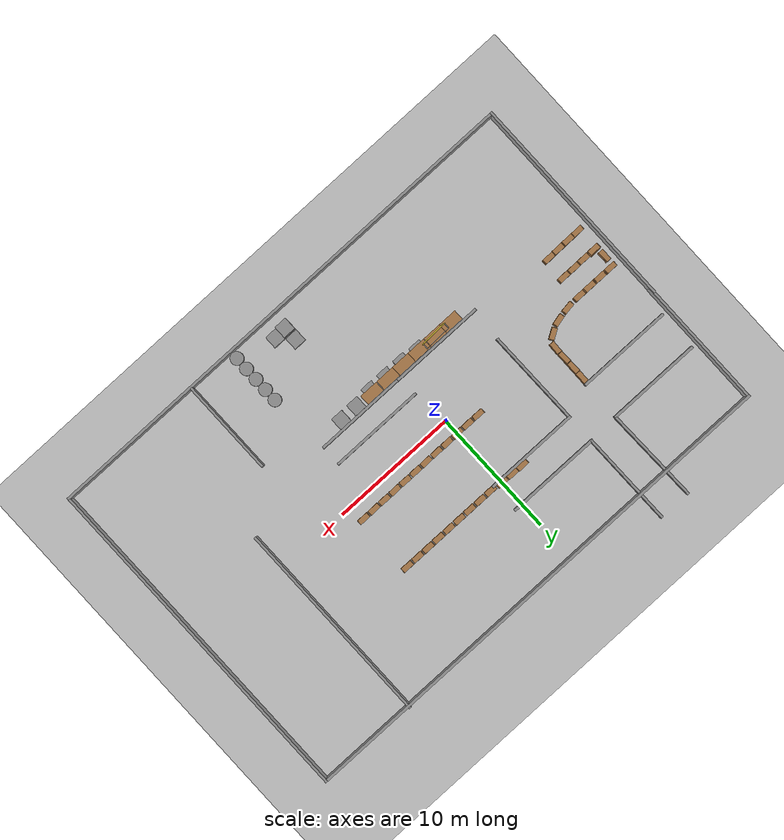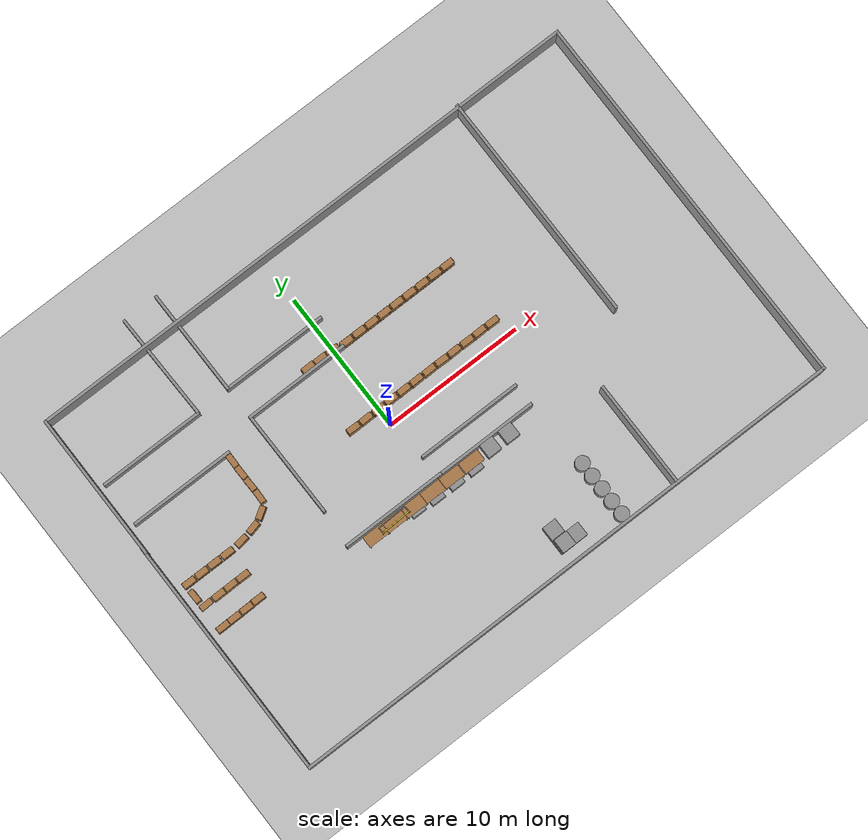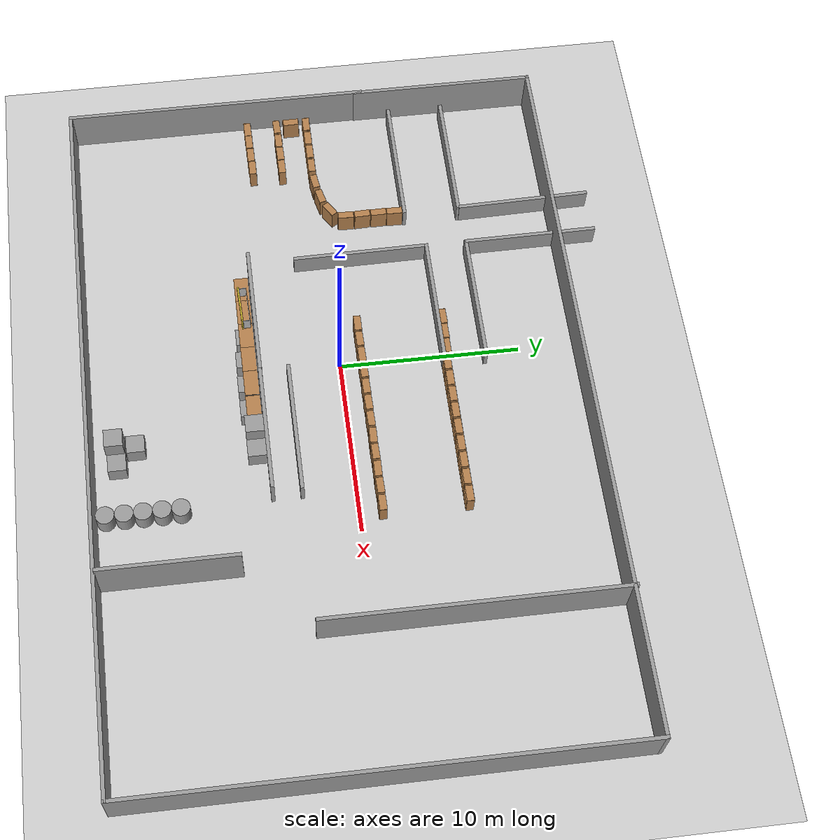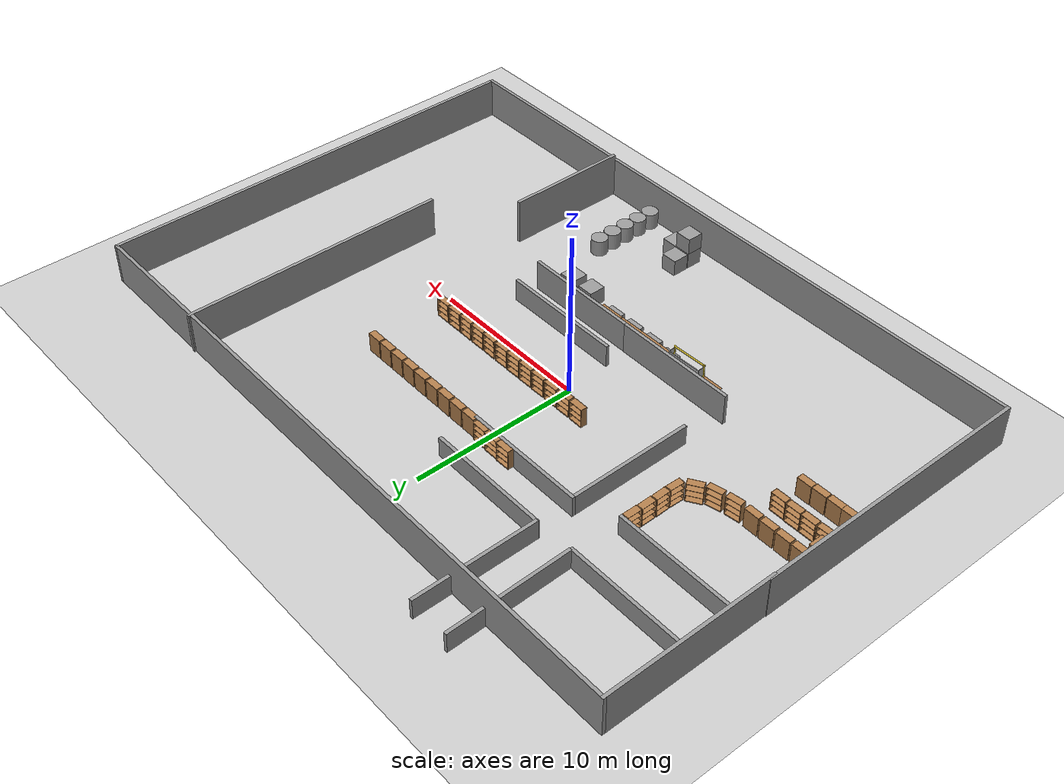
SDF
<sdf version="1.4">
 <world name="default">
  <light name="sun" type="directional">
   <pose>0 0 10 0 -0 0</pose>
   <diffuse>0.8 0.8 0.8 1</diffuse>
   <specular>0.2 0.2 0.2 1</specular>
   <attenuation>
    <range>1000</range>
    <constant>0.9</constant>
    <linear>0.01</linear>
    <quadratic>0.001</quadratic>
   </attenuation>
   <direction>-0.5 0.1 -0.9</direction>
  </light>
  <model name="ground_plane">
   <static>1</static>
   <link name="link">
    <collision name="collision">
     <geometry><plane><normal>0 0 1</normal><size>100 100</size></plane></geometry>
     <surface><friction><ode><mu>100</mu><mu2>50</mu2></ode></friction></surface>
    </collision>
    <visual name="visual">
     <cast_shadows>0</cast_shadows>
     <geometry><plane><normal>0 0 1</normal><size>100 100</size></plane></geometry>
     <material>
      <script><uri>file://media/materials/scripts/gazebo.material</uri><name>Gazebo/Grey</name></script>
     </material>
    </visual>
    <velocity_decay><linear>0</linear><angular>0</angular></velocity_decay>
   </link>
  </model>
  <physics type="ode">
   <max_step_size>0.001</max_step_size>
   <real_time_factor>1</real_time_factor>
   <real_time_update_rate>1000</real_time_update_rate>
   <gravity>0 0 -9.8</gravity>
  </physics>
  <scene><ambient>0.4 0.4 0.4 1</ambient><background>0.7 0.7 0.7 1</background><shadows>1</shadows></scene>
  <spherical_coordinates>
   <surface_model>EARTH_WGS84</surface_model>
   <latitude_deg>0</latitude_deg>
   <longitude_deg>0</longitude_deg>
   <elevation>0</elevation>
   <heading_deg>0</heading_deg>
  </spherical_coordinates>
  <model name="model">
   <link name="Wall_1">
    <collision name="Wall_1_Collision">
     <geometry><box><size>17.2537 0.2 2.5</size></box></geometry>
     <pose>0 0 1.25 0 -0 0</pose>
    </collision>
    <visual name="Wall_1_Visual">
     <pose>0 0 1.25 0 -0 0</pose>
     <geometry><box><size>17.2537 0.2 2.5</size></box></geometry>
     <material>
      <script><uri>file://media/materials/scripts/gazebo.material</uri><name>Gazebo/Grey</name></script>
     </material>
    </visual>
    <velocity_decay><linear>0</linear><angular>0</angular></velocity_decay>
    <pose>-20.2542 -5.39043 0 0 0 -1.5708</pose>
   </link>
   <link name="Wall_2">
    <collision name="Wall_2_Collision">
     <geometry><box><size>40.6619 0.2 2.5</size></box></geometry>
     <pose>0 0 1.25 0 -0 0</pose>
    </collision>
    <visual name="Wall_2_Visual">
     <pose>0 0 1.25 0 -0 0</pose>
     <geometry><box><size>40.6619 0.2 2.5</size></box></geometry>
     <material>
      <script><uri>file://media/materials/scripts/gazebo.material</uri><name>Gazebo/Grey</name></script>
     </material>
    </visual>
    <velocity_decay><linear>0</linear><angular>0</angular></velocity_decay>
    <pose>-0.02326 -13.9173 0 0 -0 0</pose>
   </link>
   <link name="Wall_3">
    <collision name="Wall_3_Collision">
     <geometry><box><size>27.2435 0.2 2.5</size></box></geometry>
     <pose>0 0 1.25 0 -0 0</pose>
    </collision>
    <visual name="Wall_3_Visual">
     <pose>0 0 1.25 0 -0 0</pose>
     <geometry><box><size>27.2435 0.2 2.5</size></box></geometry>
     <material>
      <script><uri>file://media/materials/scripts/gazebo.material</uri><name>Gazebo/Grey</name></script>
     </material>
    </visual>
    <velocity_decay><linear>0</linear><angular>0</angular></velocity_decay>
    <pose>20.2077 -0.395493 0 0 -0 1.5708</pose>
   </link>
   <link name="Wall_4">
    <collision name="Wall_4_Collision">
     <geometry><box><size>40.6249 0.2 2.5</size></box></geometry>
     <pose>0 0 1.25 0 -0 0</pose>
    </collision>
    <visual name="Wall_4_Visual">
     <pose>0 0 1.25 0 -0 0</pose>
     <geometry><box><size>40.6249 0.2 2.5</size></box></geometry>
     <material>
      <script><uri>file://media/materials/scripts/gazebo.material</uri><name>Gazebo/Grey</name></script>
     </material>
    </visual>
    <velocity_decay><linear>0</linear><angular>0</angular></velocity_decay>
    <pose>-0.004758 13.1263 0 0 -0 3.14159</pose>
   </link>
   <link name="Wall_5">
    <collision name="Wall_5_Collision">
     <geometry><box><size>10.4934 0.2 2.5</size></box></geometry>
     <pose>0 0 1.25 0 -0 0</pose>
    </collision>
    <visual name="Wall_5_Visual">
     <pose>0 0 1.25 0 -0 0</pose>
     <geometry><box><size>10.4934 0.2 2.5</size></box></geometry>
     <material>
      <script><uri>file://media/materials/scripts/gazebo.material</uri><name>Gazebo/Grey</name></script>
     </material>
    </visual>
    <velocity_decay><linear>0</linear><angular>0</angular></velocity_decay>
    <pose>-20.2172 7.97958 0 0 0 -1.5708</pose>
   </link>
   <link name="Wall_7">
    <collision name="Wall_7_Collision">
     <geometry><box><size>16.3419 0.2 2.5</size></box></geometry>
     <pose>0 0 1.25 0 -0 0</pose>
    </collision>
    <visual name="Wall_7_Visual">
     <pose>0 0 1.25 0 -0 0</pose>
     <geometry><box><size>16.3419 0.2 2.5</size></box></geometry>
     <material>
      <script><uri>file://media/materials/scripts/gazebo.material</uri><name>Gazebo/Grey</name></script>
     </material>
    </visual>
    <velocity_decay><linear>0</linear><angular>0</angular></velocity_decay>
    <pose>12.3275 5.15285 0 0 0 -1.5708</pose>
   </link>
   <static>1</static>
   <pose>3.2317 -0.01025 0 0 -0 0</pose>
  </model>
  <model name="bookshelf">
   <static>1</static>
   <link name="link">
    <inertial><mass>1</mass></inertial>
    <collision name="back">
     <pose>0 0.005 0.6 0 -0 0</pose>
     <geometry><box><size>0.9 0.01 1.2</size></box></geometry>
    </collision>
    <visual name="visual1">
     <pose>0 0.005 0.6 0 -0 0</pose>
     <geometry><box><size>0.9 0.01 1.2</size></box></geometry>
     <material>
      <script><uri>file://media/materials/scripts/gazebo.material</uri><name>Gazebo/Wood</name></script>
     </material>
    </visual>
    <collision name="left_side">
     <pose>0.45 -0.195 0.6 0 -0 0</pose>
     <geometry><box><size>0.02 0.4 1.2</size></box></geometry>
    </collision>
    <visual name="visual2">
     <pose>0.45 -0.195 0.6 0 -0 0</pose>
     <geometry><box><size>0.02 0.4 1.2</size></box></geometry>
     <material>
      <script><uri>file://media/materials/scripts/gazebo.material</uri><name>Gazebo/Wood</name></script>
     </material>
    </visual>
    <collision name="right_side">
     <pose>-0.45 -0.195 0.6 0 -0 0</pose>
     <geometry><box><size>0.02 0.4 1.2</size></box></geometry>
    </collision>
    <visual name="visual3">
     <pose>-0.45 -0.195 0.6 0 -0 0</pose>
     <geometry><box><size>0.02 0.4 1.2</size></box></geometry>
     <material>
      <script><uri>file://media/materials/scripts/gazebo.material</uri><name>Gazebo/Wood</name></script>
     </material>
    </visual>
    <collision name="bottom">
     <pose>0 -0.195 0.03 0 -0 0</pose>
     <geometry><box><size>0.88 0.4 0.06</size></box></geometry>
    </collision>
    <visual name="visual4">
     <pose>0 -0.195 0.03 0 -0 0</pose>
     <geometry><box><size>0.88 0.4 0.06</size></box></geometry>
     <material>
      <script><uri>file://media/materials/scripts/gazebo.material</uri><name>Gazebo/Wood</name></script>
     </material>
    </visual>
    <collision name="top">
     <pose>0 -0.195 1.19 0 -0 0</pose>
     <geometry><box><size>0.88 0.4 0.02</size></box></geometry>
    </collision>
    <visual name="visual5">
     <pose>0 -0.195 1.19 0 -0 0</pose>
     <geometry><box><size>0.88 0.4 0.02</size></box></geometry>
     <material>
      <script><uri>file://media/materials/scripts/gazebo.material</uri><name>Gazebo/Wood</name></script>
     </material>
    </visual>
    <collision name="low_shelf">
     <pose>0 -0.195 0.43 0 -0 0</pose>
     <geometry><box><size>0.88 0.4 0.02</size></box></geometry>
    </collision>
    <visual name="visual6">
     <pose>0 -0.195 0.43 0 -0 0</pose>
     <geometry><box><size>0.88 0.4 0.02</size></box></geometry>
     <material>
      <script><uri>file://media/materials/scripts/gazebo.material</uri><name>Gazebo/Wood</name></script>
     </material>
    </visual>
    <collision name="high_shelf">
     <pose>0 -0.195 0.8 0 -0 0</pose>
     <geometry><box><size>0.88 0.4 0.02</size></box></geometry>
    </collision>
    <visual name="visual7">
     <pose>0 -0.195 0.8 0 -0 0</pose>
     <geometry><box><size>0.88 0.4 0.02</size></box></geometry>
     <material>
      <script><uri>file://media/materials/scripts/gazebo.material</uri><name>Gazebo/Wood</name></script>
     </material>
    </visual>
    <velocity_decay><linear>0</linear><angular>0</angular></velocity_decay>
   </link>
   <pose>9 1 0 0 0 -3.13833</pose>
  </model>
  <model name="bookshelf_0">
   <static>1</static>
   <link name="link">
    <inertial><mass>1</mass></inertial>
    <collision name="back">
     <pose>0 0.005 0.6 0 -0 0</pose>
     <geometry><box><size>0.9 0.01 1.2</size></box></geometry>
    </collision>
    <visual name="visual1">
     <pose>0 0.005 0.6 0 -0 0</pose>
     <geometry><box><size>0.9 0.01 1.2</size></box></geometry>
     <material>
      <script><uri>file://media/materials/scripts/gazebo.material</uri><name>Gazebo/Wood</name></script>
     </material>
    </visual>
    <collision name="left_side">
     <pose>0.45 -0.195 0.6 0 -0 0</pose>
     <geometry><box><size>0.02 0.4 1.2</size></box></geometry>
    </collision>
    <visual name="visual2">
     <pose>0.45 -0.195 0.6 0 -0 0</pose>
     <geometry><box><size>0.02 0.4 1.2</size></box></geometry>
     <material>
      <script><uri>file://media/materials/scripts/gazebo.material</uri><name>Gazebo/Wood</name></script>
     </material>
    </visual>
    <collision name="right_side">
     <pose>-0.45 -0.195 0.6 0 -0 0</pose>
     <geometry><box><size>0.02 0.4 1.2</size></box></geometry>
    </collision>
    <visual name="visual3">
     <pose>-0.45 -0.195 0.6 0 -0 0</pose>
     <geometry><box><size>0.02 0.4 1.2</size></box></geometry>
     <material>
      <script><uri>file://media/materials/scripts/gazebo.material</uri><name>Gazebo/Wood</name></script>
     </material>
    </visual>
    <collision name="bottom">
     <pose>0 -0.195 0.03 0 -0 0</pose>
     <geometry><box><size>0.88 0.4 0.06</size></box></geometry>
    </collision>
    <visual name="visual4">
     <pose>0 -0.195 0.03 0 -0 0</pose>
     <geometry><box><size>0.88 0.4 0.06</size></box></geometry>
     <material>
      <script><uri>file://media/materials/scripts/gazebo.material</uri><name>Gazebo/Wood</name></script>
     </material>
    </visual>
    <collision name="top">
     <pose>0 -0.195 1.19 0 -0 0</pose>
     <geometry><box><size>0.88 0.4 0.02</size></box></geometry>
    </collision>
    <visual name="visual5">
     <pose>0 -0.195 1.19 0 -0 0</pose>
     <geometry><box><size>0.88 0.4 0.02</size></box></geometry>
     <material>
      <script><uri>file://media/materials/scripts/gazebo.material</uri><name>Gazebo/Wood</name></script>
     </material>
    </visual>
    <collision name="low_shelf">
     <pose>0 -0.195 0.43 0 -0 0</pose>
     <geometry><box><size>0.88 0.4 0.02</size></box></geometry>
    </collision>
    <visual name="visual6">
     <pose>0 -0.195 0.43 0 -0 0</pose>
     <geometry><box><size>0.88 0.4 0.02</size></box></geometry>
     <material>
      <script><uri>file://media/materials/scripts/gazebo.material</uri><name>Gazebo/Wood</name></script>
     </material>
    </visual>
    <collision name="high_shelf">
     <pose>0 -0.195 0.8 0 -0 0</pose>
     <geometry><box><size>0.88 0.4 0.02</size></box></geometry>
    </collision>
    <visual name="visual7">
     <pose>0 -0.195 0.8 0 -0 0</pose>
     <geometry><box><size>0.88 0.4 0.02</size></box></geometry>
     <material>
      <script><uri>file://media/materials/scripts/gazebo.material</uri><name>Gazebo/Wood</name></script>
     </material>
    </visual>
    <velocity_decay><linear>0</linear><angular>0</angular></velocity_decay>
   </link>
   <pose>8 1 0 0 0 -3.11916</pose>
  </model>
  <model name="bookshelf_1">
   <static>1</static>
   <link name="link">
    <inertial><mass>1</mass></inertial>
    <collision name="back">
     <pose>0 0.005 0.6 0 -0 0</pose>
     <geometry><box><size>0.9 0.01 1.2</size></box></geometry>
    </collision>
    <visual name="visual1">
     <pose>0 0.005 0.6 0 -0 0</pose>
     <geometry><box><size>0.9 0.01 1.2</size></box></geometry>
     <material>
      <script><uri>file://media/materials/scripts/gazebo.material</uri><name>Gazebo/Wood</name></script>
     </material>
    </visual>
    <collision name="left_side">
     <pose>0.45 -0.195 0.6 0 -0 0</pose>
     <geometry><box><size>0.02 0.4 1.2</size></box></geometry>
    </collision>
    <visual name="visual2">
     <pose>0.45 -0.195 0.6 0 -0 0</pose>
     <geometry><box><size>0.02 0.4 1.2</size></box></geometry>
     <material>
      <script><uri>file://media/materials/scripts/gazebo.material</uri><name>Gazebo/Wood</name></script>
     </material>
    </visual>
    <collision name="right_side">
     <pose>-0.45 -0.195 0.6 0 -0 0</pose>
     <geometry><box><size>0.02 0.4 1.2</size></box></geometry>
    </collision>
    <visual name="visual3">
     <pose>-0.45 -0.195 0.6 0 -0 0</pose>
     <geometry><box><size>0.02 0.4 1.2</size></box></geometry>
     <material>
      <script><uri>file://media/materials/scripts/gazebo.material</uri><name>Gazebo/Wood</name></script>
     </material>
    </visual>
    <collision name="bottom">
     <pose>0 -0.195 0.03 0 -0 0</pose>
     <geometry><box><size>0.88 0.4 0.06</size></box></geometry>
    </collision>
    <visual name="visual4">
     <pose>0 -0.195 0.03 0 -0 0</pose>
     <geometry><box><size>0.88 0.4 0.06</size></box></geometry>
     <material>
      <script><uri>file://media/materials/scripts/gazebo.material</uri><name>Gazebo/Wood</name></script>
     </material>
    </visual>
    <collision name="top">
     <pose>0 -0.195 1.19 0 -0 0</pose>
     <geometry><box><size>0.88 0.4 0.02</size></box></geometry>
    </collision>
    <visual name="visual5">
     <pose>0 -0.195 1.19 0 -0 0</pose>
     <geometry><box><size>0.88 0.4 0.02</size></box></geometry>
     <material>
      <script><uri>file://media/materials/scripts/gazebo.material</uri><name>Gazebo/Wood</name></script>
     </material>
    </visual>
    <collision name="low_shelf">
     <pose>0 -0.195 0.43 0 -0 0</pose>
     <geometry><box><size>0.88 0.4 0.02</size></box></geometry>
    </collision>
    <visual name="visual6">
     <pose>0 -0.195 0.43 0 -0 0</pose>
     <geometry><box><size>0.88 0.4 0.02</size></box></geometry>
     <material>
      <script><uri>file://media/materials/scripts/gazebo.material</uri><name>Gazebo/Wood</name></script>
     </material>
    </visual>
    <collision name="high_shelf">
     <pose>0 -0.195 0.8 0 -0 0</pose>
     <geometry><box><size>0.88 0.4 0.02</size></box></geometry>
    </collision>
    <visual name="visual7">
     <pose>0 -0.195 0.8 0 -0 0</pose>
     <geometry><box><size>0.88 0.4 0.02</size></box></geometry>
     <material>
      <script><uri>file://media/materials/scripts/gazebo.material</uri><name>Gazebo/Wood</name></script>
     </material>
    </visual>
    <velocity_decay><linear>0</linear><angular>0</angular></velocity_decay>
   </link>
   <pose>7 1 0 0 -0 3.12738</pose>
  </model>
  <model name="bookshelf_2">
   <static>1</static>
   <link name="link">
    <inertial><mass>1</mass></inertial>
    <collision name="back">
     <pose>0 0.005 0.6 0 -0 0</pose>
     <geometry><box><size>0.9 0.01 1.2</size></box></geometry>
    </collision>
    <visual name="visual1">
     <pose>0 0.005 0.6 0 -0 0</pose>
     <geometry><box><size>0.9 0.01 1.2</size></box></geometry>
     <material>
      <script><uri>file://media/materials/scripts/gazebo.material</uri><name>Gazebo/Wood</name></script>
     </material>
    </visual>
    <collision name="left_side">
     <pose>0.45 -0.195 0.6 0 -0 0</pose>
     <geometry><box><size>0.02 0.4 1.2</size></box></geometry>
    </collision>
    <visual name="visual2">
     <pose>0.45 -0.195 0.6 0 -0 0</pose>
     <geometry><box><size>0.02 0.4 1.2</size></box></geometry>
     <material>
      <script><uri>file://media/materials/scripts/gazebo.material</uri><name>Gazebo/Wood</name></script>
     </material>
    </visual>
    <collision name="right_side">
     <pose>-0.45 -0.195 0.6 0 -0 0</pose>
     <geometry><box><size>0.02 0.4 1.2</size></box></geometry>
    </collision>
    <visual name="visual3">
     <pose>-0.45 -0.195 0.6 0 -0 0</pose>
     <geometry><box><size>0.02 0.4 1.2</size></box></geometry>
     <material>
      <script><uri>file://media/materials/scripts/gazebo.material</uri><name>Gazebo/Wood</name></script>
     </material>
    </visual>
    <collision name="bottom">
     <pose>0 -0.195 0.03 0 -0 0</pose>
     <geometry><box><size>0.88 0.4 0.06</size></box></geometry>
    </collision>
    <visual name="visual4">
     <pose>0 -0.195 0.03 0 -0 0</pose>
     <geometry><box><size>0.88 0.4 0.06</size></box></geometry>
     <material>
      <script><uri>file://media/materials/scripts/gazebo.material</uri><name>Gazebo/Wood</name></script>
     </material>
    </visual>
    <collision name="top">
     <pose>0 -0.195 1.19 0 -0 0</pose>
     <geometry><box><size>0.88 0.4 0.02</size></box></geometry>
    </collision>
    <visual name="visual5">
     <pose>0 -0.195 1.19 0 -0 0</pose>
     <geometry><box><size>0.88 0.4 0.02</size></box></geometry>
     <material>
      <script><uri>file://media/materials/scripts/gazebo.material</uri><name>Gazebo/Wood</name></script>
     </material>
    </visual>
    <collision name="low_shelf">
     <pose>0 -0.195 0.43 0 -0 0</pose>
     <geometry><box><size>0.88 0.4 0.02</size></box></geometry>
    </collision>
    <visual name="visual6">
     <pose>0 -0.195 0.43 0 -0 0</pose>
     <geometry><box><size>0.88 0.4 0.02</size></box></geometry>
     <material>
      <script><uri>file://media/materials/scripts/gazebo.material</uri><name>Gazebo/Wood</name></script>
     </material>
    </visual>
    <collision name="high_shelf">
     <pose>0 -0.195 0.8 0 -0 0</pose>
     <geometry><box><size>0.88 0.4 0.02</size></box></geometry>
    </collision>
    <visual name="visual7">
     <pose>0 -0.195 0.8 0 -0 0</pose>
     <geometry><box><size>0.88 0.4 0.02</size></box></geometry>
     <material>
      <script><uri>file://media/materials/scripts/gazebo.material</uri><name>Gazebo/Wood</name></script>
     </material>
    </visual>
    <velocity_decay><linear>0</linear><angular>0</angular></velocity_decay>
   </link>
   <pose>6 1 0 0 0 -3.12478</pose>
  </model>
  <model name="bookshelf_3">
   <static>1</static>
   <link name="link">
    <inertial><mass>1</mass></inertial>
    <collision name="back">
     <pose>0 0.005 0.6 0 -0 0</pose>
     <geometry><box><size>0.9 0.01 1.2</size></box></geometry>
    </collision>
    <visual name="visual1">
     <pose>0 0.005 0.6 0 -0 0</pose>
     <geometry><box><size>0.9 0.01 1.2</size></box></geometry>
     <material>
      <script><uri>file://media/materials/scripts/gazebo.material</uri><name>Gazebo/Wood</name></script>
     </material>
    </visual>
    <collision name="left_side">
     <pose>0.45 -0.195 0.6 0 -0 0</pose>
     <geometry><box><size>0.02 0.4 1.2</size></box></geometry>
    </collision>
    <visual name="visual2">
     <pose>0.45 -0.195 0.6 0 -0 0</pose>
     <geometry><box><size>0.02 0.4 1.2</size></box></geometry>
     <material>
      <script><uri>file://media/materials/scripts/gazebo.material</uri><name>Gazebo/Wood</name></script>
     </material>
    </visual>
    <collision name="right_side">
     <pose>-0.45 -0.195 0.6 0 -0 0</pose>
     <geometry><box><size>0.02 0.4 1.2</size></box></geometry>
    </collision>
    <visual name="visual3">
     <pose>-0.45 -0.195 0.6 0 -0 0</pose>
     <geometry><box><size>0.02 0.4 1.2</size></box></geometry>
     <material>
      <script><uri>file://media/materials/scripts/gazebo.material</uri><name>Gazebo/Wood</name></script>
     </material>
    </visual>
    <collision name="bottom">
     <pose>0 -0.195 0.03 0 -0 0</pose>
     <geometry><box><size>0.88 0.4 0.06</size></box></geometry>
    </collision>
    <visual name="visual4">
     <pose>0 -0.195 0.03 0 -0 0</pose>
     <geometry><box><size>0.88 0.4 0.06</size></box></geometry>
     <material>
      <script><uri>file://media/materials/scripts/gazebo.material</uri><name>Gazebo/Wood</name></script>
     </material>
    </visual>
    <collision name="top">
     <pose>0 -0.195 1.19 0 -0 0</pose>
     <geometry><box><size>0.88 0.4 0.02</size></box></geometry>
    </collision>
    <visual name="visual5">
     <pose>0 -0.195 1.19 0 -0 0</pose>
     <geometry><box><size>0.88 0.4 0.02</size></box></geometry>
     <material>
      <script><uri>file://media/materials/scripts/gazebo.material</uri><name>Gazebo/Wood</name></script>
     </material>
    </visual>
    <collision name="low_shelf">
     <pose>0 -0.195 0.43 0 -0 0</pose>
     <geometry><box><size>0.88 0.4 0.02</size></box></geometry>
    </collision>
    <visual name="visual6">
     <pose>0 -0.195 0.43 0 -0 0</pose>
     <geometry><box><size>0.88 0.4 0.02</size></box></geometry>
     <material>
      <script><uri>file://media/materials/scripts/gazebo.material</uri><name>Gazebo/Wood</name></script>
     </material>
    </visual>
    <collision name="high_shelf">
     <pose>0 -0.195 0.8 0 -0 0</pose>
     <geometry><box><size>0.88 0.4 0.02</size></box></geometry>
    </collision>
    <visual name="visual7">
     <pose>0 -0.195 0.8 0 -0 0</pose>
     <geometry><box><size>0.88 0.4 0.02</size></box></geometry>
     <material>
      <script><uri>file://media/materials/scripts/gazebo.material</uri><name>Gazebo/Wood</name></script>
     </material>
    </visual>
    <velocity_decay><linear>0</linear><angular>0</angular></velocity_decay>
   </link>
   <pose>5 1 0 0 -0 3.11866</pose>
  </model>
  <model name="bookshelf_4">
   <static>1</static>
   <link name="link">
    <inertial><mass>1</mass></inertial>
    <collision name="back">
     <pose>0 0.005 0.6 0 -0 0</pose>
     <geometry><box><size>0.9 0.01 1.2</size></box></geometry>
    </collision>
    <visual name="visual1">
     <pose>0 0.005 0.6 0 -0 0</pose>
     <geometry><box><size>0.9 0.01 1.2</size></box></geometry>
     <material>
      <script><uri>file://media/materials/scripts/gazebo.material</uri><name>Gazebo/Wood</name></script>
     </material>
    </visual>
    <collision name="left_side">
     <pose>0.45 -0.195 0.6 0 -0 0</pose>
     <geometry><box><size>0.02 0.4 1.2</size></box></geometry>
    </collision>
    <visual name="visual2">
     <pose>0.45 -0.195 0.6 0 -0 0</pose>
     <geometry><box><size>0.02 0.4 1.2</size></box></geometry>
     <material>
      <script><uri>file://media/materials/scripts/gazebo.material</uri><name>Gazebo/Wood</name></script>
     </material>
    </visual>
    <collision name="right_side">
     <pose>-0.45 -0.195 0.6 0 -0 0</pose>
     <geometry><box><size>0.02 0.4 1.2</size></box></geometry>
    </collision>
    <visual name="visual3">
     <pose>-0.45 -0.195 0.6 0 -0 0</pose>
     <geometry><box><size>0.02 0.4 1.2</size></box></geometry>
     <material>
      <script><uri>file://media/materials/scripts/gazebo.material</uri><name>Gazebo/Wood</name></script>
     </material>
    </visual>
    <collision name="bottom">
     <pose>0 -0.195 0.03 0 -0 0</pose>
     <geometry><box><size>0.88 0.4 0.06</size></box></geometry>
    </collision>
    <visual name="visual4">
     <pose>0 -0.195 0.03 0 -0 0</pose>
     <geometry><box><size>0.88 0.4 0.06</size></box></geometry>
     <material>
      <script><uri>file://media/materials/scripts/gazebo.material</uri><name>Gazebo/Wood</name></script>
     </material>
    </visual>
    <collision name="top">
     <pose>0 -0.195 1.19 0 -0 0</pose>
     <geometry><box><size>0.88 0.4 0.02</size></box></geometry>
    </collision>
    <visual name="visual5">
     <pose>0 -0.195 1.19 0 -0 0</pose>
     <geometry><box><size>0.88 0.4 0.02</size></box></geometry>
     <material>
      <script><uri>file://media/materials/scripts/gazebo.material</uri><name>Gazebo/Wood</name></script>
     </material>
    </visual>
    <collision name="low_shelf">
     <pose>0 -0.195 0.43 0 -0 0</pose>
     <geometry><box><size>0.88 0.4 0.02</size></box></geometry>
    </collision>
    <visual name="visual6">
     <pose>0 -0.195 0.43 0 -0 0</pose>
     <geometry><box><size>0.88 0.4 0.02</size></box></geometry>
     <material>
      <script><uri>file://media/materials/scripts/gazebo.material</uri><name>Gazebo/Wood</name></script>
     </material>
    </visual>
    <collision name="high_shelf">
     <pose>0 -0.195 0.8 0 -0 0</pose>
     <geometry><box><size>0.88 0.4 0.02</size></box></geometry>
    </collision>
    <visual name="visual7">
     <pose>0 -0.195 0.8 0 -0 0</pose>
     <geometry><box><size>0.88 0.4 0.02</size></box></geometry>
     <material>
      <script><uri>file://media/materials/scripts/gazebo.material</uri><name>Gazebo/Wood</name></script>
     </material>
    </visual>
    <velocity_decay><linear>0</linear><angular>0</angular></velocity_decay>
   </link>
   <pose>4 1 0 0 0 -3.1202</pose>
  </model>
  <model name="bookshelf_5">
   <static>1</static>
   <link name="link">
    <inertial><mass>1</mass></inertial>
    <collision name="back">
     <pose>0 0.005 0.6 0 -0 0</pose>
     <geometry><box><size>0.9 0.01 1.2</size></box></geometry>
    </collision>
    <visual name="visual1">
     <pose>0 0.005 0.6 0 -0 0</pose>
     <geometry><box><size>0.9 0.01 1.2</size></box></geometry>
     <material>
      <script><uri>file://media/materials/scripts/gazebo.material</uri><name>Gazebo/Wood</name></script>
     </material>
    </visual>
    <collision name="left_side">
     <pose>0.45 -0.195 0.6 0 -0 0</pose>
     <geometry><box><size>0.02 0.4 1.2</size></box></geometry>
    </collision>
    <visual name="visual2">
     <pose>0.45 -0.195 0.6 0 -0 0</pose>
     <geometry><box><size>0.02 0.4 1.2</size></box></geometry>
     <material>
      <script><uri>file://media/materials/scripts/gazebo.material</uri><name>Gazebo/Wood</name></script>
     </material>
    </visual>
    <collision name="right_side">
     <pose>-0.45 -0.195 0.6 0 -0 0</pose>
     <geometry><box><size>0.02 0.4 1.2</size></box></geometry>
    </collision>
    <visual name="visual3">
     <pose>-0.45 -0.195 0.6 0 -0 0</pose>
     <geometry><box><size>0.02 0.4 1.2</size></box></geometry>
     <material>
      <script><uri>file://media/materials/scripts/gazebo.material</uri><name>Gazebo/Wood</name></script>
     </material>
    </visual>
    <collision name="bottom">
     <pose>0 -0.195 0.03 0 -0 0</pose>
     <geometry><box><size>0.88 0.4 0.06</size></box></geometry>
    </collision>
    <visual name="visual4">
     <pose>0 -0.195 0.03 0 -0 0</pose>
     <geometry><box><size>0.88 0.4 0.06</size></box></geometry>
     <material>
      <script><uri>file://media/materials/scripts/gazebo.material</uri><name>Gazebo/Wood</name></script>
     </material>
    </visual>
    <collision name="top">
     <pose>0 -0.195 1.19 0 -0 0</pose>
     <geometry><box><size>0.88 0.4 0.02</size></box></geometry>
    </collision>
    <visual name="visual5">
     <pose>0 -0.195 1.19 0 -0 0</pose>
     <geometry><box><size>0.88 0.4 0.02</size></box></geometry>
     <material>
      <script><uri>file://media/materials/scripts/gazebo.material</uri><name>Gazebo/Wood</name></script>
     </material>
    </visual>
    <collision name="low_shelf">
     <pose>0 -0.195 0.43 0 -0 0</pose>
     <geometry><box><size>0.88 0.4 0.02</size></box></geometry>
    </collision>
    <visual name="visual6">
     <pose>0 -0.195 0.43 0 -0 0</pose>
     <geometry><box><size>0.88 0.4 0.02</size></box></geometry>
     <material>
      <script><uri>file://media/materials/scripts/gazebo.material</uri><name>Gazebo/Wood</name></script>
     </material>
    </visual>
    <collision name="high_shelf">
     <pose>0 -0.195 0.8 0 -0 0</pose>
     <geometry><box><size>0.88 0.4 0.02</size></box></geometry>
    </collision>
    <visual name="visual7">
     <pose>0 -0.195 0.8 0 -0 0</pose>
     <geometry><box><size>0.88 0.4 0.02</size></box></geometry>
     <material>
      <script><uri>file://media/materials/scripts/gazebo.material</uri><name>Gazebo/Wood</name></script>
     </material>
    </visual>
    <velocity_decay><linear>0</linear><angular>0</angular></velocity_decay>
   </link>
   <pose>3 1 0 0 0 -3.11535</pose>
  </model>
  <model name="bookshelf_6">
   <static>1</static>
   <link name="link">
    <inertial><mass>1</mass></inertial>
    <collision name="back">
     <pose>0 0.005 0.6 0 -0 0</pose>
     <geometry><box><size>0.9 0.01 1.2</size></box></geometry>
    </collision>
    <visual name="visual1">
     <pose>0 0.005 0.6 0 -0 0</pose>
     <geometry><box><size>0.9 0.01 1.2</size></box></geometry>
     <material>
      <script><uri>file://media/materials/scripts/gazebo.material</uri><name>Gazebo/Wood</name></script>
     </material>
    </visual>
    <collision name="left_side">
     <pose>0.45 -0.195 0.6 0 -0 0</pose>
     <geometry><box><size>0.02 0.4 1.2</size></box></geometry>
    </collision>
    <visual name="visual2">
     <pose>0.45 -0.195 0.6 0 -0 0</pose>
     <geometry><box><size>0.02 0.4 1.2</size></box></geometry>
     <material>
      <script><uri>file://media/materials/scripts/gazebo.material</uri><name>Gazebo/Wood</name></script>
     </material>
    </visual>
    <collision name="right_side">
     <pose>-0.45 -0.195 0.6 0 -0 0</pose>
     <geometry><box><size>0.02 0.4 1.2</size></box></geometry>
    </collision>
    <visual name="visual3">
     <pose>-0.45 -0.195 0.6 0 -0 0</pose>
     <geometry><box><size>0.02 0.4 1.2</size></box></geometry>
     <material>
      <script><uri>file://media/materials/scripts/gazebo.material</uri><name>Gazebo/Wood</name></script>
     </material>
    </visual>
    <collision name="bottom">
     <pose>0 -0.195 0.03 0 -0 0</pose>
     <geometry><box><size>0.88 0.4 0.06</size></box></geometry>
    </collision>
    <visual name="visual4">
     <pose>0 -0.195 0.03 0 -0 0</pose>
     <geometry><box><size>0.88 0.4 0.06</size></box></geometry>
     <material>
      <script><uri>file://media/materials/scripts/gazebo.material</uri><name>Gazebo/Wood</name></script>
     </material>
    </visual>
    <collision name="top">
     <pose>0 -0.195 1.19 0 -0 0</pose>
     <geometry><box><size>0.88 0.4 0.02</size></box></geometry>
    </collision>
    <visual name="visual5">
     <pose>0 -0.195 1.19 0 -0 0</pose>
     <geometry><box><size>0.88 0.4 0.02</size></box></geometry>
     <material>
      <script><uri>file://media/materials/scripts/gazebo.material</uri><name>Gazebo/Wood</name></script>
     </material>
    </visual>
    <collision name="low_shelf">
     <pose>0 -0.195 0.43 0 -0 0</pose>
     <geometry><box><size>0.88 0.4 0.02</size></box></geometry>
    </collision>
    <visual name="visual6">
     <pose>0 -0.195 0.43 0 -0 0</pose>
     <geometry><box><size>0.88 0.4 0.02</size></box></geometry>
     <material>
      <script><uri>file://media/materials/scripts/gazebo.material</uri><name>Gazebo/Wood</name></script>
     </material>
    </visual>
    <collision name="high_shelf">
     <pose>0 -0.195 0.8 0 -0 0</pose>
     <geometry><box><size>0.88 0.4 0.02</size></box></geometry>
    </collision>
    <visual name="visual7">
     <pose>0 -0.195 0.8 0 -0 0</pose>
     <geometry><box><size>0.88 0.4 0.02</size></box></geometry>
     <material>
      <script><uri>file://media/materials/scripts/gazebo.material</uri><name>Gazebo/Wood</name></script>
     </material>
    </visual>
    <velocity_decay><linear>0</linear><angular>0</angular></velocity_decay>
   </link>
   <pose>2 1 0 0 0 -3.1207</pose>
  </model>
  <model name="bookshelf_7">
   <static>1</static>
   <link name="link">
    <inertial><mass>1</mass></inertial>
    <collision name="back">
     <pose>0 0.005 0.6 0 -0 0</pose>
     <geometry><box><size>0.9 0.01 1.2</size></box></geometry>
    </collision>
    <visual name="visual1">
     <pose>0 0.005 0.6 0 -0 0</pose>
     <geometry><box><size>0.9 0.01 1.2</size></box></geometry>
     <material>
      <script><uri>file://media/materials/scripts/gazebo.material</uri><name>Gazebo/Wood</name></script>
     </material>
    </visual>
    <collision name="left_side">
     <pose>0.45 -0.195 0.6 0 -0 0</pose>
     <geometry><box><size>0.02 0.4 1.2</size></box></geometry>
    </collision>
    <visual name="visual2">
     <pose>0.45 -0.195 0.6 0 -0 0</pose>
     <geometry><box><size>0.02 0.4 1.2</size></box></geometry>
     <material>
      <script><uri>file://media/materials/scripts/gazebo.material</uri><name>Gazebo/Wood</name></script>
     </material>
    </visual>
    <collision name="right_side">
     <pose>-0.45 -0.195 0.6 0 -0 0</pose>
     <geometry><box><size>0.02 0.4 1.2</size></box></geometry>
    </collision>
    <visual name="visual3">
     <pose>-0.45 -0.195 0.6 0 -0 0</pose>
     <geometry><box><size>0.02 0.4 1.2</size></box></geometry>
     <material>
      <script><uri>file://media/materials/scripts/gazebo.material</uri><name>Gazebo/Wood</name></script>
     </material>
    </visual>
    <collision name="bottom">
     <pose>0 -0.195 0.03 0 -0 0</pose>
     <geometry><box><size>0.88 0.4 0.06</size></box></geometry>
    </collision>
    <visual name="visual4">
     <pose>0 -0.195 0.03 0 -0 0</pose>
     <geometry><box><size>0.88 0.4 0.06</size></box></geometry>
     <material>
      <script><uri>file://media/materials/scripts/gazebo.material</uri><name>Gazebo/Wood</name></script>
     </material>
    </visual>
    <collision name="top">
     <pose>0 -0.195 1.19 0 -0 0</pose>
     <geometry><box><size>0.88 0.4 0.02</size></box></geometry>
    </collision>
    <visual name="visual5">
     <pose>0 -0.195 1.19 0 -0 0</pose>
     <geometry><box><size>0.88 0.4 0.02</size></box></geometry>
     <material>
      <script><uri>file://media/materials/scripts/gazebo.material</uri><name>Gazebo/Wood</name></script>
     </material>
    </visual>
    <collision name="low_shelf">
     <pose>0 -0.195 0.43 0 -0 0</pose>
     <geometry><box><size>0.88 0.4 0.02</size></box></geometry>
    </collision>
    <visual name="visual6">
     <pose>0 -0.195 0.43 0 -0 0</pose>
     <geometry><box><size>0.88 0.4 0.02</size></box></geometry>
     <material>
      <script><uri>file://media/materials/scripts/gazebo.material</uri><name>Gazebo/Wood</name></script>
     </material>
    </visual>
    <collision name="high_shelf">
     <pose>0 -0.195 0.8 0 -0 0</pose>
     <geometry><box><size>0.88 0.4 0.02</size></box></geometry>
    </collision>
    <visual name="visual7">
     <pose>0 -0.195 0.8 0 -0 0</pose>
     <geometry><box><size>0.88 0.4 0.02</size></box></geometry>
     <material>
      <script><uri>file://media/materials/scripts/gazebo.material</uri><name>Gazebo/Wood</name></script>
     </material>
    </visual>
    <velocity_decay><linear>0</linear><angular>0</angular></velocity_decay>
   </link>
   <pose>1 1 0 0 0 -3.11494</pose>
  </model>
  <model name="bookshelf_8">
   <static>1</static>
   <link name="link">
    <inertial><mass>1</mass></inertial>
    <collision name="back">
     <pose>0 0.005 0.6 0 -0 0</pose>
     <geometry><box><size>0.9 0.01 1.2</size></box></geometry>
    </collision>
    <visual name="visual1">
     <pose>0 0.005 0.6 0 -0 0</pose>
     <geometry><box><size>0.9 0.01 1.2</size></box></geometry>
     <material>
      <script><uri>file://media/materials/scripts/gazebo.material</uri><name>Gazebo/Wood</name></script>
     </material>
    </visual>
    <collision name="left_side">
     <pose>0.45 -0.195 0.6 0 -0 0</pose>
     <geometry><box><size>0.02 0.4 1.2</size></box></geometry>
    </collision>
    <visual name="visual2">
     <pose>0.45 -0.195 0.6 0 -0 0</pose>
     <geometry><box><size>0.02 0.4 1.2</size></box></geometry>
     <material>
      <script><uri>file://media/materials/scripts/gazebo.material</uri><name>Gazebo/Wood</name></script>
     </material>
    </visual>
    <collision name="right_side">
     <pose>-0.45 -0.195 0.6 0 -0 0</pose>
     <geometry><box><size>0.02 0.4 1.2</size></box></geometry>
    </collision>
    <visual name="visual3">
     <pose>-0.45 -0.195 0.6 0 -0 0</pose>
     <geometry><box><size>0.02 0.4 1.2</size></box></geometry>
     <material>
      <script><uri>file://media/materials/scripts/gazebo.material</uri><name>Gazebo/Wood</name></script>
     </material>
    </visual>
    <collision name="bottom">
     <pose>0 -0.195 0.03 0 -0 0</pose>
     <geometry><box><size>0.88 0.4 0.06</size></box></geometry>
    </collision>
    <visual name="visual4">
     <pose>0 -0.195 0.03 0 -0 0</pose>
     <geometry><box><size>0.88 0.4 0.06</size></box></geometry>
     <material>
      <script><uri>file://media/materials/scripts/gazebo.material</uri><name>Gazebo/Wood</name></script>
     </material>
    </visual>
    <collision name="top">
     <pose>0 -0.195 1.19 0 -0 0</pose>
     <geometry><box><size>0.88 0.4 0.02</size></box></geometry>
    </collision>
    <visual name="visual5">
     <pose>0 -0.195 1.19 0 -0 0</pose>
     <geometry><box><size>0.88 0.4 0.02</size></box></geometry>
     <material>
      <script><uri>file://media/materials/scripts/gazebo.material</uri><name>Gazebo/Wood</name></script>
     </material>
    </visual>
    <collision name="low_shelf">
     <pose>0 -0.195 0.43 0 -0 0</pose>
     <geometry><box><size>0.88 0.4 0.02</size></box></geometry>
    </collision>
    <visual name="visual6">
     <pose>0 -0.195 0.43 0 -0 0</pose>
     <geometry><box><size>0.88 0.4 0.02</size></box></geometry>
     <material>
      <script><uri>file://media/materials/scripts/gazebo.material</uri><name>Gazebo/Wood</name></script>
     </material>
    </visual>
    <collision name="high_shelf">
     <pose>0 -0.195 0.8 0 -0 0</pose>
     <geometry><box><size>0.88 0.4 0.02</size></box></geometry>
    </collision>
    <visual name="visual7">
     <pose>0 -0.195 0.8 0 -0 0</pose>
     <geometry><box><size>0.88 0.4 0.02</size></box></geometry>
     <material>
      <script><uri>file://media/materials/scripts/gazebo.material</uri><name>Gazebo/Wood</name></script>
     </material>
    </visual>
    <velocity_decay><linear>0</linear><angular>0</angular></velocity_decay>
   </link>
   <pose>0 1 0 0 0 -3.12369</pose>
  </model>
  <model name="bookshelf_9">
   <static>1</static>
   <link name="link">
    <inertial><mass>1</mass></inertial>
    <collision name="back">
     <pose>0 0.005 0.6 0 -0 0</pose>
     <geometry><box><size>0.9 0.01 1.2</size></box></geometry>
    </collision>
    <visual name="visual1">
     <pose>0 0.005 0.6 0 -0 0</pose>
     <geometry><box><size>0.9 0.01 1.2</size></box></geometry>
     <material>
      <script><uri>file://media/materials/scripts/gazebo.material</uri><name>Gazebo/Wood</name></script>
     </material>
    </visual>
    <collision name="left_side">
     <pose>0.45 -0.195 0.6 0 -0 0</pose>
     <geometry><box><size>0.02 0.4 1.2</size></box></geometry>
    </collision>
    <visual name="visual2">
     <pose>0.45 -0.195 0.6 0 -0 0</pose>
     <geometry><box><size>0.02 0.4 1.2</size></box></geometry>
     <material>
      <script><uri>file://media/materials/scripts/gazebo.material</uri><name>Gazebo/Wood</name></script>
     </material>
    </visual>
    <collision name="right_side">
     <pose>-0.45 -0.195 0.6 0 -0 0</pose>
     <geometry><box><size>0.02 0.4 1.2</size></box></geometry>
    </collision>
    <visual name="visual3">
     <pose>-0.45 -0.195 0.6 0 -0 0</pose>
     <geometry><box><size>0.02 0.4 1.2</size></box></geometry>
     <material>
      <script><uri>file://media/materials/scripts/gazebo.material</uri><name>Gazebo/Wood</name></script>
     </material>
    </visual>
    <collision name="bottom">
     <pose>0 -0.195 0.03 0 -0 0</pose>
     <geometry><box><size>0.88 0.4 0.06</size></box></geometry>
    </collision>
    <visual name="visual4">
     <pose>0 -0.195 0.03 0 -0 0</pose>
     <geometry><box><size>0.88 0.4 0.06</size></box></geometry>
     <material>
      <script><uri>file://media/materials/scripts/gazebo.material</uri><name>Gazebo/Wood</name></script>
     </material>
    </visual>
    <collision name="top">
     <pose>0 -0.195 1.19 0 -0 0</pose>
     <geometry><box><size>0.88 0.4 0.02</size></box></geometry>
    </collision>
    <visual name="visual5">
     <pose>0 -0.195 1.19 0 -0 0</pose>
     <geometry><box><size>0.88 0.4 0.02</size></box></geometry>
     <material>
      <script><uri>file://media/materials/scripts/gazebo.material</uri><name>Gazebo/Wood</name></script>
     </material>
    </visual>
    <collision name="low_shelf">
     <pose>0 -0.195 0.43 0 -0 0</pose>
     <geometry><box><size>0.88 0.4 0.02</size></box></geometry>
    </collision>
    <visual name="visual6">
     <pose>0 -0.195 0.43 0 -0 0</pose>
     <geometry><box><size>0.88 0.4 0.02</size></box></geometry>
     <material>
      <script><uri>file://media/materials/scripts/gazebo.material</uri><name>Gazebo/Wood</name></script>
     </material>
    </visual>
    <collision name="high_shelf">
     <pose>0 -0.195 0.8 0 -0 0</pose>
     <geometry><box><size>0.88 0.4 0.02</size></box></geometry>
    </collision>
    <visual name="visual7">
     <pose>0 -0.195 0.8 0 -0 0</pose>
     <geometry><box><size>0.88 0.4 0.02</size></box></geometry>
     <material>
      <script><uri>file://media/materials/scripts/gazebo.material</uri><name>Gazebo/Wood</name></script>
     </material>
    </visual>
    <velocity_decay><linear>0</linear><angular>0</angular></velocity_decay>
   </link>
   <pose>-1 1 0 0 0 -3.12411</pose>
  </model>
  <model name="bookshelf_10">
   <static>1</static>
   <link name="link">
    <inertial><mass>1</mass></inertial>
    <collision name="back">
     <pose>0 0.005 0.6 0 -0 0</pose>
     <geometry><box><size>0.9 0.01 1.2</size></box></geometry>
    </collision>
    <visual name="visual1">
     <pose>0 0.005 0.6 0 -0 0</pose>
     <geometry><box><size>0.9 0.01 1.2</size></box></geometry>
     <material>
      <script><uri>file://media/materials/scripts/gazebo.material</uri><name>Gazebo/Wood</name></script>
     </material>
    </visual>
    <collision name="left_side">
     <pose>0.45 -0.195 0.6 0 -0 0</pose>
     <geometry><box><size>0.02 0.4 1.2</size></box></geometry>
    </collision>
    <visual name="visual2">
     <pose>0.45 -0.195 0.6 0 -0 0</pose>
     <geometry><box><size>0.02 0.4 1.2</size></box></geometry>
     <material>
      <script><uri>file://media/materials/scripts/gazebo.material</uri><name>Gazebo/Wood</name></script>
     </material>
    </visual>
    <collision name="right_side">
     <pose>-0.45 -0.195 0.6 0 -0 0</pose>
     <geometry><box><size>0.02 0.4 1.2</size></box></geometry>
    </collision>
    <visual name="visual3">
     <pose>-0.45 -0.195 0.6 0 -0 0</pose>
     <geometry><box><size>0.02 0.4 1.2</size></box></geometry>
     <material>
      <script><uri>file://media/materials/scripts/gazebo.material</uri><name>Gazebo/Wood</name></script>
     </material>
    </visual>
    <collision name="bottom">
     <pose>0 -0.195 0.03 0 -0 0</pose>
     <geometry><box><size>0.88 0.4 0.06</size></box></geometry>
    </collision>
    <visual name="visual4">
     <pose>0 -0.195 0.03 0 -0 0</pose>
     <geometry><box><size>0.88 0.4 0.06</size></box></geometry>
     <material>
      <script><uri>file://media/materials/scripts/gazebo.material</uri><name>Gazebo/Wood</name></script>
     </material>
    </visual>
    <collision name="top">
     <pose>0 -0.195 1.19 0 -0 0</pose>
     <geometry><box><size>0.88 0.4 0.02</size></box></geometry>
    </collision>
    <visual name="visual5">
     <pose>0 -0.195 1.19 0 -0 0</pose>
     <geometry><box><size>0.88 0.4 0.02</size></box></geometry>
     <material>
      <script><uri>file://media/materials/scripts/gazebo.material</uri><name>Gazebo/Wood</name></script>
     </material>
    </visual>
    <collision name="low_shelf">
     <pose>0 -0.195 0.43 0 -0 0</pose>
     <geometry><box><size>0.88 0.4 0.02</size></box></geometry>
    </collision>
    <visual name="visual6">
     <pose>0 -0.195 0.43 0 -0 0</pose>
     <geometry><box><size>0.88 0.4 0.02</size></box></geometry>
     <material>
      <script><uri>file://media/materials/scripts/gazebo.material</uri><name>Gazebo/Wood</name></script>
     </material>
    </visual>
    <collision name="high_shelf">
     <pose>0 -0.195 0.8 0 -0 0</pose>
     <geometry><box><size>0.88 0.4 0.02</size></box></geometry>
    </collision>
    <visual name="visual7">
     <pose>0 -0.195 0.8 0 -0 0</pose>
     <geometry><box><size>0.88 0.4 0.02</size></box></geometry>
     <material>
      <script><uri>file://media/materials/scripts/gazebo.material</uri><name>Gazebo/Wood</name></script>
     </material>
    </visual>
    <velocity_decay><linear>0</linear><angular>0</angular></velocity_decay>
   </link>
   <pose>-2 1 0 0 -0 3.12895</pose>
  </model>
  <model name="bookshelf_11">
   <static>1</static>
   <link name="link">
    <inertial><mass>1</mass></inertial>
    <collision name="back">
     <pose>0 0.005 0.6 0 -0 0</pose>
     <geometry><box><size>0.9 0.01 1.2</size></box></geometry>
    </collision>
    <visual name="visual1">
     <pose>0 0.005 0.6 0 -0 0</pose>
     <geometry><box><size>0.9 0.01 1.2</size></box></geometry>
     <material>
      <script><uri>file://media/materials/scripts/gazebo.material</uri><name>Gazebo/Wood</name></script>
     </material>
    </visual>
    <collision name="left_side">
     <pose>0.45 -0.195 0.6 0 -0 0</pose>
     <geometry><box><size>0.02 0.4 1.2</size></box></geometry>
    </collision>
    <visual name="visual2">
     <pose>0.45 -0.195 0.6 0 -0 0</pose>
     <geometry><box><size>0.02 0.4 1.2</size></box></geometry>
     <material>
      <script><uri>file://media/materials/scripts/gazebo.material</uri><name>Gazebo/Wood</name></script>
     </material>
    </visual>
    <collision name="right_side">
     <pose>-0.45 -0.195 0.6 0 -0 0</pose>
     <geometry><box><size>0.02 0.4 1.2</size></box></geometry>
    </collision>
    <visual name="visual3">
     <pose>-0.45 -0.195 0.6 0 -0 0</pose>
     <geometry><box><size>0.02 0.4 1.2</size></box></geometry>
     <material>
      <script><uri>file://media/materials/scripts/gazebo.material</uri><name>Gazebo/Wood</name></script>
     </material>
    </visual>
    <collision name="bottom">
     <pose>0 -0.195 0.03 0 -0 0</pose>
     <geometry><box><size>0.88 0.4 0.06</size></box></geometry>
    </collision>
    <visual name="visual4">
     <pose>0 -0.195 0.03 0 -0 0</pose>
     <geometry><box><size>0.88 0.4 0.06</size></box></geometry>
     <material>
      <script><uri>file://media/materials/scripts/gazebo.material</uri><name>Gazebo/Wood</name></script>
     </material>
    </visual>
    <collision name="top">
     <pose>0 -0.195 1.19 0 -0 0</pose>
     <geometry><box><size>0.88 0.4 0.02</size></box></geometry>
    </collision>
    <visual name="visual5">
     <pose>0 -0.195 1.19 0 -0 0</pose>
     <geometry><box><size>0.88 0.4 0.02</size></box></geometry>
     <material>
      <script><uri>file://media/materials/scripts/gazebo.material</uri><name>Gazebo/Wood</name></script>
     </material>
    </visual>
    <collision name="low_shelf">
     <pose>0 -0.195 0.43 0 -0 0</pose>
     <geometry><box><size>0.88 0.4 0.02</size></box></geometry>
    </collision>
    <visual name="visual6">
     <pose>0 -0.195 0.43 0 -0 0</pose>
     <geometry><box><size>0.88 0.4 0.02</size></box></geometry>
     <material>
      <script><uri>file://media/materials/scripts/gazebo.material</uri><name>Gazebo/Wood</name></script>
     </material>
    </visual>
    <collision name="high_shelf">
     <pose>0 -0.195 0.8 0 -0 0</pose>
     <geometry><box><size>0.88 0.4 0.02</size></box></geometry>
    </collision>
    <visual name="visual7">
     <pose>0 -0.195 0.8 0 -0 0</pose>
     <geometry><box><size>0.88 0.4 0.02</size></box></geometry>
     <material>
      <script><uri>file://media/materials/scripts/gazebo.material</uri><name>Gazebo/Wood</name></script>
     </material>
    </visual>
    <velocity_decay><linear>0</linear><angular>0</angular></velocity_decay>
   </link>
   <pose>9 6 0 0 -0 0</pose>
  </model>
  <model name="bookshelf_12">
   <static>1</static>
   <link name="link">
    <inertial><mass>1</mass></inertial>
    <collision name="back">
     <pose>0 0.005 0.6 0 -0 0</pose>
     <geometry><box><size>0.9 0.01 1.2</size></box></geometry>
    </collision>
    <visual name="visual1">
     <pose>0 0.005 0.6 0 -0 0</pose>
     <geometry><box><size>0.9 0.01 1.2</size></box></geometry>
     <material>
      <script><uri>file://media/materials/scripts/gazebo.material</uri><name>Gazebo/Wood</name></script>
     </material>
    </visual>
    <collision name="left_side">
     <pose>0.45 -0.195 0.6 0 -0 0</pose>
     <geometry><box><size>0.02 0.4 1.2</size></box></geometry>
    </collision>
    <visual name="visual2">
     <pose>0.45 -0.195 0.6 0 -0 0</pose>
     <geometry><box><size>0.02 0.4 1.2</size></box></geometry>
     <material>
      <script><uri>file://media/materials/scripts/gazebo.material</uri><name>Gazebo/Wood</name></script>
     </material>
    </visual>
    <collision name="right_side">
     <pose>-0.45 -0.195 0.6 0 -0 0</pose>
     <geometry><box><size>0.02 0.4 1.2</size></box></geometry>
    </collision>
    <visual name="visual3">
     <pose>-0.45 -0.195 0.6 0 -0 0</pose>
     <geometry><box><size>0.02 0.4 1.2</size></box></geometry>
     <material>
      <script><uri>file://media/materials/scripts/gazebo.material</uri><name>Gazebo/Wood</name></script>
     </material>
    </visual>
    <collision name="bottom">
     <pose>0 -0.195 0.03 0 -0 0</pose>
     <geometry><box><size>0.88 0.4 0.06</size></box></geometry>
    </collision>
    <visual name="visual4">
     <pose>0 -0.195 0.03 0 -0 0</pose>
     <geometry><box><size>0.88 0.4 0.06</size></box></geometry>
     <material>
      <script><uri>file://media/materials/scripts/gazebo.material</uri><name>Gazebo/Wood</name></script>
     </material>
    </visual>
    <collision name="top">
     <pose>0 -0.195 1.19 0 -0 0</pose>
     <geometry><box><size>0.88 0.4 0.02</size></box></geometry>
    </collision>
    <visual name="visual5">
     <pose>0 -0.195 1.19 0 -0 0</pose>
     <geometry><box><size>0.88 0.4 0.02</size></box></geometry>
     <material>
      <script><uri>file://media/materials/scripts/gazebo.material</uri><name>Gazebo/Wood</name></script>
     </material>
    </visual>
    <collision name="low_shelf">
     <pose>0 -0.195 0.43 0 -0 0</pose>
     <geometry><box><size>0.88 0.4 0.02</size></box></geometry>
    </collision>
    <visual name="visual6">
     <pose>0 -0.195 0.43 0 -0 0</pose>
     <geometry><box><size>0.88 0.4 0.02</size></box></geometry>
     <material>
      <script><uri>file://media/materials/scripts/gazebo.material</uri><name>Gazebo/Wood</name></script>
     </material>
    </visual>
    <collision name="high_shelf">
     <pose>0 -0.195 0.8 0 -0 0</pose>
     <geometry><box><size>0.88 0.4 0.02</size></box></geometry>
    </collision>
    <visual name="visual7">
     <pose>0 -0.195 0.8 0 -0 0</pose>
     <geometry><box><size>0.88 0.4 0.02</size></box></geometry>
     <material>
      <script><uri>file://media/materials/scripts/gazebo.material</uri><name>Gazebo/Wood</name></script>
     </material>
    </visual>
    <velocity_decay><linear>0</linear><angular>0</angular></velocity_decay>
   </link>
   <pose>8 6 0 0 -0 0</pose>
  </model>
  <model name="bookshelf_13">
   <static>1</static>
   <link name="link">
    <inertial><mass>1</mass></inertial>
    <collision name="back">
     <pose>0 0.005 0.6 0 -0 0</pose>
     <geometry><box><size>0.9 0.01 1.2</size></box></geometry>
    </collision>
    <visual name="visual1">
     <pose>0 0.005 0.6 0 -0 0</pose>
     <geometry><box><size>0.9 0.01 1.2</size></box></geometry>
     <material>
      <script><uri>file://media/materials/scripts/gazebo.material</uri><name>Gazebo/Wood</name></script>
     </material>
    </visual>
    <collision name="left_side">
     <pose>0.45 -0.195 0.6 0 -0 0</pose>
     <geometry><box><size>0.02 0.4 1.2</size></box></geometry>
    </collision>
    <visual name="visual2">
     <pose>0.45 -0.195 0.6 0 -0 0</pose>
     <geometry><box><size>0.02 0.4 1.2</size></box></geometry>
     <material>
      <script><uri>file://media/materials/scripts/gazebo.material</uri><name>Gazebo/Wood</name></script>
     </material>
    </visual>
    <collision name="right_side">
     <pose>-0.45 -0.195 0.6 0 -0 0</pose>
     <geometry><box><size>0.02 0.4 1.2</size></box></geometry>
    </collision>
    <visual name="visual3">
     <pose>-0.45 -0.195 0.6 0 -0 0</pose>
     <geometry><box><size>0.02 0.4 1.2</size></box></geometry>
     <material>
      <script><uri>file://media/materials/scripts/gazebo.material</uri><name>Gazebo/Wood</name></script>
     </material>
    </visual>
    <collision name="bottom">
     <pose>0 -0.195 0.03 0 -0 0</pose>
     <geometry><box><size>0.88 0.4 0.06</size></box></geometry>
    </collision>
    <visual name="visual4">
     <pose>0 -0.195 0.03 0 -0 0</pose>
     <geometry><box><size>0.88 0.4 0.06</size></box></geometry>
     <material>
      <script><uri>file://media/materials/scripts/gazebo.material</uri><name>Gazebo/Wood</name></script>
     </material>
    </visual>
    <collision name="top">
     <pose>0 -0.195 1.19 0 -0 0</pose>
     <geometry><box><size>0.88 0.4 0.02</size></box></geometry>
    </collision>
    <visual name="visual5">
     <pose>0 -0.195 1.19 0 -0 0</pose>
     <geometry><box><size>0.88 0.4 0.02</size></box></geometry>
     <material>
      <script><uri>file://media/materials/scripts/gazebo.material</uri><name>Gazebo/Wood</name></script>
     </material>
    </visual>
    <collision name="low_shelf">
     <pose>0 -0.195 0.43 0 -0 0</pose>
     <geometry><box><size>0.88 0.4 0.02</size></box></geometry>
    </collision>
    <visual name="visual6">
     <pose>0 -0.195 0.43 0 -0 0</pose>
     <geometry><box><size>0.88 0.4 0.02</size></box></geometry>
     <material>
      <script><uri>file://media/materials/scripts/gazebo.material</uri><name>Gazebo/Wood</name></script>
     </material>
    </visual>
    <collision name="high_shelf">
     <pose>0 -0.195 0.8 0 -0 0</pose>
     <geometry><box><size>0.88 0.4 0.02</size></box></geometry>
    </collision>
    <visual name="visual7">
     <pose>0 -0.195 0.8 0 -0 0</pose>
     <geometry><box><size>0.88 0.4 0.02</size></box></geometry>
     <material>
      <script><uri>file://media/materials/scripts/gazebo.material</uri><name>Gazebo/Wood</name></script>
     </material>
    </visual>
    <velocity_decay><linear>0</linear><angular>0</angular></velocity_decay>
   </link>
   <pose>7 6 0 0 -0 0</pose>
  </model>
  <model name="bookshelf_14">
   <static>1</static>
   <link name="link">
    <inertial><mass>1</mass></inertial>
    <collision name="back">
     <pose>0 0.005 0.6 0 -0 0</pose>
     <geometry><box><size>0.9 0.01 1.2</size></box></geometry>
    </collision>
    <visual name="visual1">
     <pose>0 0.005 0.6 0 -0 0</pose>
     <geometry><box><size>0.9 0.01 1.2</size></box></geometry>
     <material>
      <script><uri>file://media/materials/scripts/gazebo.material</uri><name>Gazebo/Wood</name></script>
     </material>
    </visual>
    <collision name="left_side">
     <pose>0.45 -0.195 0.6 0 -0 0</pose>
     <geometry><box><size>0.02 0.4 1.2</size></box></geometry>
    </collision>
    <visual name="visual2">
     <pose>0.45 -0.195 0.6 0 -0 0</pose>
     <geometry><box><size>0.02 0.4 1.2</size></box></geometry>
     <material>
      <script><uri>file://media/materials/scripts/gazebo.material</uri><name>Gazebo/Wood</name></script>
     </material>
    </visual>
    <collision name="right_side">
     <pose>-0.45 -0.195 0.6 0 -0 0</pose>
     <geometry><box><size>0.02 0.4 1.2</size></box></geometry>
    </collision>
    <visual name="visual3">
     <pose>-0.45 -0.195 0.6 0 -0 0</pose>
     <geometry><box><size>0.02 0.4 1.2</size></box></geometry>
     <material>
      <script><uri>file://media/materials/scripts/gazebo.material</uri><name>Gazebo/Wood</name></script>
     </material>
    </visual>
    <collision name="bottom">
     <pose>0 -0.195 0.03 0 -0 0</pose>
     <geometry><box><size>0.88 0.4 0.06</size></box></geometry>
    </collision>
    <visual name="visual4">
     <pose>0 -0.195 0.03 0 -0 0</pose>
     <geometry><box><size>0.88 0.4 0.06</size></box></geometry>
     <material>
      <script><uri>file://media/materials/scripts/gazebo.material</uri><name>Gazebo/Wood</name></script>
     </material>
    </visual>
    <collision name="top">
     <pose>0 -0.195 1.19 0 -0 0</pose>
     <geometry><box><size>0.88 0.4 0.02</size></box></geometry>
    </collision>
    <visual name="visual5">
     <pose>0 -0.195 1.19 0 -0 0</pose>
     <geometry><box><size>0.88 0.4 0.02</size></box></geometry>
     <material>
      <script><uri>file://media/materials/scripts/gazebo.material</uri><name>Gazebo/Wood</name></script>
     </material>
    </visual>
    <collision name="low_shelf">
     <pose>0 -0.195 0.43 0 -0 0</pose>
     <geometry><box><size>0.88 0.4 0.02</size></box></geometry>
    </collision>
    <visual name="visual6">
     <pose>0 -0.195 0.43 0 -0 0</pose>
     <geometry><box><size>0.88 0.4 0.02</size></box></geometry>
     <material>
      <script><uri>file://media/materials/scripts/gazebo.material</uri><name>Gazebo/Wood</name></script>
     </material>
    </visual>
    <collision name="high_shelf">
     <pose>0 -0.195 0.8 0 -0 0</pose>
     <geometry><box><size>0.88 0.4 0.02</size></box></geometry>
    </collision>
    <visual name="visual7">
     <pose>0 -0.195 0.8 0 -0 0</pose>
     <geometry><box><size>0.88 0.4 0.02</size></box></geometry>
     <material>
      <script><uri>file://media/materials/scripts/gazebo.material</uri><name>Gazebo/Wood</name></script>
     </material>
    </visual>
    <velocity_decay><linear>0</linear><angular>0</angular></velocity_decay>
   </link>
   <pose>6 6 0 0 -0 0</pose>
  </model>
  <model name="bookshelf_15">
   <static>1</static>
   <link name="link">
    <inertial><mass>1</mass></inertial>
    <collision name="back">
     <pose>0 0.005 0.6 0 -0 0</pose>
     <geometry><box><size>0.9 0.01 1.2</size></box></geometry>
    </collision>
    <visual name="visual1">
     <pose>0 0.005 0.6 0 -0 0</pose>
     <geometry><box><size>0.9 0.01 1.2</size></box></geometry>
     <material>
      <script><uri>file://media/materials/scripts/gazebo.material</uri><name>Gazebo/Wood</name></script>
     </material>
    </visual>
    <collision name="left_side">
     <pose>0.45 -0.195 0.6 0 -0 0</pose>
     <geometry><box><size>0.02 0.4 1.2</size></box></geometry>
    </collision>
    <visual name="visual2">
     <pose>0.45 -0.195 0.6 0 -0 0</pose>
     <geometry><box><size>0.02 0.4 1.2</size></box></geometry>
     <material>
      <script><uri>file://media/materials/scripts/gazebo.material</uri><name>Gazebo/Wood</name></script>
     </material>
    </visual>
    <collision name="right_side">
     <pose>-0.45 -0.195 0.6 0 -0 0</pose>
     <geometry><box><size>0.02 0.4 1.2</size></box></geometry>
    </collision>
    <visual name="visual3">
     <pose>-0.45 -0.195 0.6 0 -0 0</pose>
     <geometry><box><size>0.02 0.4 1.2</size></box></geometry>
     <material>
      <script><uri>file://media/materials/scripts/gazebo.material</uri><name>Gazebo/Wood</name></script>
     </material>
    </visual>
    <collision name="bottom">
     <pose>0 -0.195 0.03 0 -0 0</pose>
     <geometry><box><size>0.88 0.4 0.06</size></box></geometry>
    </collision>
    <visual name="visual4">
     <pose>0 -0.195 0.03 0 -0 0</pose>
     <geometry><box><size>0.88 0.4 0.06</size></box></geometry>
     <material>
      <script><uri>file://media/materials/scripts/gazebo.material</uri><name>Gazebo/Wood</name></script>
     </material>
    </visual>
    <collision name="top">
     <pose>0 -0.195 1.19 0 -0 0</pose>
     <geometry><box><size>0.88 0.4 0.02</size></box></geometry>
    </collision>
    <visual name="visual5">
     <pose>0 -0.195 1.19 0 -0 0</pose>
     <geometry><box><size>0.88 0.4 0.02</size></box></geometry>
     <material>
      <script><uri>file://media/materials/scripts/gazebo.material</uri><name>Gazebo/Wood</name></script>
     </material>
    </visual>
    <collision name="low_shelf">
     <pose>0 -0.195 0.43 0 -0 0</pose>
     <geometry><box><size>0.88 0.4 0.02</size></box></geometry>
    </collision>
    <visual name="visual6">
     <pose>0 -0.195 0.43 0 -0 0</pose>
     <geometry><box><size>0.88 0.4 0.02</size></box></geometry>
     <material>
      <script><uri>file://media/materials/scripts/gazebo.material</uri><name>Gazebo/Wood</name></script>
     </material>
    </visual>
    <collision name="high_shelf">
     <pose>0 -0.195 0.8 0 -0 0</pose>
     <geometry><box><size>0.88 0.4 0.02</size></box></geometry>
    </collision>
    <visual name="visual7">
     <pose>0 -0.195 0.8 0 -0 0</pose>
     <geometry><box><size>0.88 0.4 0.02</size></box></geometry>
     <material>
      <script><uri>file://media/materials/scripts/gazebo.material</uri><name>Gazebo/Wood</name></script>
     </material>
    </visual>
    <velocity_decay><linear>0</linear><angular>0</angular></velocity_decay>
   </link>
   <pose>5 6 0 0 -0 0</pose>
  </model>
  <model name="bookshelf_16">
   <static>1</static>
   <link name="link">
    <inertial><mass>1</mass></inertial>
    <collision name="back">
     <pose>0 0.005 0.6 0 -0 0</pose>
     <geometry><box><size>0.9 0.01 1.2</size></box></geometry>
    </collision>
    <visual name="visual1">
     <pose>0 0.005 0.6 0 -0 0</pose>
     <geometry><box><size>0.9 0.01 1.2</size></box></geometry>
     <material>
      <script><uri>file://media/materials/scripts/gazebo.material</uri><name>Gazebo/Wood</name></script>
     </material>
    </visual>
    <collision name="left_side">
     <pose>0.45 -0.195 0.6 0 -0 0</pose>
     <geometry><box><size>0.02 0.4 1.2</size></box></geometry>
    </collision>
    <visual name="visual2">
     <pose>0.45 -0.195 0.6 0 -0 0</pose>
     <geometry><box><size>0.02 0.4 1.2</size></box></geometry>
     <material>
      <script><uri>file://media/materials/scripts/gazebo.material</uri><name>Gazebo/Wood</name></script>
     </material>
    </visual>
    <collision name="right_side">
     <pose>-0.45 -0.195 0.6 0 -0 0</pose>
     <geometry><box><size>0.02 0.4 1.2</size></box></geometry>
    </collision>
    <visual name="visual3">
     <pose>-0.45 -0.195 0.6 0 -0 0</pose>
     <geometry><box><size>0.02 0.4 1.2</size></box></geometry>
     <material>
      <script><uri>file://media/materials/scripts/gazebo.material</uri><name>Gazebo/Wood</name></script>
     </material>
    </visual>
    <collision name="bottom">
     <pose>0 -0.195 0.03 0 -0 0</pose>
     <geometry><box><size>0.88 0.4 0.06</size></box></geometry>
    </collision>
    <visual name="visual4">
     <pose>0 -0.195 0.03 0 -0 0</pose>
     <geometry><box><size>0.88 0.4 0.06</size></box></geometry>
     <material>
      <script><uri>file://media/materials/scripts/gazebo.material</uri><name>Gazebo/Wood</name></script>
     </material>
    </visual>
    <collision name="top">
     <pose>0 -0.195 1.19 0 -0 0</pose>
     <geometry><box><size>0.88 0.4 0.02</size></box></geometry>
    </collision>
    <visual name="visual5">
     <pose>0 -0.195 1.19 0 -0 0</pose>
     <geometry><box><size>0.88 0.4 0.02</size></box></geometry>
     <material>
      <script><uri>file://media/materials/scripts/gazebo.material</uri><name>Gazebo/Wood</name></script>
     </material>
    </visual>
    <collision name="low_shelf">
     <pose>0 -0.195 0.43 0 -0 0</pose>
     <geometry><box><size>0.88 0.4 0.02</size></box></geometry>
    </collision>
    <visual name="visual6">
     <pose>0 -0.195 0.43 0 -0 0</pose>
     <geometry><box><size>0.88 0.4 0.02</size></box></geometry>
     <material>
      <script><uri>file://media/materials/scripts/gazebo.material</uri><name>Gazebo/Wood</name></script>
     </material>
    </visual>
    <collision name="high_shelf">
     <pose>0 -0.195 0.8 0 -0 0</pose>
     <geometry><box><size>0.88 0.4 0.02</size></box></geometry>
    </collision>
    <visual name="visual7">
     <pose>0 -0.195 0.8 0 -0 0</pose>
     <geometry><box><size>0.88 0.4 0.02</size></box></geometry>
     <material>
      <script><uri>file://media/materials/scripts/gazebo.material</uri><name>Gazebo/Wood</name></script>
     </material>
    </visual>
    <velocity_decay><linear>0</linear><angular>0</angular></velocity_decay>
   </link>
   <pose>4 6 0 0 -0 0</pose>
  </model>
  <model name="bookshelf_17">
   <static>1</static>
   <link name="link">
    <inertial><mass>1</mass></inertial>
    <collision name="back">
     <pose>0 0.005 0.6 0 -0 0</pose>
     <geometry><box><size>0.9 0.01 1.2</size></box></geometry>
    </collision>
    <visual name="visual1">
     <pose>0 0.005 0.6 0 -0 0</pose>
     <geometry><box><size>0.9 0.01 1.2</size></box></geometry>
     <material>
      <script><uri>file://media/materials/scripts/gazebo.material</uri><name>Gazebo/Wood</name></script>
     </material>
    </visual>
    <collision name="left_side">
     <pose>0.45 -0.195 0.6 0 -0 0</pose>
     <geometry><box><size>0.02 0.4 1.2</size></box></geometry>
    </collision>
    <visual name="visual2">
     <pose>0.45 -0.195 0.6 0 -0 0</pose>
     <geometry><box><size>0.02 0.4 1.2</size></box></geometry>
     <material>
      <script><uri>file://media/materials/scripts/gazebo.material</uri><name>Gazebo/Wood</name></script>
     </material>
    </visual>
    <collision name="right_side">
     <pose>-0.45 -0.195 0.6 0 -0 0</pose>
     <geometry><box><size>0.02 0.4 1.2</size></box></geometry>
    </collision>
    <visual name="visual3">
     <pose>-0.45 -0.195 0.6 0 -0 0</pose>
     <geometry><box><size>0.02 0.4 1.2</size></box></geometry>
     <material>
      <script><uri>file://media/materials/scripts/gazebo.material</uri><name>Gazebo/Wood</name></script>
     </material>
    </visual>
    <collision name="bottom">
     <pose>0 -0.195 0.03 0 -0 0</pose>
     <geometry><box><size>0.88 0.4 0.06</size></box></geometry>
    </collision>
    <visual name="visual4">
     <pose>0 -0.195 0.03 0 -0 0</pose>
     <geometry><box><size>0.88 0.4 0.06</size></box></geometry>
     <material>
      <script><uri>file://media/materials/scripts/gazebo.material</uri><name>Gazebo/Wood</name></script>
     </material>
    </visual>
    <collision name="top">
     <pose>0 -0.195 1.19 0 -0 0</pose>
     <geometry><box><size>0.88 0.4 0.02</size></box></geometry>
    </collision>
    <visual name="visual5">
     <pose>0 -0.195 1.19 0 -0 0</pose>
     <geometry><box><size>0.88 0.4 0.02</size></box></geometry>
     <material>
      <script><uri>file://media/materials/scripts/gazebo.material</uri><name>Gazebo/Wood</name></script>
     </material>
    </visual>
    <collision name="low_shelf">
     <pose>0 -0.195 0.43 0 -0 0</pose>
     <geometry><box><size>0.88 0.4 0.02</size></box></geometry>
    </collision>
    <visual name="visual6">
     <pose>0 -0.195 0.43 0 -0 0</pose>
     <geometry><box><size>0.88 0.4 0.02</size></box></geometry>
     <material>
      <script><uri>file://media/materials/scripts/gazebo.material</uri><name>Gazebo/Wood</name></script>
     </material>
    </visual>
    <collision name="high_shelf">
     <pose>0 -0.195 0.8 0 -0 0</pose>
     <geometry><box><size>0.88 0.4 0.02</size></box></geometry>
    </collision>
    <visual name="visual7">
     <pose>0 -0.195 0.8 0 -0 0</pose>
     <geometry><box><size>0.88 0.4 0.02</size></box></geometry>
     <material>
      <script><uri>file://media/materials/scripts/gazebo.material</uri><name>Gazebo/Wood</name></script>
     </material>
    </visual>
    <velocity_decay><linear>0</linear><angular>0</angular></velocity_decay>
   </link>
   <pose>3 6 0 0 -0 0</pose>
  </model>
  <model name="bookshelf_18">
   <static>1</static>
   <link name="link">
    <inertial><mass>1</mass></inertial>
    <collision name="back">
     <pose>0 0.005 0.6 0 -0 0</pose>
     <geometry><box><size>0.9 0.01 1.2</size></box></geometry>
    </collision>
    <visual name="visual1">
     <pose>0 0.005 0.6 0 -0 0</pose>
     <geometry><box><size>0.9 0.01 1.2</size></box></geometry>
     <material>
      <script><uri>file://media/materials/scripts/gazebo.material</uri><name>Gazebo/Wood</name></script>
     </material>
    </visual>
    <collision name="left_side">
     <pose>0.45 -0.195 0.6 0 -0 0</pose>
     <geometry><box><size>0.02 0.4 1.2</size></box></geometry>
    </collision>
    <visual name="visual2">
     <pose>0.45 -0.195 0.6 0 -0 0</pose>
     <geometry><box><size>0.02 0.4 1.2</size></box></geometry>
     <material>
      <script><uri>file://media/materials/scripts/gazebo.material</uri><name>Gazebo/Wood</name></script>
     </material>
    </visual>
    <collision name="right_side">
     <pose>-0.45 -0.195 0.6 0 -0 0</pose>
     <geometry><box><size>0.02 0.4 1.2</size></box></geometry>
    </collision>
    <visual name="visual3">
     <pose>-0.45 -0.195 0.6 0 -0 0</pose>
     <geometry><box><size>0.02 0.4 1.2</size></box></geometry>
     <material>
      <script><uri>file://media/materials/scripts/gazebo.material</uri><name>Gazebo/Wood</name></script>
     </material>
    </visual>
    <collision name="bottom">
     <pose>0 -0.195 0.03 0 -0 0</pose>
     <geometry><box><size>0.88 0.4 0.06</size></box></geometry>
    </collision>
    <visual name="visual4">
     <pose>0 -0.195 0.03 0 -0 0</pose>
     <geometry><box><size>0.88 0.4 0.06</size></box></geometry>
     <material>
      <script><uri>file://media/materials/scripts/gazebo.material</uri><name>Gazebo/Wood</name></script>
     </material>
    </visual>
    <collision name="top">
     <pose>0 -0.195 1.19 0 -0 0</pose>
     <geometry><box><size>0.88 0.4 0.02</size></box></geometry>
    </collision>
    <visual name="visual5">
     <pose>0 -0.195 1.19 0 -0 0</pose>
     <geometry><box><size>0.88 0.4 0.02</size></box></geometry>
     <material>
      <script><uri>file://media/materials/scripts/gazebo.material</uri><name>Gazebo/Wood</name></script>
     </material>
    </visual>
    <collision name="low_shelf">
     <pose>0 -0.195 0.43 0 -0 0</pose>
     <geometry><box><size>0.88 0.4 0.02</size></box></geometry>
    </collision>
    <visual name="visual6">
     <pose>0 -0.195 0.43 0 -0 0</pose>
     <geometry><box><size>0.88 0.4 0.02</size></box></geometry>
     <material>
      <script><uri>file://media/materials/scripts/gazebo.material</uri><name>Gazebo/Wood</name></script>
     </material>
    </visual>
    <collision name="high_shelf">
     <pose>0 -0.195 0.8 0 -0 0</pose>
     <geometry><box><size>0.88 0.4 0.02</size></box></geometry>
    </collision>
    <visual name="visual7">
     <pose>0 -0.195 0.8 0 -0 0</pose>
     <geometry><box><size>0.88 0.4 0.02</size></box></geometry>
     <material>
      <script><uri>file://media/materials/scripts/gazebo.material</uri><name>Gazebo/Wood</name></script>
     </material>
    </visual>
    <velocity_decay><linear>0</linear><angular>0</angular></velocity_decay>
   </link>
   <pose>2 6 0 0 -0 0</pose>
  </model>
  <model name="bookshelf_19">
   <static>1</static>
   <link name="link">
    <inertial><mass>1</mass></inertial>
    <collision name="back">
     <pose>0 0.005 0.6 0 -0 0</pose>
     <geometry><box><size>0.9 0.01 1.2</size></box></geometry>
    </collision>
    <visual name="visual1">
     <pose>0 0.005 0.6 0 -0 0</pose>
     <geometry><box><size>0.9 0.01 1.2</size></box></geometry>
     <material>
      <script><uri>file://media/materials/scripts/gazebo.material</uri><name>Gazebo/Wood</name></script>
     </material>
    </visual>
    <collision name="left_side">
     <pose>0.45 -0.195 0.6 0 -0 0</pose>
     <geometry><box><size>0.02 0.4 1.2</size></box></geometry>
    </collision>
    <visual name="visual2">
     <pose>0.45 -0.195 0.6 0 -0 0</pose>
     <geometry><box><size>0.02 0.4 1.2</size></box></geometry>
     <material>
      <script><uri>file://media/materials/scripts/gazebo.material</uri><name>Gazebo/Wood</name></script>
     </material>
    </visual>
    <collision name="right_side">
     <pose>-0.45 -0.195 0.6 0 -0 0</pose>
     <geometry><box><size>0.02 0.4 1.2</size></box></geometry>
    </collision>
    <visual name="visual3">
     <pose>-0.45 -0.195 0.6 0 -0 0</pose>
     <geometry><box><size>0.02 0.4 1.2</size></box></geometry>
     <material>
      <script><uri>file://media/materials/scripts/gazebo.material</uri><name>Gazebo/Wood</name></script>
     </material>
    </visual>
    <collision name="bottom">
     <pose>0 -0.195 0.03 0 -0 0</pose>
     <geometry><box><size>0.88 0.4 0.06</size></box></geometry>
    </collision>
    <visual name="visual4">
     <pose>0 -0.195 0.03 0 -0 0</pose>
     <geometry><box><size>0.88 0.4 0.06</size></box></geometry>
     <material>
      <script><uri>file://media/materials/scripts/gazebo.material</uri><name>Gazebo/Wood</name></script>
     </material>
    </visual>
    <collision name="top">
     <pose>0 -0.195 1.19 0 -0 0</pose>
     <geometry><box><size>0.88 0.4 0.02</size></box></geometry>
    </collision>
    <visual name="visual5">
     <pose>0 -0.195 1.19 0 -0 0</pose>
     <geometry><box><size>0.88 0.4 0.02</size></box></geometry>
     <material>
      <script><uri>file://media/materials/scripts/gazebo.material</uri><name>Gazebo/Wood</name></script>
     </material>
    </visual>
    <collision name="low_shelf">
     <pose>0 -0.195 0.43 0 -0 0</pose>
     <geometry><box><size>0.88 0.4 0.02</size></box></geometry>
    </collision>
    <visual name="visual6">
     <pose>0 -0.195 0.43 0 -0 0</pose>
     <geometry><box><size>0.88 0.4 0.02</size></box></geometry>
     <material>
      <script><uri>file://media/materials/scripts/gazebo.material</uri><name>Gazebo/Wood</name></script>
     </material>
    </visual>
    <collision name="high_shelf">
     <pose>0 -0.195 0.8 0 -0 0</pose>
     <geometry><box><size>0.88 0.4 0.02</size></box></geometry>
    </collision>
    <visual name="visual7">
     <pose>0 -0.195 0.8 0 -0 0</pose>
     <geometry><box><size>0.88 0.4 0.02</size></box></geometry>
     <material>
      <script><uri>file://media/materials/scripts/gazebo.material</uri><name>Gazebo/Wood</name></script>
     </material>
    </visual>
    <velocity_decay><linear>0</linear><angular>0</angular></velocity_decay>
   </link>
   <pose>1 6 0 0 -0 0</pose>
  </model>
  <model name="bookshelf_20">
   <static>1</static>
   <link name="link">
    <inertial><mass>1</mass></inertial>
    <collision name="back">
     <pose>0 0.005 0.6 0 -0 0</pose>
     <geometry><box><size>0.9 0.01 1.2</size></box></geometry>
    </collision>
    <visual name="visual1">
     <pose>0 0.005 0.6 0 -0 0</pose>
     <geometry><box><size>0.9 0.01 1.2</size></box></geometry>
     <material>
      <script><uri>file://media/materials/scripts/gazebo.material</uri><name>Gazebo/Wood</name></script>
     </material>
    </visual>
    <collision name="left_side">
     <pose>0.45 -0.195 0.6 0 -0 0</pose>
     <geometry><box><size>0.02 0.4 1.2</size></box></geometry>
    </collision>
    <visual name="visual2">
     <pose>0.45 -0.195 0.6 0 -0 0</pose>
     <geometry><box><size>0.02 0.4 1.2</size></box></geometry>
     <material>
      <script><uri>file://media/materials/scripts/gazebo.material</uri><name>Gazebo/Wood</name></script>
     </material>
    </visual>
    <collision name="right_side">
     <pose>-0.45 -0.195 0.6 0 -0 0</pose>
     <geometry><box><size>0.02 0.4 1.2</size></box></geometry>
    </collision>
    <visual name="visual3">
     <pose>-0.45 -0.195 0.6 0 -0 0</pose>
     <geometry><box><size>0.02 0.4 1.2</size></box></geometry>
     <material>
      <script><uri>file://media/materials/scripts/gazebo.material</uri><name>Gazebo/Wood</name></script>
     </material>
    </visual>
    <collision name="bottom">
     <pose>0 -0.195 0.03 0 -0 0</pose>
     <geometry><box><size>0.88 0.4 0.06</size></box></geometry>
    </collision>
    <visual name="visual4">
     <pose>0 -0.195 0.03 0 -0 0</pose>
     <geometry><box><size>0.88 0.4 0.06</size></box></geometry>
     <material>
      <script><uri>file://media/materials/scripts/gazebo.material</uri><name>Gazebo/Wood</name></script>
     </material>
    </visual>
    <collision name="top">
     <pose>0 -0.195 1.19 0 -0 0</pose>
     <geometry><box><size>0.88 0.4 0.02</size></box></geometry>
    </collision>
    <visual name="visual5">
     <pose>0 -0.195 1.19 0 -0 0</pose>
     <geometry><box><size>0.88 0.4 0.02</size></box></geometry>
     <material>
      <script><uri>file://media/materials/scripts/gazebo.material</uri><name>Gazebo/Wood</name></script>
     </material>
    </visual>
    <collision name="low_shelf">
     <pose>0 -0.195 0.43 0 -0 0</pose>
     <geometry><box><size>0.88 0.4 0.02</size></box></geometry>
    </collision>
    <visual name="visual6">
     <pose>0 -0.195 0.43 0 -0 0</pose>
     <geometry><box><size>0.88 0.4 0.02</size></box></geometry>
     <material>
      <script><uri>file://media/materials/scripts/gazebo.material</uri><name>Gazebo/Wood</name></script>
     </material>
    </visual>
    <collision name="high_shelf">
     <pose>0 -0.195 0.8 0 -0 0</pose>
     <geometry><box><size>0.88 0.4 0.02</size></box></geometry>
    </collision>
    <visual name="visual7">
     <pose>0 -0.195 0.8 0 -0 0</pose>
     <geometry><box><size>0.88 0.4 0.02</size></box></geometry>
     <material>
      <script><uri>file://media/materials/scripts/gazebo.material</uri><name>Gazebo/Wood</name></script>
     </material>
    </visual>
    <velocity_decay><linear>0</linear><angular>0</angular></velocity_decay>
   </link>
   <pose>-0.026109 5.71527 0 0 -0 3.1415</pose>
  </model>
  <model name="bookshelf_21">
   <static>1</static>
   <link name="link">
    <inertial><mass>1</mass></inertial>
    <collision name="back">
     <pose>0 0.005 0.6 0 -0 0</pose>
     <geometry><box><size>0.9 0.01 1.2</size></box></geometry>
    </collision>
    <visual name="visual1">
     <pose>0 0.005 0.6 0 -0 0</pose>
     <geometry><box><size>0.9 0.01 1.2</size></box></geometry>
     <material>
      <script><uri>file://media/materials/scripts/gazebo.material</uri><name>Gazebo/Wood</name></script>
     </material>
    </visual>
    <collision name="left_side">
     <pose>0.45 -0.195 0.6 0 -0 0</pose>
     <geometry><box><size>0.02 0.4 1.2</size></box></geometry>
    </collision>
    <visual name="visual2">
     <pose>0.45 -0.195 0.6 0 -0 0</pose>
     <geometry><box><size>0.02 0.4 1.2</size></box></geometry>
     <material>
      <script><uri>file://media/materials/scripts/gazebo.material</uri><name>Gazebo/Wood</name></script>
     </material>
    </visual>
    <collision name="right_side">
     <pose>-0.45 -0.195 0.6 0 -0 0</pose>
     <geometry><box><size>0.02 0.4 1.2</size></box></geometry>
    </collision>
    <visual name="visual3">
     <pose>-0.45 -0.195 0.6 0 -0 0</pose>
     <geometry><box><size>0.02 0.4 1.2</size></box></geometry>
     <material>
      <script><uri>file://media/materials/scripts/gazebo.material</uri><name>Gazebo/Wood</name></script>
     </material>
    </visual>
    <collision name="bottom">
     <pose>0 -0.195 0.03 0 -0 0</pose>
     <geometry><box><size>0.88 0.4 0.06</size></box></geometry>
    </collision>
    <visual name="visual4">
     <pose>0 -0.195 0.03 0 -0 0</pose>
     <geometry><box><size>0.88 0.4 0.06</size></box></geometry>
     <material>
      <script><uri>file://media/materials/scripts/gazebo.material</uri><name>Gazebo/Wood</name></script>
     </material>
    </visual>
    <collision name="top">
     <pose>0 -0.195 1.19 0 -0 0</pose>
     <geometry><box><size>0.88 0.4 0.02</size></box></geometry>
    </collision>
    <visual name="visual5">
     <pose>0 -0.195 1.19 0 -0 0</pose>
     <geometry><box><size>0.88 0.4 0.02</size></box></geometry>
     <material>
      <script><uri>file://media/materials/scripts/gazebo.material</uri><name>Gazebo/Wood</name></script>
     </material>
    </visual>
    <collision name="low_shelf">
     <pose>0 -0.195 0.43 0 -0 0</pose>
     <geometry><box><size>0.88 0.4 0.02</size></box></geometry>
    </collision>
    <visual name="visual6">
     <pose>0 -0.195 0.43 0 -0 0</pose>
     <geometry><box><size>0.88 0.4 0.02</size></box></geometry>
     <material>
      <script><uri>file://media/materials/scripts/gazebo.material</uri><name>Gazebo/Wood</name></script>
     </material>
    </visual>
    <collision name="high_shelf">
     <pose>0 -0.195 0.8 0 -0 0</pose>
     <geometry><box><size>0.88 0.4 0.02</size></box></geometry>
    </collision>
    <visual name="visual7">
     <pose>0 -0.195 0.8 0 -0 0</pose>
     <geometry><box><size>0.88 0.4 0.02</size></box></geometry>
     <material>
      <script><uri>file://media/materials/scripts/gazebo.material</uri><name>Gazebo/Wood</name></script>
     </material>
    </visual>
    <velocity_decay><linear>0</linear><angular>0</angular></velocity_decay>
   </link>
   <pose>-0.965142 5.74076 0 0 0 -3.13245</pose>
  </model>
  <model name="bookshelf_22">
   <static>1</static>
   <link name="link">
    <inertial><mass>1</mass></inertial>
    <collision name="back">
     <pose>0 0.005 0.6 0 -0 0</pose>
     <geometry><box><size>0.9 0.01 1.2</size></box></geometry>
    </collision>
    <visual name="visual1">
     <pose>0 0.005 0.6 0 -0 0</pose>
     <geometry><box><size>0.9 0.01 1.2</size></box></geometry>
     <material>
      <script><uri>file://media/materials/scripts/gazebo.material</uri><name>Gazebo/Wood</name></script>
     </material>
    </visual>
    <collision name="left_side">
     <pose>0.45 -0.195 0.6 0 -0 0</pose>
     <geometry><box><size>0.02 0.4 1.2</size></box></geometry>
    </collision>
    <visual name="visual2">
     <pose>0.45 -0.195 0.6 0 -0 0</pose>
     <geometry><box><size>0.02 0.4 1.2</size></box></geometry>
     <material>
      <script><uri>file://media/materials/scripts/gazebo.material</uri><name>Gazebo/Wood</name></script>
     </material>
    </visual>
    <collision name="right_side">
     <pose>-0.45 -0.195 0.6 0 -0 0</pose>
     <geometry><box><size>0.02 0.4 1.2</size></box></geometry>
    </collision>
    <visual name="visual3">
     <pose>-0.45 -0.195 0.6 0 -0 0</pose>
     <geometry><box><size>0.02 0.4 1.2</size></box></geometry>
     <material>
      <script><uri>file://media/materials/scripts/gazebo.material</uri><name>Gazebo/Wood</name></script>
     </material>
    </visual>
    <collision name="bottom">
     <pose>0 -0.195 0.03 0 -0 0</pose>
     <geometry><box><size>0.88 0.4 0.06</size></box></geometry>
    </collision>
    <visual name="visual4">
     <pose>0 -0.195 0.03 0 -0 0</pose>
     <geometry><box><size>0.88 0.4 0.06</size></box></geometry>
     <material>
      <script><uri>file://media/materials/scripts/gazebo.material</uri><name>Gazebo/Wood</name></script>
     </material>
    </visual>
    <collision name="top">
     <pose>0 -0.195 1.19 0 -0 0</pose>
     <geometry><box><size>0.88 0.4 0.02</size></box></geometry>
    </collision>
    <visual name="visual5">
     <pose>0 -0.195 1.19 0 -0 0</pose>
     <geometry><box><size>0.88 0.4 0.02</size></box></geometry>
     <material>
      <script><uri>file://media/materials/scripts/gazebo.material</uri><name>Gazebo/Wood</name></script>
     </material>
    </visual>
    <collision name="low_shelf">
     <pose>0 -0.195 0.43 0 -0 0</pose>
     <geometry><box><size>0.88 0.4 0.02</size></box></geometry>
    </collision>
    <visual name="visual6">
     <pose>0 -0.195 0.43 0 -0 0</pose>
     <geometry><box><size>0.88 0.4 0.02</size></box></geometry>
     <material>
      <script><uri>file://media/materials/scripts/gazebo.material</uri><name>Gazebo/Wood</name></script>
     </material>
    </visual>
    <collision name="high_shelf">
     <pose>0 -0.195 0.8 0 -0 0</pose>
     <geometry><box><size>0.88 0.4 0.02</size></box></geometry>
    </collision>
    <visual name="visual7">
     <pose>0 -0.195 0.8 0 -0 0</pose>
     <geometry><box><size>0.88 0.4 0.02</size></box></geometry>
     <material>
      <script><uri>file://media/materials/scripts/gazebo.material</uri><name>Gazebo/Wood</name></script>
     </material>
    </visual>
    <velocity_decay><linear>0</linear><angular>0</angular></velocity_decay>
   </link>
   <pose>-1.90221 5.76764 0 0 0 -3.12007</pose>
  </model>
  <model name="bookshelf_23">
   <static>1</static>
   <link name="link">
    <inertial><mass>1</mass></inertial>
    <collision name="back">
     <pose>0 0.005 0.6 0 -0 0</pose>
     <geometry><box><size>0.9 0.01 1.2</size></box></geometry>
    </collision>
    <visual name="visual1">
     <pose>0 0.005 0.6 0 -0 0</pose>
     <geometry><box><size>0.9 0.01 1.2</size></box></geometry>
     <material>
      <script><uri>file://media/materials/scripts/gazebo.material</uri><name>Gazebo/Wood</name></script>
     </material>
    </visual>
    <collision name="left_side">
     <pose>0.45 -0.195 0.6 0 -0 0</pose>
     <geometry><box><size>0.02 0.4 1.2</size></box></geometry>
    </collision>
    <visual name="visual2">
     <pose>0.45 -0.195 0.6 0 -0 0</pose>
     <geometry><box><size>0.02 0.4 1.2</size></box></geometry>
     <material>
      <script><uri>file://media/materials/scripts/gazebo.material</uri><name>Gazebo/Wood</name></script>
     </material>
    </visual>
    <collision name="right_side">
     <pose>-0.45 -0.195 0.6 0 -0 0</pose>
     <geometry><box><size>0.02 0.4 1.2</size></box></geometry>
    </collision>
    <visual name="visual3">
     <pose>-0.45 -0.195 0.6 0 -0 0</pose>
     <geometry><box><size>0.02 0.4 1.2</size></box></geometry>
     <material>
      <script><uri>file://media/materials/scripts/gazebo.material</uri><name>Gazebo/Wood</name></script>
     </material>
    </visual>
    <collision name="bottom">
     <pose>0 -0.195 0.03 0 -0 0</pose>
     <geometry><box><size>0.88 0.4 0.06</size></box></geometry>
    </collision>
    <visual name="visual4">
     <pose>0 -0.195 0.03 0 -0 0</pose>
     <geometry><box><size>0.88 0.4 0.06</size></box></geometry>
     <material>
      <script><uri>file://media/materials/scripts/gazebo.material</uri><name>Gazebo/Wood</name></script>
     </material>
    </visual>
    <collision name="top">
     <pose>0 -0.195 1.19 0 -0 0</pose>
     <geometry><box><size>0.88 0.4 0.02</size></box></geometry>
    </collision>
    <visual name="visual5">
     <pose>0 -0.195 1.19 0 -0 0</pose>
     <geometry><box><size>0.88 0.4 0.02</size></box></geometry>
     <material>
      <script><uri>file://media/materials/scripts/gazebo.material</uri><name>Gazebo/Wood</name></script>
     </material>
    </visual>
    <collision name="low_shelf">
     <pose>0 -0.195 0.43 0 -0 0</pose>
     <geometry><box><size>0.88 0.4 0.02</size></box></geometry>
    </collision>
    <visual name="visual6">
     <pose>0 -0.195 0.43 0 -0 0</pose>
     <geometry><box><size>0.88 0.4 0.02</size></box></geometry>
     <material>
      <script><uri>file://media/materials/scripts/gazebo.material</uri><name>Gazebo/Wood</name></script>
     </material>
    </visual>
    <collision name="high_shelf">
     <pose>0 -0.195 0.8 0 -0 0</pose>
     <geometry><box><size>0.88 0.4 0.02</size></box></geometry>
    </collision>
    <visual name="visual7">
     <pose>0 -0.195 0.8 0 -0 0</pose>
     <geometry><box><size>0.88 0.4 0.02</size></box></geometry>
     <material>
      <script><uri>file://media/materials/scripts/gazebo.material</uri><name>Gazebo/Wood</name></script>
     </material>
    </visual>
    <velocity_decay><linear>0</linear><angular>0</angular></velocity_decay>
   </link>
   <pose>-16 0 0 0 -0 0</pose>
  </model>
  <model name="bookshelf_24">
   <static>1</static>
   <link name="link">
    <inertial><mass>1</mass></inertial>
    <collision name="back">
     <pose>0 0.005 0.6 0 -0 0</pose>
     <geometry><box><size>0.9 0.01 1.2</size></box></geometry>
    </collision>
    <visual name="visual1">
     <pose>0 0.005 0.6 0 -0 0</pose>
     <geometry><box><size>0.9 0.01 1.2</size></box></geometry>
     <material>
      <script><uri>file://media/materials/scripts/gazebo.material</uri><name>Gazebo/Wood</name></script>
     </material>
    </visual>
    <collision name="left_side">
     <pose>0.45 -0.195 0.6 0 -0 0</pose>
     <geometry><box><size>0.02 0.4 1.2</size></box></geometry>
    </collision>
    <visual name="visual2">
     <pose>0.45 -0.195 0.6 0 -0 0</pose>
     <geometry><box><size>0.02 0.4 1.2</size></box></geometry>
     <material>
      <script><uri>file://media/materials/scripts/gazebo.material</uri><name>Gazebo/Wood</name></script>
     </material>
    </visual>
    <collision name="right_side">
     <pose>-0.45 -0.195 0.6 0 -0 0</pose>
     <geometry><box><size>0.02 0.4 1.2</size></box></geometry>
    </collision>
    <visual name="visual3">
     <pose>-0.45 -0.195 0.6 0 -0 0</pose>
     <geometry><box><size>0.02 0.4 1.2</size></box></geometry>
     <material>
      <script><uri>file://media/materials/scripts/gazebo.material</uri><name>Gazebo/Wood</name></script>
     </material>
    </visual>
    <collision name="bottom">
     <pose>0 -0.195 0.03 0 -0 0</pose>
     <geometry><box><size>0.88 0.4 0.06</size></box></geometry>
    </collision>
    <visual name="visual4">
     <pose>0 -0.195 0.03 0 -0 0</pose>
     <geometry><box><size>0.88 0.4 0.06</size></box></geometry>
     <material>
      <script><uri>file://media/materials/scripts/gazebo.material</uri><name>Gazebo/Wood</name></script>
     </material>
    </visual>
    <collision name="top">
     <pose>0 -0.195 1.19 0 -0 0</pose>
     <geometry><box><size>0.88 0.4 0.02</size></box></geometry>
    </collision>
    <visual name="visual5">
     <pose>0 -0.195 1.19 0 -0 0</pose>
     <geometry><box><size>0.88 0.4 0.02</size></box></geometry>
     <material>
      <script><uri>file://media/materials/scripts/gazebo.material</uri><name>Gazebo/Wood</name></script>
     </material>
    </visual>
    <collision name="low_shelf">
     <pose>0 -0.195 0.43 0 -0 0</pose>
     <geometry><box><size>0.88 0.4 0.02</size></box></geometry>
    </collision>
    <visual name="visual6">
     <pose>0 -0.195 0.43 0 -0 0</pose>
     <geometry><box><size>0.88 0.4 0.02</size></box></geometry>
     <material>
      <script><uri>file://media/materials/scripts/gazebo.material</uri><name>Gazebo/Wood</name></script>
     </material>
    </visual>
    <collision name="high_shelf">
     <pose>0 -0.195 0.8 0 -0 0</pose>
     <geometry><box><size>0.88 0.4 0.02</size></box></geometry>
    </collision>
    <visual name="visual7">
     <pose>0 -0.195 0.8 0 -0 0</pose>
     <geometry><box><size>0.88 0.4 0.02</size></box></geometry>
     <material>
      <script><uri>file://media/materials/scripts/gazebo.material</uri><name>Gazebo/Wood</name></script>
     </material>
    </visual>
    <velocity_decay><linear>0</linear><angular>0</angular></velocity_decay>
   </link>
   <pose>-15 0 0 0 -0 0</pose>
  </model>
  <model name="bookshelf_25">
   <static>1</static>
   <link name="link">
    <inertial><mass>1</mass></inertial>
    <collision name="back">
     <pose>0 0.005 0.6 0 -0 0</pose>
     <geometry><box><size>0.9 0.01 1.2</size></box></geometry>
    </collision>
    <visual name="visual1">
     <pose>0 0.005 0.6 0 -0 0</pose>
     <geometry><box><size>0.9 0.01 1.2</size></box></geometry>
     <material>
      <script><uri>file://media/materials/scripts/gazebo.material</uri><name>Gazebo/Wood</name></script>
     </material>
    </visual>
    <collision name="left_side">
     <pose>0.45 -0.195 0.6 0 -0 0</pose>
     <geometry><box><size>0.02 0.4 1.2</size></box></geometry>
    </collision>
    <visual name="visual2">
     <pose>0.45 -0.195 0.6 0 -0 0</pose>
     <geometry><box><size>0.02 0.4 1.2</size></box></geometry>
     <material>
      <script><uri>file://media/materials/scripts/gazebo.material</uri><name>Gazebo/Wood</name></script>
     </material>
    </visual>
    <collision name="right_side">
     <pose>-0.45 -0.195 0.6 0 -0 0</pose>
     <geometry><box><size>0.02 0.4 1.2</size></box></geometry>
    </collision>
    <visual name="visual3">
     <pose>-0.45 -0.195 0.6 0 -0 0</pose>
     <geometry><box><size>0.02 0.4 1.2</size></box></geometry>
     <material>
      <script><uri>file://media/materials/scripts/gazebo.material</uri><name>Gazebo/Wood</name></script>
     </material>
    </visual>
    <collision name="bottom">
     <pose>0 -0.195 0.03 0 -0 0</pose>
     <geometry><box><size>0.88 0.4 0.06</size></box></geometry>
    </collision>
    <visual name="visual4">
     <pose>0 -0.195 0.03 0 -0 0</pose>
     <geometry><box><size>0.88 0.4 0.06</size></box></geometry>
     <material>
      <script><uri>file://media/materials/scripts/gazebo.material</uri><name>Gazebo/Wood</name></script>
     </material>
    </visual>
    <collision name="top">
     <pose>0 -0.195 1.19 0 -0 0</pose>
     <geometry><box><size>0.88 0.4 0.02</size></box></geometry>
    </collision>
    <visual name="visual5">
     <pose>0 -0.195 1.19 0 -0 0</pose>
     <geometry><box><size>0.88 0.4 0.02</size></box></geometry>
     <material>
      <script><uri>file://media/materials/scripts/gazebo.material</uri><name>Gazebo/Wood</name></script>
     </material>
    </visual>
    <collision name="low_shelf">
     <pose>0 -0.195 0.43 0 -0 0</pose>
     <geometry><box><size>0.88 0.4 0.02</size></box></geometry>
    </collision>
    <visual name="visual6">
     <pose>0 -0.195 0.43 0 -0 0</pose>
     <geometry><box><size>0.88 0.4 0.02</size></box></geometry>
     <material>
      <script><uri>file://media/materials/scripts/gazebo.material</uri><name>Gazebo/Wood</name></script>
     </material>
    </visual>
    <collision name="high_shelf">
     <pose>0 -0.195 0.8 0 -0 0</pose>
     <geometry><box><size>0.88 0.4 0.02</size></box></geometry>
    </collision>
    <visual name="visual7">
     <pose>0 -0.195 0.8 0 -0 0</pose>
     <geometry><box><size>0.88 0.4 0.02</size></box></geometry>
     <material>
      <script><uri>file://media/materials/scripts/gazebo.material</uri><name>Gazebo/Wood</name></script>
     </material>
    </visual>
    <velocity_decay><linear>0</linear><angular>0</angular></velocity_decay>
   </link>
   <pose>-14 0 0 0 -0 0</pose>
  </model>
  <model name="bookshelf_26">
   <static>1</static>
   <link name="link">
    <inertial><mass>1</mass></inertial>
    <collision name="back">
     <pose>0 0.005 0.6 0 -0 0</pose>
     <geometry><box><size>0.9 0.01 1.2</size></box></geometry>
    </collision>
    <visual name="visual1">
     <pose>0 0.005 0.6 0 -0 0</pose>
     <geometry><box><size>0.9 0.01 1.2</size></box></geometry>
     <material>
      <script><uri>file://media/materials/scripts/gazebo.material</uri><name>Gazebo/Wood</name></script>
     </material>
    </visual>
    <collision name="left_side">
     <pose>0.45 -0.195 0.6 0 -0 0</pose>
     <geometry><box><size>0.02 0.4 1.2</size></box></geometry>
    </collision>
    <visual name="visual2">
     <pose>0.45 -0.195 0.6 0 -0 0</pose>
     <geometry><box><size>0.02 0.4 1.2</size></box></geometry>
     <material>
      <script><uri>file://media/materials/scripts/gazebo.material</uri><name>Gazebo/Wood</name></script>
     </material>
    </visual>
    <collision name="right_side">
     <pose>-0.45 -0.195 0.6 0 -0 0</pose>
     <geometry><box><size>0.02 0.4 1.2</size></box></geometry>
    </collision>
    <visual name="visual3">
     <pose>-0.45 -0.195 0.6 0 -0 0</pose>
     <geometry><box><size>0.02 0.4 1.2</size></box></geometry>
     <material>
      <script><uri>file://media/materials/scripts/gazebo.material</uri><name>Gazebo/Wood</name></script>
     </material>
    </visual>
    <collision name="bottom">
     <pose>0 -0.195 0.03 0 -0 0</pose>
     <geometry><box><size>0.88 0.4 0.06</size></box></geometry>
    </collision>
    <visual name="visual4">
     <pose>0 -0.195 0.03 0 -0 0</pose>
     <geometry><box><size>0.88 0.4 0.06</size></box></geometry>
     <material>
      <script><uri>file://media/materials/scripts/gazebo.material</uri><name>Gazebo/Wood</name></script>
     </material>
    </visual>
    <collision name="top">
     <pose>0 -0.195 1.19 0 -0 0</pose>
     <geometry><box><size>0.88 0.4 0.02</size></box></geometry>
    </collision>
    <visual name="visual5">
     <pose>0 -0.195 1.19 0 -0 0</pose>
     <geometry><box><size>0.88 0.4 0.02</size></box></geometry>
     <material>
      <script><uri>file://media/materials/scripts/gazebo.material</uri><name>Gazebo/Wood</name></script>
     </material>
    </visual>
    <collision name="low_shelf">
     <pose>0 -0.195 0.43 0 -0 0</pose>
     <geometry><box><size>0.88 0.4 0.02</size></box></geometry>
    </collision>
    <visual name="visual6">
     <pose>0 -0.195 0.43 0 -0 0</pose>
     <geometry><box><size>0.88 0.4 0.02</size></box></geometry>
     <material>
      <script><uri>file://media/materials/scripts/gazebo.material</uri><name>Gazebo/Wood</name></script>
     </material>
    </visual>
    <collision name="high_shelf">
     <pose>0 -0.195 0.8 0 -0 0</pose>
     <geometry><box><size>0.88 0.4 0.02</size></box></geometry>
    </collision>
    <visual name="visual7">
     <pose>0 -0.195 0.8 0 -0 0</pose>
     <geometry><box><size>0.88 0.4 0.02</size></box></geometry>
     <material>
      <script><uri>file://media/materials/scripts/gazebo.material</uri><name>Gazebo/Wood</name></script>
     </material>
    </visual>
    <velocity_decay><linear>0</linear><angular>0</angular></velocity_decay>
   </link>
   <pose>-13 0 0 0 -0 0</pose>
  </model>
  <model name="bookshelf_27">
   <static>1</static>
   <link name="link">
    <inertial><mass>1</mass></inertial>
    <collision name="back">
     <pose>0 0.005 0.6 0 -0 0</pose>
     <geometry><box><size>0.9 0.01 1.2</size></box></geometry>
    </collision>
    <visual name="visual1">
     <pose>0 0.005 0.6 0 -0 0</pose>
     <geometry><box><size>0.9 0.01 1.2</size></box></geometry>
     <material>
      <script><uri>file://media/materials/scripts/gazebo.material</uri><name>Gazebo/Wood</name></script>
     </material>
    </visual>
    <collision name="left_side">
     <pose>0.45 -0.195 0.6 0 -0 0</pose>
     <geometry><box><size>0.02 0.4 1.2</size></box></geometry>
    </collision>
    <visual name="visual2">
     <pose>0.45 -0.195 0.6 0 -0 0</pose>
     <geometry><box><size>0.02 0.4 1.2</size></box></geometry>
     <material>
      <script><uri>file://media/materials/scripts/gazebo.material</uri><name>Gazebo/Wood</name></script>
     </material>
    </visual>
    <collision name="right_side">
     <pose>-0.45 -0.195 0.6 0 -0 0</pose>
     <geometry><box><size>0.02 0.4 1.2</size></box></geometry>
    </collision>
    <visual name="visual3">
     <pose>-0.45 -0.195 0.6 0 -0 0</pose>
     <geometry><box><size>0.02 0.4 1.2</size></box></geometry>
     <material>
      <script><uri>file://media/materials/scripts/gazebo.material</uri><name>Gazebo/Wood</name></script>
     </material>
    </visual>
    <collision name="bottom">
     <pose>0 -0.195 0.03 0 -0 0</pose>
     <geometry><box><size>0.88 0.4 0.06</size></box></geometry>
    </collision>
    <visual name="visual4">
     <pose>0 -0.195 0.03 0 -0 0</pose>
     <geometry><box><size>0.88 0.4 0.06</size></box></geometry>
     <material>
      <script><uri>file://media/materials/scripts/gazebo.material</uri><name>Gazebo/Wood</name></script>
     </material>
    </visual>
    <collision name="top">
     <pose>0 -0.195 1.19 0 -0 0</pose>
     <geometry><box><size>0.88 0.4 0.02</size></box></geometry>
    </collision>
    <visual name="visual5">
     <pose>0 -0.195 1.19 0 -0 0</pose>
     <geometry><box><size>0.88 0.4 0.02</size></box></geometry>
     <material>
      <script><uri>file://media/materials/scripts/gazebo.material</uri><name>Gazebo/Wood</name></script>
     </material>
    </visual>
    <collision name="low_shelf">
     <pose>0 -0.195 0.43 0 -0 0</pose>
     <geometry><box><size>0.88 0.4 0.02</size></box></geometry>
    </collision>
    <visual name="visual6">
     <pose>0 -0.195 0.43 0 -0 0</pose>
     <geometry><box><size>0.88 0.4 0.02</size></box></geometry>
     <material>
      <script><uri>file://media/materials/scripts/gazebo.material</uri><name>Gazebo/Wood</name></script>
     </material>
    </visual>
    <collision name="high_shelf">
     <pose>0 -0.195 0.8 0 -0 0</pose>
     <geometry><box><size>0.88 0.4 0.02</size></box></geometry>
    </collision>
    <visual name="visual7">
     <pose>0 -0.195 0.8 0 -0 0</pose>
     <geometry><box><size>0.88 0.4 0.02</size></box></geometry>
     <material>
      <script><uri>file://media/materials/scripts/gazebo.material</uri><name>Gazebo/Wood</name></script>
     </material>
    </visual>
    <velocity_decay><linear>0</linear><angular>0</angular></velocity_decay>
   </link>
   <pose>-15.0973 -3.47913 0 0 -0 0</pose>
  </model>
  <model name="bookshelf_29">
   <static>1</static>
   <link name="link">
    <inertial><mass>1</mass></inertial>
    <collision name="back">
     <pose>0 0.005 0.6 0 -0 0</pose>
     <geometry><box><size>0.9 0.01 1.2</size></box></geometry>
    </collision>
    <visual name="visual1">
     <pose>0 0.005 0.6 0 -0 0</pose>
     <geometry><box><size>0.9 0.01 1.2</size></box></geometry>
     <material>
      <script><uri>file://media/materials/scripts/gazebo.material</uri><name>Gazebo/Wood</name></script>
     </material>
    </visual>
    <collision name="left_side">
     <pose>0.45 -0.195 0.6 0 -0 0</pose>
     <geometry><box><size>0.02 0.4 1.2</size></box></geometry>
    </collision>
    <visual name="visual2">
     <pose>0.45 -0.195 0.6 0 -0 0</pose>
     <geometry><box><size>0.02 0.4 1.2</size></box></geometry>
     <material>
      <script><uri>file://media/materials/scripts/gazebo.material</uri><name>Gazebo/Wood</name></script>
     </material>
    </visual>
    <collision name="right_side">
     <pose>-0.45 -0.195 0.6 0 -0 0</pose>
     <geometry><box><size>0.02 0.4 1.2</size></box></geometry>
    </collision>
    <visual name="visual3">
     <pose>-0.45 -0.195 0.6 0 -0 0</pose>
     <geometry><box><size>0.02 0.4 1.2</size></box></geometry>
     <material>
      <script><uri>file://media/materials/scripts/gazebo.material</uri><name>Gazebo/Wood</name></script>
     </material>
    </visual>
    <collision name="bottom">
     <pose>0 -0.195 0.03 0 -0 0</pose>
     <geometry><box><size>0.88 0.4 0.06</size></box></geometry>
    </collision>
    <visual name="visual4">
     <pose>0 -0.195 0.03 0 -0 0</pose>
     <geometry><box><size>0.88 0.4 0.06</size></box></geometry>
     <material>
      <script><uri>file://media/materials/scripts/gazebo.material</uri><name>Gazebo/Wood</name></script>
     </material>
    </visual>
    <collision name="top">
     <pose>0 -0.195 1.19 0 -0 0</pose>
     <geometry><box><size>0.88 0.4 0.02</size></box></geometry>
    </collision>
    <visual name="visual5">
     <pose>0 -0.195 1.19 0 -0 0</pose>
     <geometry><box><size>0.88 0.4 0.02</size></box></geometry>
     <material>
      <script><uri>file://media/materials/scripts/gazebo.material</uri><name>Gazebo/Wood</name></script>
     </material>
    </visual>
    <collision name="low_shelf">
     <pose>0 -0.195 0.43 0 -0 0</pose>
     <geometry><box><size>0.88 0.4 0.02</size></box></geometry>
    </collision>
    <visual name="visual6">
     <pose>0 -0.195 0.43 0 -0 0</pose>
     <geometry><box><size>0.88 0.4 0.02</size></box></geometry>
     <material>
      <script><uri>file://media/materials/scripts/gazebo.material</uri><name>Gazebo/Wood</name></script>
     </material>
    </visual>
    <collision name="high_shelf">
     <pose>0 -0.195 0.8 0 -0 0</pose>
     <geometry><box><size>0.88 0.4 0.02</size></box></geometry>
    </collision>
    <visual name="visual7">
     <pose>0 -0.195 0.8 0 -0 0</pose>
     <geometry><box><size>0.88 0.4 0.02</size></box></geometry>
     <material>
      <script><uri>file://media/materials/scripts/gazebo.material</uri><name>Gazebo/Wood</name></script>
     </material>
    </visual>
    <velocity_decay><linear>0</linear><angular>0</angular></velocity_decay>
   </link>
   <pose>-16.0607 -1.09142 0 0 0 -1.554</pose>
  </model>
  <model name="bookshelf_30">
   <static>1</static>
   <link name="link">
    <inertial><mass>1</mass></inertial>
    <collision name="back">
     <pose>0 0.005 0.6 0 -0 0</pose>
     <geometry><box><size>0.9 0.01 1.2</size></box></geometry>
    </collision>
    <visual name="visual1">
     <pose>0 0.005 0.6 0 -0 0</pose>
     <geometry><box><size>0.9 0.01 1.2</size></box></geometry>
     <material>
      <script><uri>file://media/materials/scripts/gazebo.material</uri><name>Gazebo/Wood</name></script>
     </material>
    </visual>
    <collision name="left_side">
     <pose>0.45 -0.195 0.6 0 -0 0</pose>
     <geometry><box><size>0.02 0.4 1.2</size></box></geometry>
    </collision>
    <visual name="visual2">
     <pose>0.45 -0.195 0.6 0 -0 0</pose>
     <geometry><box><size>0.02 0.4 1.2</size></box></geometry>
     <material>
      <script><uri>file://media/materials/scripts/gazebo.material</uri><name>Gazebo/Wood</name></script>
     </material>
    </visual>
    <collision name="right_side">
     <pose>-0.45 -0.195 0.6 0 -0 0</pose>
     <geometry><box><size>0.02 0.4 1.2</size></box></geometry>
    </collision>
    <visual name="visual3">
     <pose>-0.45 -0.195 0.6 0 -0 0</pose>
     <geometry><box><size>0.02 0.4 1.2</size></box></geometry>
     <material>
      <script><uri>file://media/materials/scripts/gazebo.material</uri><name>Gazebo/Wood</name></script>
     </material>
    </visual>
    <collision name="bottom">
     <pose>0 -0.195 0.03 0 -0 0</pose>
     <geometry><box><size>0.88 0.4 0.06</size></box></geometry>
    </collision>
    <visual name="visual4">
     <pose>0 -0.195 0.03 0 -0 0</pose>
     <geometry><box><size>0.88 0.4 0.06</size></box></geometry>
     <material>
      <script><uri>file://media/materials/scripts/gazebo.material</uri><name>Gazebo/Wood</name></script>
     </material>
    </visual>
    <collision name="top">
     <pose>0 -0.195 1.19 0 -0 0</pose>
     <geometry><box><size>0.88 0.4 0.02</size></box></geometry>
    </collision>
    <visual name="visual5">
     <pose>0 -0.195 1.19 0 -0 0</pose>
     <geometry><box><size>0.88 0.4 0.02</size></box></geometry>
     <material>
      <script><uri>file://media/materials/scripts/gazebo.material</uri><name>Gazebo/Wood</name></script>
     </material>
    </visual>
    <collision name="low_shelf">
     <pose>0 -0.195 0.43 0 -0 0</pose>
     <geometry><box><size>0.88 0.4 0.02</size></box></geometry>
    </collision>
    <visual name="visual6">
     <pose>0 -0.195 0.43 0 -0 0</pose>
     <geometry><box><size>0.88 0.4 0.02</size></box></geometry>
     <material>
      <script><uri>file://media/materials/scripts/gazebo.material</uri><name>Gazebo/Wood</name></script>
     </material>
    </visual>
    <collision name="high_shelf">
     <pose>0 -0.195 0.8 0 -0 0</pose>
     <geometry><box><size>0.88 0.4 0.02</size></box></geometry>
    </collision>
    <visual name="visual7">
     <pose>0 -0.195 0.8 0 -0 0</pose>
     <geometry><box><size>0.88 0.4 0.02</size></box></geometry>
     <material>
      <script><uri>file://media/materials/scripts/gazebo.material</uri><name>Gazebo/Wood</name></script>
     </material>
    </visual>
    <velocity_decay><linear>0</linear><angular>0</angular></velocity_decay>
   </link>
   <pose>-15.9916 -2.0704 0 -0.064385 4.33681e-19 -3.10962</pose>
  </model>
  <model name="bookshelf_31">
   <static>1</static>
   <link name="link">
    <inertial><mass>1</mass></inertial>
    <collision name="back">
     <pose>0 0.005 0.6 0 -0 0</pose>
     <geometry><box><size>0.9 0.01 1.2</size></box></geometry>
    </collision>
    <visual name="visual1">
     <pose>0 0.005 0.6 0 -0 0</pose>
     <geometry><box><size>0.9 0.01 1.2</size></box></geometry>
     <material>
      <script><uri>file://media/materials/scripts/gazebo.material</uri><name>Gazebo/Wood</name></script>
     </material>
    </visual>
    <collision name="left_side">
     <pose>0.45 -0.195 0.6 0 -0 0</pose>
     <geometry><box><size>0.02 0.4 1.2</size></box></geometry>
    </collision>
    <visual name="visual2">
     <pose>0.45 -0.195 0.6 0 -0 0</pose>
     <geometry><box><size>0.02 0.4 1.2</size></box></geometry>
     <material>
      <script><uri>file://media/materials/scripts/gazebo.material</uri><name>Gazebo/Wood</name></script>
     </material>
    </visual>
    <collision name="right_side">
     <pose>-0.45 -0.195 0.6 0 -0 0</pose>
     <geometry><box><size>0.02 0.4 1.2</size></box></geometry>
    </collision>
    <visual name="visual3">
     <pose>-0.45 -0.195 0.6 0 -0 0</pose>
     <geometry><box><size>0.02 0.4 1.2</size></box></geometry>
     <material>
      <script><uri>file://media/materials/scripts/gazebo.material</uri><name>Gazebo/Wood</name></script>
     </material>
    </visual>
    <collision name="bottom">
     <pose>0 -0.195 0.03 0 -0 0</pose>
     <geometry><box><size>0.88 0.4 0.06</size></box></geometry>
    </collision>
    <visual name="visual4">
     <pose>0 -0.195 0.03 0 -0 0</pose>
     <geometry><box><size>0.88 0.4 0.06</size></box></geometry>
     <material>
      <script><uri>file://media/materials/scripts/gazebo.material</uri><name>Gazebo/Wood</name></script>
     </material>
    </visual>
    <collision name="top">
     <pose>0 -0.195 1.19 0 -0 0</pose>
     <geometry><box><size>0.88 0.4 0.02</size></box></geometry>
    </collision>
    <visual name="visual5">
     <pose>0 -0.195 1.19 0 -0 0</pose>
     <geometry><box><size>0.88 0.4 0.02</size></box></geometry>
     <material>
      <script><uri>file://media/materials/scripts/gazebo.material</uri><name>Gazebo/Wood</name></script>
     </material>
    </visual>
    <collision name="low_shelf">
     <pose>0 -0.195 0.43 0 -0 0</pose>
     <geometry><box><size>0.88 0.4 0.02</size></box></geometry>
    </collision>
    <visual name="visual6">
     <pose>0 -0.195 0.43 0 -0 0</pose>
     <geometry><box><size>0.88 0.4 0.02</size></box></geometry>
     <material>
      <script><uri>file://media/materials/scripts/gazebo.material</uri><name>Gazebo/Wood</name></script>
     </material>
    </visual>
    <collision name="high_shelf">
     <pose>0 -0.195 0.8 0 -0 0</pose>
     <geometry><box><size>0.88 0.4 0.02</size></box></geometry>
    </collision>
    <visual name="visual7">
     <pose>0 -0.195 0.8 0 -0 0</pose>
     <geometry><box><size>0.88 0.4 0.02</size></box></geometry>
     <material>
      <script><uri>file://media/materials/scripts/gazebo.material</uri><name>Gazebo/Wood</name></script>
     </material>
    </visual>
    <velocity_decay><linear>0</linear><angular>0</angular></velocity_decay>
   </link>
   <pose>-14.9992 -2.13445 0 0 0 -3.13657</pose>
  </model>
  <model name="bookshelf_32">
   <static>1</static>
   <link name="link">
    <inertial><mass>1</mass></inertial>
    <collision name="back">
     <pose>0 0.005 0.6 0 -0 0</pose>
     <geometry><box><size>0.9 0.01 1.2</size></box></geometry>
    </collision>
    <visual name="visual1">
     <pose>0 0.005 0.6 0 -0 0</pose>
     <geometry><box><size>0.9 0.01 1.2</size></box></geometry>
     <material>
      <script><uri>file://media/materials/scripts/gazebo.material</uri><name>Gazebo/Wood</name></script>
     </material>
    </visual>
    <collision name="left_side">
     <pose>0.45 -0.195 0.6 0 -0 0</pose>
     <geometry><box><size>0.02 0.4 1.2</size></box></geometry>
    </collision>
    <visual name="visual2">
     <pose>0.45 -0.195 0.6 0 -0 0</pose>
     <geometry><box><size>0.02 0.4 1.2</size></box></geometry>
     <material>
      <script><uri>file://media/materials/scripts/gazebo.material</uri><name>Gazebo/Wood</name></script>
     </material>
    </visual>
    <collision name="right_side">
     <pose>-0.45 -0.195 0.6 0 -0 0</pose>
     <geometry><box><size>0.02 0.4 1.2</size></box></geometry>
    </collision>
    <visual name="visual3">
     <pose>-0.45 -0.195 0.6 0 -0 0</pose>
     <geometry><box><size>0.02 0.4 1.2</size></box></geometry>
     <material>
      <script><uri>file://media/materials/scripts/gazebo.material</uri><name>Gazebo/Wood</name></script>
     </material>
    </visual>
    <collision name="bottom">
     <pose>0 -0.195 0.03 0 -0 0</pose>
     <geometry><box><size>0.88 0.4 0.06</size></box></geometry>
    </collision>
    <visual name="visual4">
     <pose>0 -0.195 0.03 0 -0 0</pose>
     <geometry><box><size>0.88 0.4 0.06</size></box></geometry>
     <material>
      <script><uri>file://media/materials/scripts/gazebo.material</uri><name>Gazebo/Wood</name></script>
     </material>
    </visual>
    <collision name="top">
     <pose>0 -0.195 1.19 0 -0 0</pose>
     <geometry><box><size>0.88 0.4 0.02</size></box></geometry>
    </collision>
    <visual name="visual5">
     <pose>0 -0.195 1.19 0 -0 0</pose>
     <geometry><box><size>0.88 0.4 0.02</size></box></geometry>
     <material>
      <script><uri>file://media/materials/scripts/gazebo.material</uri><name>Gazebo/Wood</name></script>
     </material>
    </visual>
    <collision name="low_shelf">
     <pose>0 -0.195 0.43 0 -0 0</pose>
     <geometry><box><size>0.88 0.4 0.02</size></box></geometry>
    </collision>
    <visual name="visual6">
     <pose>0 -0.195 0.43 0 -0 0</pose>
     <geometry><box><size>0.88 0.4 0.02</size></box></geometry>
     <material>
      <script><uri>file://media/materials/scripts/gazebo.material</uri><name>Gazebo/Wood</name></script>
     </material>
    </visual>
    <collision name="high_shelf">
     <pose>0 -0.195 0.8 0 -0 0</pose>
     <geometry><box><size>0.88 0.4 0.02</size></box></geometry>
    </collision>
    <visual name="visual7">
     <pose>0 -0.195 0.8 0 -0 0</pose>
     <geometry><box><size>0.88 0.4 0.02</size></box></geometry>
     <material>
      <script><uri>file://media/materials/scripts/gazebo.material</uri><name>Gazebo/Wood</name></script>
     </material>
    </visual>
    <velocity_decay><linear>0</linear><angular>0</angular></velocity_decay>
   </link>
   <pose>-14.0482 -2.12363 0 0 0 -3.12055</pose>
  </model>
  <model name="bookshelf_33">
   <static>1</static>
   <link name="link">
    <inertial><mass>1</mass></inertial>
    <collision name="back">
     <pose>0 0.005 0.6 0 -0 0</pose>
     <geometry><box><size>0.9 0.01 1.2</size></box></geometry>
    </collision>
    <visual name="visual1">
     <pose>0 0.005 0.6 0 -0 0</pose>
     <geometry><box><size>0.9 0.01 1.2</size></box></geometry>
     <material>
      <script><uri>file://media/materials/scripts/gazebo.material</uri><name>Gazebo/Wood</name></script>
     </material>
    </visual>
    <collision name="left_side">
     <pose>0.45 -0.195 0.6 0 -0 0</pose>
     <geometry><box><size>0.02 0.4 1.2</size></box></geometry>
    </collision>
    <visual name="visual2">
     <pose>0.45 -0.195 0.6 0 -0 0</pose>
     <geometry><box><size>0.02 0.4 1.2</size></box></geometry>
     <material>
      <script><uri>file://media/materials/scripts/gazebo.material</uri><name>Gazebo/Wood</name></script>
     </material>
    </visual>
    <collision name="right_side">
     <pose>-0.45 -0.195 0.6 0 -0 0</pose>
     <geometry><box><size>0.02 0.4 1.2</size></box></geometry>
    </collision>
    <visual name="visual3">
     <pose>-0.45 -0.195 0.6 0 -0 0</pose>
     <geometry><box><size>0.02 0.4 1.2</size></box></geometry>
     <material>
      <script><uri>file://media/materials/scripts/gazebo.material</uri><name>Gazebo/Wood</name></script>
     </material>
    </visual>
    <collision name="bottom">
     <pose>0 -0.195 0.03 0 -0 0</pose>
     <geometry><box><size>0.88 0.4 0.06</size></box></geometry>
    </collision>
    <visual name="visual4">
     <pose>0 -0.195 0.03 0 -0 0</pose>
     <geometry><box><size>0.88 0.4 0.06</size></box></geometry>
     <material>
      <script><uri>file://media/materials/scripts/gazebo.material</uri><name>Gazebo/Wood</name></script>
     </material>
    </visual>
    <collision name="top">
     <pose>0 -0.195 1.19 0 -0 0</pose>
     <geometry><box><size>0.88 0.4 0.02</size></box></geometry>
    </collision>
    <visual name="visual5">
     <pose>0 -0.195 1.19 0 -0 0</pose>
     <geometry><box><size>0.88 0.4 0.02</size></box></geometry>
     <material>
      <script><uri>file://media/materials/scripts/gazebo.material</uri><name>Gazebo/Wood</name></script>
     </material>
    </visual>
    <collision name="low_shelf">
     <pose>0 -0.195 0.43 0 -0 0</pose>
     <geometry><box><size>0.88 0.4 0.02</size></box></geometry>
    </collision>
    <visual name="visual6">
     <pose>0 -0.195 0.43 0 -0 0</pose>
     <geometry><box><size>0.88 0.4 0.02</size></box></geometry>
     <material>
      <script><uri>file://media/materials/scripts/gazebo.material</uri><name>Gazebo/Wood</name></script>
     </material>
    </visual>
    <collision name="high_shelf">
     <pose>0 -0.195 0.8 0 -0 0</pose>
     <geometry><box><size>0.88 0.4 0.02</size></box></geometry>
    </collision>
    <visual name="visual7">
     <pose>0 -0.195 0.8 0 -0 0</pose>
     <geometry><box><size>0.88 0.4 0.02</size></box></geometry>
     <material>
      <script><uri>file://media/materials/scripts/gazebo.material</uri><name>Gazebo/Wood</name></script>
     </material>
    </visual>
    <velocity_decay><linear>0</linear><angular>0</angular></velocity_decay>
   </link>
   <pose>-13.0936 -2.12751 0.018166 0 0 -3.13811</pose>
  </model>
  <model name="bookshelf_34">
   <static>1</static>
   <link name="link">
    <inertial><mass>1</mass></inertial>
    <collision name="back">
     <pose>0 0.005 0.6 0 -0 0</pose>
     <geometry><box><size>0.9 0.01 1.2</size></box></geometry>
    </collision>
    <visual name="visual1">
     <pose>0 0.005 0.6 0 -0 0</pose>
     <geometry><box><size>0.9 0.01 1.2</size></box></geometry>
     <material>
      <script><uri>file://media/materials/scripts/gazebo.material</uri><name>Gazebo/Wood</name></script>
     </material>
    </visual>
    <collision name="left_side">
     <pose>0.45 -0.195 0.6 0 -0 0</pose>
     <geometry><box><size>0.02 0.4 1.2</size></box></geometry>
    </collision>
    <visual name="visual2">
     <pose>0.45 -0.195 0.6 0 -0 0</pose>
     <geometry><box><size>0.02 0.4 1.2</size></box></geometry>
     <material>
      <script><uri>file://media/materials/scripts/gazebo.material</uri><name>Gazebo/Wood</name></script>
     </material>
    </visual>
    <collision name="right_side">
     <pose>-0.45 -0.195 0.6 0 -0 0</pose>
     <geometry><box><size>0.02 0.4 1.2</size></box></geometry>
    </collision>
    <visual name="visual3">
     <pose>-0.45 -0.195 0.6 0 -0 0</pose>
     <geometry><box><size>0.02 0.4 1.2</size></box></geometry>
     <material>
      <script><uri>file://media/materials/scripts/gazebo.material</uri><name>Gazebo/Wood</name></script>
     </material>
    </visual>
    <collision name="bottom">
     <pose>0 -0.195 0.03 0 -0 0</pose>
     <geometry><box><size>0.88 0.4 0.06</size></box></geometry>
    </collision>
    <visual name="visual4">
     <pose>0 -0.195 0.03 0 -0 0</pose>
     <geometry><box><size>0.88 0.4 0.06</size></box></geometry>
     <material>
      <script><uri>file://media/materials/scripts/gazebo.material</uri><name>Gazebo/Wood</name></script>
     </material>
    </visual>
    <collision name="top">
     <pose>0 -0.195 1.19 0 -0 0</pose>
     <geometry><box><size>0.88 0.4 0.02</size></box></geometry>
    </collision>
    <visual name="visual5">
     <pose>0 -0.195 1.19 0 -0 0</pose>
     <geometry><box><size>0.88 0.4 0.02</size></box></geometry>
     <material>
      <script><uri>file://media/materials/scripts/gazebo.material</uri><name>Gazebo/Wood</name></script>
     </material>
    </visual>
    <collision name="low_shelf">
     <pose>0 -0.195 0.43 0 -0 0</pose>
     <geometry><box><size>0.88 0.4 0.02</size></box></geometry>
    </collision>
    <visual name="visual6">
     <pose>0 -0.195 0.43 0 -0 0</pose>
     <geometry><box><size>0.88 0.4 0.02</size></box></geometry>
     <material>
      <script><uri>file://media/materials/scripts/gazebo.material</uri><name>Gazebo/Wood</name></script>
     </material>
    </visual>
    <collision name="high_shelf">
     <pose>0 -0.195 0.8 0 -0 0</pose>
     <geometry><box><size>0.88 0.4 0.02</size></box></geometry>
    </collision>
    <visual name="visual7">
     <pose>0 -0.195 0.8 0 -0 0</pose>
     <geometry><box><size>0.88 0.4 0.02</size></box></geometry>
     <material>
      <script><uri>file://media/materials/scripts/gazebo.material</uri><name>Gazebo/Wood</name></script>
     </material>
    </visual>
    <velocity_decay><linear>0</linear><angular>0</angular></velocity_decay>
   </link>
   <pose>-15.9976 -3.48806 0 0 -0 0.012913</pose>
  </model>
  <model name="bookshelf_35">
   <static>1</static>
   <link name="link">
    <inertial><mass>1</mass></inertial>
    <collision name="back">
     <pose>0 0.005 0.6 0 -0 0</pose>
     <geometry><box><size>0.9 0.01 1.2</size></box></geometry>
    </collision>
    <visual name="visual1">
     <pose>0 0.005 0.6 0 -0 0</pose>
     <geometry><box><size>0.9 0.01 1.2</size></box></geometry>
     <material>
      <script><uri>file://media/materials/scripts/gazebo.material</uri><name>Gazebo/Wood</name></script>
     </material>
    </visual>
    <collision name="left_side">
     <pose>0.45 -0.195 0.6 0 -0 0</pose>
     <geometry><box><size>0.02 0.4 1.2</size></box></geometry>
    </collision>
    <visual name="visual2">
     <pose>0.45 -0.195 0.6 0 -0 0</pose>
     <geometry><box><size>0.02 0.4 1.2</size></box></geometry>
     <material>
      <script><uri>file://media/materials/scripts/gazebo.material</uri><name>Gazebo/Wood</name></script>
     </material>
    </visual>
    <collision name="right_side">
     <pose>-0.45 -0.195 0.6 0 -0 0</pose>
     <geometry><box><size>0.02 0.4 1.2</size></box></geometry>
    </collision>
    <visual name="visual3">
     <pose>-0.45 -0.195 0.6 0 -0 0</pose>
     <geometry><box><size>0.02 0.4 1.2</size></box></geometry>
     <material>
      <script><uri>file://media/materials/scripts/gazebo.material</uri><name>Gazebo/Wood</name></script>
     </material>
    </visual>
    <collision name="bottom">
     <pose>0 -0.195 0.03 0 -0 0</pose>
     <geometry><box><size>0.88 0.4 0.06</size></box></geometry>
    </collision>
    <visual name="visual4">
     <pose>0 -0.195 0.03 0 -0 0</pose>
     <geometry><box><size>0.88 0.4 0.06</size></box></geometry>
     <material>
      <script><uri>file://media/materials/scripts/gazebo.material</uri><name>Gazebo/Wood</name></script>
     </material>
    </visual>
    <collision name="top">
     <pose>0 -0.195 1.19 0 -0 0</pose>
     <geometry><box><size>0.88 0.4 0.02</size></box></geometry>
    </collision>
    <visual name="visual5">
     <pose>0 -0.195 1.19 0 -0 0</pose>
     <geometry><box><size>0.88 0.4 0.02</size></box></geometry>
     <material>
      <script><uri>file://media/materials/scripts/gazebo.material</uri><name>Gazebo/Wood</name></script>
     </material>
    </visual>
    <collision name="low_shelf">
     <pose>0 -0.195 0.43 0 -0 0</pose>
     <geometry><box><size>0.88 0.4 0.02</size></box></geometry>
    </collision>
    <visual name="visual6">
     <pose>0 -0.195 0.43 0 -0 0</pose>
     <geometry><box><size>0.88 0.4 0.02</size></box></geometry>
     <material>
      <script><uri>file://media/materials/scripts/gazebo.material</uri><name>Gazebo/Wood</name></script>
     </material>
    </visual>
    <collision name="high_shelf">
     <pose>0 -0.195 0.8 0 -0 0</pose>
     <geometry><box><size>0.88 0.4 0.02</size></box></geometry>
    </collision>
    <visual name="visual7">
     <pose>0 -0.195 0.8 0 -0 0</pose>
     <geometry><box><size>0.88 0.4 0.02</size></box></geometry>
     <material>
      <script><uri>file://media/materials/scripts/gazebo.material</uri><name>Gazebo/Wood</name></script>
     </material>
    </visual>
    <velocity_decay><linear>0</linear><angular>0</angular></velocity_decay>
   </link>
   <pose>-14.1422 -3.46533 0 0 -0 0</pose>
  </model>
  <model name="bookshelf_36">
   <static>1</static>
   <link name="link">
    <inertial><mass>1</mass></inertial>
    <collision name="back">
     <pose>0 0.005 0.6 0 -0 0</pose>
     <geometry><box><size>0.9 0.01 1.2</size></box></geometry>
    </collision>
    <visual name="visual1">
     <pose>0 0.005 0.6 0 -0 0</pose>
     <geometry><box><size>0.9 0.01 1.2</size></box></geometry>
     <material>
      <script><uri>file://media/materials/scripts/gazebo.material</uri><name>Gazebo/Wood</name></script>
     </material>
    </visual>
    <collision name="left_side">
     <pose>0.45 -0.195 0.6 0 -0 0</pose>
     <geometry><box><size>0.02 0.4 1.2</size></box></geometry>
    </collision>
    <visual name="visual2">
     <pose>0.45 -0.195 0.6 0 -0 0</pose>
     <geometry><box><size>0.02 0.4 1.2</size></box></geometry>
     <material>
      <script><uri>file://media/materials/scripts/gazebo.material</uri><name>Gazebo/Wood</name></script>
     </material>
    </visual>
    <collision name="right_side">
     <pose>-0.45 -0.195 0.6 0 -0 0</pose>
     <geometry><box><size>0.02 0.4 1.2</size></box></geometry>
    </collision>
    <visual name="visual3">
     <pose>-0.45 -0.195 0.6 0 -0 0</pose>
     <geometry><box><size>0.02 0.4 1.2</size></box></geometry>
     <material>
      <script><uri>file://media/materials/scripts/gazebo.material</uri><name>Gazebo/Wood</name></script>
     </material>
    </visual>
    <collision name="bottom">
     <pose>0 -0.195 0.03 0 -0 0</pose>
     <geometry><box><size>0.88 0.4 0.06</size></box></geometry>
    </collision>
    <visual name="visual4">
     <pose>0 -0.195 0.03 0 -0 0</pose>
     <geometry><box><size>0.88 0.4 0.06</size></box></geometry>
     <material>
      <script><uri>file://media/materials/scripts/gazebo.material</uri><name>Gazebo/Wood</name></script>
     </material>
    </visual>
    <collision name="top">
     <pose>0 -0.195 1.19 0 -0 0</pose>
     <geometry><box><size>0.88 0.4 0.02</size></box></geometry>
    </collision>
    <visual name="visual5">
     <pose>0 -0.195 1.19 0 -0 0</pose>
     <geometry><box><size>0.88 0.4 0.02</size></box></geometry>
     <material>
      <script><uri>file://media/materials/scripts/gazebo.material</uri><name>Gazebo/Wood</name></script>
     </material>
    </visual>
    <collision name="low_shelf">
     <pose>0 -0.195 0.43 0 -0 0</pose>
     <geometry><box><size>0.88 0.4 0.02</size></box></geometry>
    </collision>
    <visual name="visual6">
     <pose>0 -0.195 0.43 0 -0 0</pose>
     <geometry><box><size>0.88 0.4 0.02</size></box></geometry>
     <material>
      <script><uri>file://media/materials/scripts/gazebo.material</uri><name>Gazebo/Wood</name></script>
     </material>
    </visual>
    <collision name="high_shelf">
     <pose>0 -0.195 0.8 0 -0 0</pose>
     <geometry><box><size>0.88 0.4 0.02</size></box></geometry>
    </collision>
    <visual name="visual7">
     <pose>0 -0.195 0.8 0 -0 0</pose>
     <geometry><box><size>0.88 0.4 0.02</size></box></geometry>
     <material>
      <script><uri>file://media/materials/scripts/gazebo.material</uri><name>Gazebo/Wood</name></script>
     </material>
    </visual>
    <velocity_decay><linear>0</linear><angular>0</angular></velocity_decay>
   </link>
   <pose>-13.2104 -3.44347 0 0 -0 0</pose>
  </model>
  <model name="grey_wall_0">
   <static>1</static>
   <link name="link">
    <pose>0 0 1.4 0 -0 0</pose>
    <collision name="collision"><geometry><box><size>7.5 0.2 2.8</size></box></geometry></collision>
    <visual name="visual">
     <cast_shadows>0</cast_shadows>
     <geometry><box><size>7.5 0.2 2.8</size></box></geometry>
     <material>
      <script>
       <uri>model://grey_wall/materials/scripts</uri>
       <uri>model://grey_wall/materials/textures</uri>
       <name>vrc/grey_wall</name>
      </script>
     </material>
    </visual>
    <velocity_decay><linear>0</linear><angular>0</angular></velocity_decay>
   </link>
   <pose>4.01391 -2.89697 -1.46697 0 -0 0</pose>
  </model>
  <model name="grey_wall_1">
   <static>1</static>
   <link name="link">
    <pose>0 0 1.4 0 -0 0</pose>
    <collision name="collision"><geometry><box><size>7.5 0.2 2.8</size></box></geometry></collision>
    <visual name="visual">
     <cast_shadows>0</cast_shadows>
     <geometry><box><size>7.5 0.2 2.8</size></box></geometry>
     <material>
      <script>
       <uri>model://grey_wall/materials/scripts</uri>
       <uri>model://grey_wall/materials/textures</uri>
       <name>vrc/grey_wall</name>
      </script>
     </material>
    </visual>
    <velocity_decay><linear>0</linear><angular>0</angular></velocity_decay>
   </link>
   <pose>4 -4.46518 -0.965655 0 -0 0</pose>
  </model>
  <model name="grey_wall_2">
   <static>1</static>
   <link name="link">
    <pose>0 0 1.4 0 -0 0</pose>
    <collision name="collision"><geometry><box><size>7.5 0.2 2.8</size></box></geometry></collision>
    <visual name="visual">
     <cast_shadows>0</cast_shadows>
     <geometry><box><size>7.5 0.2 2.8</size></box></geometry>
     <material>
      <script>
       <uri>model://grey_wall/materials/scripts</uri>
       <uri>model://grey_wall/materials/textures</uri>
       <name>vrc/grey_wall</name>
      </script>
     </material>
    </visual>
    <velocity_decay><linear>0</linear><angular>0</angular></velocity_decay>
   </link>
   <pose>-3.15807 -4.45313 -0.955429 0 -0 0</pose>
  </model>
  <model name="table_3">
   <static>1</static>
   <link name="link">
    <collision name="surface">
     <pose>0 0 1 0 -0 0</pose>
     <geometry><box><size>1.5 0.8 0.03</size></box></geometry>
     <surface><friction><ode><mu>0.6</mu><mu2>0.6</mu2></ode></friction></surface>
    </collision>
    <visual name="visual1">
     <pose>0 0 1 0 -0 0</pose>
     <geometry><box><size>1.5 0.8 0.03</size></box></geometry>
     <material>
      <script><uri>file://media/materials/scripts/gazebo.material</uri><name>Gazebo/Wood</name></script>
     </material>
    </visual>
    <collision name="front_left_leg">
     <pose>0.68 0.38 0.5 0 -0 0</pose>
     <geometry><cylinder><radius>0.02</radius><length>1</length></cylinder></geometry>
    </collision>
    <visual name="front_left_leg">
     <pose>0.68 0.38 0.5 0 -0 0</pose>
     <geometry><cylinder><radius>0.02</radius><length>1</length></cylinder></geometry>
     <material>
      <script><uri>file://media/materials/scripts/gazebo.material</uri><name>Gazebo/Grey</name></script>
     </material>
    </visual>
    <collision name="front_right_leg">
     <pose>0.68 -0.38 0.5 0 -0 0</pose>
     <geometry><cylinder><radius>0.02</radius><length>1</length></cylinder></geometry>
    </collision>
    <visual name="front_right_leg">
     <pose>0.68 -0.38 0.5 0 -0 0</pose>
     <geometry><cylinder><radius>0.02</radius><length>1</length></cylinder></geometry>
     <material>
      <script><uri>file://media/materials/scripts/gazebo.material</uri><name>Gazebo/Grey</name></script>
     </material>
    </visual>
    <collision name="back_right_leg">
     <pose>-0.68 -0.38 0.5 0 -0 0</pose>
     <geometry><cylinder><radius>0.02</radius><length>1</length></cylinder></geometry>
    </collision>
    <visual name="back_right_leg">
     <pose>-0.68 -0.38 0.5 0 -0 0</pose>
     <geometry><cylinder><radius>0.02</radius><length>1</length></cylinder></geometry>
     <material>
      <script><uri>file://media/materials/scripts/gazebo.material</uri><name>Gazebo/Grey</name></script>
     </material>
    </visual>
    <collision name="back_left_leg">
     <pose>-0.68 0.38 0.5 0 -0 0</pose>
     <geometry><cylinder><radius>0.02</radius><length>1</length></cylinder></geometry>
    </collision>
    <visual name="back_left_leg">
     <pose>-0.68 0.38 0.5 0 -0 0</pose>
     <geometry><cylinder><radius>0.02</radius><length>1</length></cylinder></geometry>
     <material>
      <script><uri>file://media/materials/scripts/gazebo.material</uri><name>Gazebo/Grey</name></script>
     </material>
    </visual>
    <velocity_decay><linear>0</linear><angular>0</angular></velocity_decay>
   </link>
   <pose>-5 -5 0 0 -0 0</pose>
  </model>
  <model name="table_4">
   <static>1</static>
   <link name="link">
    <collision name="surface">
     <pose>0 0 1 0 -0 0</pose>
     <geometry><box><size>1.5 0.8 0.03</size></box></geometry>
     <surface><friction><ode><mu>0.6</mu><mu2>0.6</mu2></ode></friction></surface>
    </collision>
    <visual name="visual1">
     <pose>0 0 1 0 -0 0</pose>
     <geometry><box><size>1.5 0.8 0.03</size></box></geometry>
     <material>
      <script><uri>file://media/materials/scripts/gazebo.material</uri><name>Gazebo/Wood</name></script>
     </material>
    </visual>
    <collision name="front_left_leg">
     <pose>0.68 0.38 0.5 0 -0 0</pose>
     <geometry><cylinder><radius>0.02</radius><length>1</length></cylinder></geometry>
    </collision>
    <visual name="front_left_leg">
     <pose>0.68 0.38 0.5 0 -0 0</pose>
     <geometry><cylinder><radius>0.02</radius><length>1</length></cylinder></geometry>
     <material>
      <script><uri>file://media/materials/scripts/gazebo.material</uri><name>Gazebo/Grey</name></script>
     </material>
    </visual>
    <collision name="front_right_leg">
     <pose>0.68 -0.38 0.5 0 -0 0</pose>
     <geometry><cylinder><radius>0.02</radius><length>1</length></cylinder></geometry>
    </collision>
    <visual name="front_right_leg">
     <pose>0.68 -0.38 0.5 0 -0 0</pose>
     <geometry><cylinder><radius>0.02</radius><length>1</length></cylinder></geometry>
     <material>
      <script><uri>file://media/materials/scripts/gazebo.material</uri><name>Gazebo/Grey</name></script>
     </material>
    </visual>
    <collision name="back_right_leg">
     <pose>-0.68 -0.38 0.5 0 -0 0</pose>
     <geometry><cylinder><radius>0.02</radius><length>1</length></cylinder></geometry>
    </collision>
    <visual name="back_right_leg">
     <pose>-0.68 -0.38 0.5 0 -0 0</pose>
     <geometry><cylinder><radius>0.02</radius><length>1</length></cylinder></geometry>
     <material>
      <script><uri>file://media/materials/scripts/gazebo.material</uri><name>Gazebo/Grey</name></script>
     </material>
    </visual>
    <collision name="back_left_leg">
     <pose>-0.68 0.38 0.5 0 -0 0</pose>
     <geometry><cylinder><radius>0.02</radius><length>1</length></cylinder></geometry>
    </collision>
    <visual name="back_left_leg">
     <pose>-0.68 0.38 0.5 0 -0 0</pose>
     <geometry><cylinder><radius>0.02</radius><length>1</length></cylinder></geometry>
     <material>
      <script><uri>file://media/materials/scripts/gazebo.material</uri><name>Gazebo/Grey</name></script>
     </material>
    </visual>
    <velocity_decay><linear>0</linear><angular>0</angular></velocity_decay>
   </link>
   <pose>-3.52515 -5 0 0 -0 0</pose>
  </model>
  <model name="table_5">
   <static>1</static>
   <link name="link">
    <collision name="surface">
     <pose>0 0 1 0 -0 0</pose>
     <geometry><box><size>1.5 0.8 0.03</size></box></geometry>
     <surface><friction><ode><mu>0.6</mu><mu2>0.6</mu2></ode></friction></surface>
    </collision>
    <visual name="visual1">
     <pose>0 0 1 0 -0 0</pose>
     <geometry><box><size>1.5 0.8 0.03</size></box></geometry>
     <material>
      <script><uri>file://media/materials/scripts/gazebo.material</uri><name>Gazebo/Wood</name></script>
     </material>
    </visual>
    <collision name="front_left_leg">
     <pose>0.68 0.38 0.5 0 -0 0</pose>
     <geometry><cylinder><radius>0.02</radius><length>1</length></cylinder></geometry>
    </collision>
    <visual name="front_left_leg">
     <pose>0.68 0.38 0.5 0 -0 0</pose>
     <geometry><cylinder><radius>0.02</radius><length>1</length></cylinder></geometry>
     <material>
      <script><uri>file://media/materials/scripts/gazebo.material</uri><name>Gazebo/Grey</name></script>
     </material>
    </visual>
    <collision name="front_right_leg">
     <pose>0.68 -0.38 0.5 0 -0 0</pose>
     <geometry><cylinder><radius>0.02</radius><length>1</length></cylinder></geometry>
    </collision>
    <visual name="front_right_leg">
     <pose>0.68 -0.38 0.5 0 -0 0</pose>
     <geometry><cylinder><radius>0.02</radius><length>1</length></cylinder></geometry>
     <material>
      <script><uri>file://media/materials/scripts/gazebo.material</uri><name>Gazebo/Grey</name></script>
     </material>
    </visual>
    <collision name="back_right_leg">
     <pose>-0.68 -0.38 0.5 0 -0 0</pose>
     <geometry><cylinder><radius>0.02</radius><length>1</length></cylinder></geometry>
    </collision>
    <visual name="back_right_leg">
     <pose>-0.68 -0.38 0.5 0 -0 0</pose>
     <geometry><cylinder><radius>0.02</radius><length>1</length></cylinder></geometry>
     <material>
      <script><uri>file://media/materials/scripts/gazebo.material</uri><name>Gazebo/Grey</name></script>
     </material>
    </visual>
    <collision name="back_left_leg">
     <pose>-0.68 0.38 0.5 0 -0 0</pose>
     <geometry><cylinder><radius>0.02</radius><length>1</length></cylinder></geometry>
    </collision>
    <visual name="back_left_leg">
     <pose>-0.68 0.38 0.5 0 -0 0</pose>
     <geometry><cylinder><radius>0.02</radius><length>1</length></cylinder></geometry>
     <material>
      <script><uri>file://media/materials/scripts/gazebo.material</uri><name>Gazebo/Grey</name></script>
     </material>
    </visual>
    <velocity_decay><linear>0</linear><angular>0</angular></velocity_decay>
   </link>
   <pose>-2 -5 0 0 -0 0</pose>
  </model>
  <model name="table_6">
   <static>1</static>
   <link name="link">
    <collision name="surface">
     <pose>0 0 1 0 -0 0</pose>
     <geometry><box><size>1.5 0.8 0.03</size></box></geometry>
     <surface><friction><ode><mu>0.6</mu><mu2>0.6</mu2></ode></friction></surface>
    </collision>
    <visual name="visual1">
     <pose>0 0 1 0 -0 0</pose>
     <geometry><box><size>1.5 0.8 0.03</size></box></geometry>
     <material>
      <script><uri>file://media/materials/scripts/gazebo.material</uri><name>Gazebo/Wood</name></script>
     </material>
    </visual>
    <collision name="front_left_leg">
     <pose>0.68 0.38 0.5 0 -0 0</pose>
     <geometry><cylinder><radius>0.02</radius><length>1</length></cylinder></geometry>
    </collision>
    <visual name="front_left_leg">
     <pose>0.68 0.38 0.5 0 -0 0</pose>
     <geometry><cylinder><radius>0.02</radius><length>1</length></cylinder></geometry>
     <material>
      <script><uri>file://media/materials/scripts/gazebo.material</uri><name>Gazebo/Grey</name></script>
     </material>
    </visual>
    <collision name="front_right_leg">
     <pose>0.68 -0.38 0.5 0 -0 0</pose>
     <geometry><cylinder><radius>0.02</radius><length>1</length></cylinder></geometry>
    </collision>
    <visual name="front_right_leg">
     <pose>0.68 -0.38 0.5 0 -0 0</pose>
     <geometry><cylinder><radius>0.02</radius><length>1</length></cylinder></geometry>
     <material>
      <script><uri>file://media/materials/scripts/gazebo.material</uri><name>Gazebo/Grey</name></script>
     </material>
    </visual>
    <collision name="back_right_leg">
     <pose>-0.68 -0.38 0.5 0 -0 0</pose>
     <geometry><cylinder><radius>0.02</radius><length>1</length></cylinder></geometry>
    </collision>
    <visual name="back_right_leg">
     <pose>-0.68 -0.38 0.5 0 -0 0</pose>
     <geometry><cylinder><radius>0.02</radius><length>1</length></cylinder></geometry>
     <material>
      <script><uri>file://media/materials/scripts/gazebo.material</uri><name>Gazebo/Grey</name></script>
     </material>
    </visual>
    <collision name="back_left_leg">
     <pose>-0.68 0.38 0.5 0 -0 0</pose>
     <geometry><cylinder><radius>0.02</radius><length>1</length></cylinder></geometry>
    </collision>
    <visual name="back_left_leg">
     <pose>-0.68 0.38 0.5 0 -0 0</pose>
     <geometry><cylinder><radius>0.02</radius><length>1</length></cylinder></geometry>
     <material>
      <script><uri>file://media/materials/scripts/gazebo.material</uri><name>Gazebo/Grey</name></script>
     </material>
    </visual>
    <velocity_decay><linear>0</linear><angular>0</angular></velocity_decay>
   </link>
   <pose>-0.505735 -5 0 0 -0 0</pose>
  </model>
  <model name="table_7">
   <static>1</static>
   <link name="link">
    <collision name="surface">
     <pose>0 0 1 0 -0 0</pose>
     <geometry><box><size>1.5 0.8 0.03</size></box></geometry>
     <surface><friction><ode><mu>0.6</mu><mu2>0.6</mu2></ode></friction></surface>
    </collision>
    <visual name="visual1">
     <pose>0 0 1 0 -0 0</pose>
     <geometry><box><size>1.5 0.8 0.03</size></box></geometry>
     <material>
      <script><uri>file://media/materials/scripts/gazebo.material</uri><name>Gazebo/Wood</name></script>
     </material>
    </visual>
    <collision name="front_left_leg">
     <pose>0.68 0.38 0.5 0 -0 0</pose>
     <geometry><cylinder><radius>0.02</radius><length>1</length></cylinder></geometry>
    </collision>
    <visual name="front_left_leg">
     <pose>0.68 0.38 0.5 0 -0 0</pose>
     <geometry><cylinder><radius>0.02</radius><length>1</length></cylinder></geometry>
     <material>
      <script><uri>file://media/materials/scripts/gazebo.material</uri><name>Gazebo/Grey</name></script>
     </material>
    </visual>
    <collision name="front_right_leg">
     <pose>0.68 -0.38 0.5 0 -0 0</pose>
     <geometry><cylinder><radius>0.02</radius><length>1</length></cylinder></geometry>
    </collision>
    <visual name="front_right_leg">
     <pose>0.68 -0.38 0.5 0 -0 0</pose>
     <geometry><cylinder><radius>0.02</radius><length>1</length></cylinder></geometry>
     <material>
      <script><uri>file://media/materials/scripts/gazebo.material</uri><name>Gazebo/Grey</name></script>
     </material>
    </visual>
    <collision name="back_right_leg">
     <pose>-0.68 -0.38 0.5 0 -0 0</pose>
     <geometry><cylinder><radius>0.02</radius><length>1</length></cylinder></geometry>
    </collision>
    <visual name="back_right_leg">
     <pose>-0.68 -0.38 0.5 0 -0 0</pose>
     <geometry><cylinder><radius>0.02</radius><length>1</length></cylinder></geometry>
     <material>
      <script><uri>file://media/materials/scripts/gazebo.material</uri><name>Gazebo/Grey</name></script>
     </material>
    </visual>
    <collision name="back_left_leg">
     <pose>-0.68 0.38 0.5 0 -0 0</pose>
     <geometry><cylinder><radius>0.02</radius><length>1</length></cylinder></geometry>
    </collision>
    <visual name="back_left_leg">
     <pose>-0.68 0.38 0.5 0 -0 0</pose>
     <geometry><cylinder><radius>0.02</radius><length>1</length></cylinder></geometry>
     <material>
      <script><uri>file://media/materials/scripts/gazebo.material</uri><name>Gazebo/Grey</name></script>
     </material>
    </visual>
    <velocity_decay><linear>0</linear><angular>0</angular></velocity_decay>
   </link>
   <pose>1 -5 0 0 -0 0</pose>
  </model>
  <model name="table_8">
   <static>1</static>
   <link name="link">
    <collision name="surface">
     <pose>0 0 1 0 -0 0</pose>
     <geometry><box><size>1.5 0.8 0.03</size></box></geometry>
     <surface><friction><ode><mu>0.6</mu><mu2>0.6</mu2></ode></friction></surface>
    </collision>
    <visual name="visual1">
     <pose>0 0 1 0 -0 0</pose>
     <geometry><box><size>1.5 0.8 0.03</size></box></geometry>
     <material>
      <script><uri>file://media/materials/scripts/gazebo.material</uri><name>Gazebo/Wood</name></script>
     </material>
    </visual>
    <collision name="front_left_leg">
     <pose>0.68 0.38 0.5 0 -0 0</pose>
     <geometry><cylinder><radius>0.02</radius><length>1</length></cylinder></geometry>
    </collision>
    <visual name="front_left_leg">
     <pose>0.68 0.38 0.5 0 -0 0</pose>
     <geometry><cylinder><radius>0.02</radius><length>1</length></cylinder></geometry>
     <material>
      <script><uri>file://media/materials/scripts/gazebo.material</uri><name>Gazebo/Grey</name></script>
     </material>
    </visual>
    <collision name="front_right_leg">
     <pose>0.68 -0.38 0.5 0 -0 0</pose>
     <geometry><cylinder><radius>0.02</radius><length>1</length></cylinder></geometry>
    </collision>
    <visual name="front_right_leg">
     <pose>0.68 -0.38 0.5 0 -0 0</pose>
     <geometry><cylinder><radius>0.02</radius><length>1</length></cylinder></geometry>
     <material>
      <script><uri>file://media/materials/scripts/gazebo.material</uri><name>Gazebo/Grey</name></script>
     </material>
    </visual>
    <collision name="back_right_leg">
     <pose>-0.68 -0.38 0.5 0 -0 0</pose>
     <geometry><cylinder><radius>0.02</radius><length>1</length></cylinder></geometry>
    </collision>
    <visual name="back_right_leg">
     <pose>-0.68 -0.38 0.5 0 -0 0</pose>
     <geometry><cylinder><radius>0.02</radius><length>1</length></cylinder></geometry>
     <material>
      <script><uri>file://media/materials/scripts/gazebo.material</uri><name>Gazebo/Grey</name></script>
     </material>
    </visual>
    <collision name="back_left_leg">
     <pose>-0.68 0.38 0.5 0 -0 0</pose>
     <geometry><cylinder><radius>0.02</radius><length>1</length></cylinder></geometry>
    </collision>
    <visual name="back_left_leg">
     <pose>-0.68 0.38 0.5 0 -0 0</pose>
     <geometry><cylinder><radius>0.02</radius><length>1</length></cylinder></geometry>
     <material>
      <script><uri>file://media/materials/scripts/gazebo.material</uri><name>Gazebo/Grey</name></script>
     </material>
    </visual>
    <velocity_decay><linear>0</linear><angular>0</angular></velocity_decay>
   </link>
   <pose>2.55647 -5 0 0 -0 0</pose>
  </model>
  <model name="unit_box_1">
   <pose>4 -5.06518 1.49463 0 -0 0</pose>
   <link name="link">
    <inertial>
     <mass>1</mass>
     <inertia><ixx>1</ixx><ixy>0</ixy><ixz>0</ixz><iyy>1</iyy><iyz>0</iyz><izz>1</izz></inertia>
    </inertial>
    <collision name="collision"><geometry><box><size>1 1 2.98925</size></box></geometry></collision>
    <visual name="visual">
     <geometry><box><size>1 1 1</size></box></geometry>
     <material>
      <script><uri>file://media/materials/scripts/gazebo.material</uri><name>Gazebo/Grey</name></script>
     </material>
    </visual>
    <velocity_decay><linear>0</linear><angular>0</angular></velocity_decay>
   </link>
   <static>0</static>
  </model>
  <model name="unit_box_2">
   <pose>0.993764 -5.23629 0.453488 0 -0 0</pose>
   <link name="link">
    <inertial>
     <mass>1</mass>
     <inertia><ixx>1</ixx><ixy>0</ixy><ixz>0</ixz><iyy>1</iyy><iyz>0</iyz><izz>1</izz></inertia>
    </inertial>
    <collision name="collision"><geometry><box><size>1 1 0.906977</size></box></geometry></collision>
    <visual name="visual">
     <geometry><box><size>1 1 1</size></box></geometry>
     <material>
      <script><uri>file://media/materials/scripts/gazebo.material</uri><name>Gazebo/Grey</name></script>
     </material>
    </visual>
    <velocity_decay><linear>0</linear><angular>0</angular></velocity_decay>
   </link>
   <static>0</static>
  </model>
  <model name="unit_box_3">
   <pose>-0.530993 -5.21317 0.455622 0 -0 0</pose>
   <link name="link">
    <inertial>
     <mass>1</mass>
     <inertia><ixx>1</ixx><ixy>0</ixy><ixz>0</ixz><iyy>1</iyy><iyz>0</iyz><izz>1</izz></inertia>
    </inertial>
    <collision name="collision"><geometry><box><size>1 1 0.911245</size></box></geometry></collision>
    <visual name="visual">
     <geometry><box><size>1 1 1</size></box></geometry>
     <material>
      <script><uri>file://media/materials/scripts/gazebo.material</uri><name>Gazebo/Grey</name></script>
     </material>
    </visual>
    <velocity_decay><linear>0</linear><angular>0</angular></velocity_decay>
   </link>
   <static>0</static>
  </model>
  <model name="unit_box_4">
   <pose>-1.97753 -5.098 0.409621 0 -0 0.000955</pose>
   <link name="link">
    <inertial>
     <mass>1</mass>
     <inertia><ixx>1</ixx><ixy>0</ixy><ixz>0</ixz><iyy>1</iyy><iyz>0</iyz><izz>1</izz></inertia>
    </inertial>
    <collision name="collision"><geometry><box><size>1 1 0.819242</size></box></geometry></collision>
    <visual name="visual">
     <geometry><box><size>1 1 1</size></box></geometry>
     <material>
      <script><uri>file://media/materials/scripts/gazebo.material</uri><name>Gazebo/Grey</name></script>
     </material>
    </visual>
    <velocity_decay><linear>0</linear><angular>0</angular></velocity_decay>
   </link>
   <static>0</static>
  </model>
  <model name="unit_box_5">
   <pose>2.49352 -5.23975 0.43259 0 -0 0</pose>
   <link name="link">
    <inertial>
     <mass>1</mass>
     <inertia><ixx>1</ixx><ixy>0</ixy><ixz>0</ixz><iyy>1</iyy><iyz>0</iyz><izz>1</izz></inertia>
    </inertial>
    <collision name="collision"><geometry><box><size>1 1 0.865181</size></box></geometry></collision>
    <visual name="visual">
     <geometry><box><size>1 1 1</size></box></geometry>
     <material>
      <script><uri>file://media/materials/scripts/gazebo.material</uri><name>Gazebo/Grey</name></script>
     </material>
    </visual>
    <velocity_decay><linear>0</linear><angular>0</angular></velocity_decay>
   </link>
   <static>0</static>
  </model>
  <model name="RoboCup 3D Simulator Goal">
   <static>1</static>
   <link name="left_post">
    <pose>0 1.05 0.45 0 -0 0</pose>
    <collision name="collision">
     <geometry><cylinder><radius>0.05</radius><length>0.9</length></cylinder></geometry>
    </collision>
    <visual name="visual">
     <geometry><cylinder><radius>0.05</radius><length>0.9</length></cylinder></geometry>
     <material>
      <script><uri>file://media/materials/scripts/gazebo.material</uri><name>Gazebo/ZincYellow</name></script>
     </material>
    </visual>
    <velocity_decay><linear>0</linear><angular>0</angular></velocity_decay>
   </link>
   <link name="left_support_horiz_lower">
    <pose>0.24 1.05 0.01 0 -0 0</pose>
    <collision name="collision"><geometry><box><size>0.38 0.02 0.02</size></box></geometry></collision>
    <visual name="visual">
     <geometry><box><size>0.38 0.02 0.02</size></box></geometry>
     <material>
      <script><uri>file://media/materials/scripts/gazebo.material</uri><name>Gazebo/White</name></script>
     </material>
    </visual>
    <velocity_decay><linear>0</linear><angular>0</angular></velocity_decay>
   </link>
   <link name="left_support_horiz_upper">
    <pose>0.24 1.05 0.79 0 -0 0</pose>
    <collision name="collision"><geometry><box><size>0.38 0.02 0.02</size></box></geometry></collision>
    <visual name="visual">
     <geometry><box><size>0.38 0.02 0.02</size></box></geometry>
     <material>
      <script><uri>file://media/materials/scripts/gazebo.material</uri><name>Gazebo/White</name></script>
     </material>
    </visual>
    <velocity_decay><linear>0</linear><angular>0</angular></velocity_decay>
   </link>
   <link name="left_support_vertical">
    <pose>0.44 1.05 0.4 3.14159 1.57079 3.14159</pose>
    <collision name="collision"><geometry><box><size>0.8 0.02 0.02</size></box></geometry></collision>
    <visual name="visual">
     <geometry><box><size>0.8 0.02 0.02</size></box></geometry>
     <material>
      <script><uri>file://media/materials/scripts/gazebo.material</uri><name>Gazebo/White</name></script>
     </material>
    </visual>
    <velocity_decay><linear>0</linear><angular>0</angular></velocity_decay>
   </link>
   <link name="right_support_horiz_lower">
    <pose>0.24 -1.05 0.01 0 -0 0</pose>
    <collision name="collision"><geometry><box><size>0.38 0.02 0.02</size></box></geometry></collision>
    <visual name="visual">
     <geometry><box><size>0.38 0.02 0.02</size></box></geometry>
     <material>
      <script><uri>file://media/materials/scripts/gazebo.material</uri><name>Gazebo/White</name></script>
     </material>
    </visual>
    <velocity_decay><linear>0</linear><angular>0</angular></velocity_decay>
   </link>
   <link name="right_support_horiz_upper">
    <pose>0.24 -1.05 0.79 0 -0 0</pose>
    <collision name="collision"><geometry><box><size>0.38 0.02 0.02</size></box></geometry></collision>
    <visual name="visual">
     <geometry><box><size>0.38 0.02 0.02</size></box></geometry>
     <material>
      <script><uri>file://media/materials/scripts/gazebo.material</uri><name>Gazebo/White</name></script>
     </material>
    </visual>
    <velocity_decay><linear>0</linear><angular>0</angular></velocity_decay>
   </link>
   <link name="right_support_vertical">
    <pose>0.44 -1.05 0.4 3.14159 1.57079 3.14159</pose>
    <collision name="collision"><geometry><box><size>0.8 0.02 0.02</size></box></geometry></collision>
    <visual name="visual">
     <geometry><box><size>0.8 0.02 0.02</size></box></geometry>
     <material>
      <script><uri>file://media/materials/scripts/gazebo.material</uri><name>Gazebo/White</name></script>
     </material>
    </visual>
    <velocity_decay><linear>0</linear><angular>0</angular></velocity_decay>
   </link>
   <link name="center_support_horiz_lower">
    <pose>0.44 0 0.01 3.14159 1.57079 3.14159</pose>
    <collision name="collision"><geometry><box><size>0.02 2.08 0.02</size></box></geometry></collision>
    <visual name="visual">
     <geometry><box><size>0.02 2.08 0.02</size></box></geometry>
     <material>
      <script><uri>file://media/materials/scripts/gazebo.material</uri><name>Gazebo/White</name></script>
     </material>
    </visual>
    <velocity_decay><linear>0</linear><angular>0</angular></velocity_decay>
   </link>
   <link name="center_support_horiz_upper">
    <pose>0.44 0 0.79 3.14159 1.57079 3.14159</pose>
    <collision name="collision"><geometry><box><size>0.02 2.08 0.02</size></box></geometry></collision>
    <visual name="visual">
     <geometry><box><size>0.02 2.08 0.02</size></box></geometry>
     <material>
      <script><uri>file://media/materials/scripts/gazebo.material</uri><name>Gazebo/White</name></script>
     </material>
    </visual>
    <velocity_decay><linear>0</linear><angular>0</angular></velocity_decay>
   </link>
   <link name="right_post">
    <pose>0 -1.05 0.45 0 -0 0</pose>
    <collision name="collision">
     <geometry><cylinder><radius>0.05</radius><length>0.9</length></cylinder></geometry>
    </collision>
    <visual name="visual">
     <geometry><cylinder><radius>0.05</radius><length>0.9</length></cylinder></geometry>
     <material>
      <script><uri>file://media/materials/scripts/gazebo.material</uri><name>Gazebo/ZincYellow</name></script>
     </material>
    </visual>
    <velocity_decay><linear>0</linear><angular>0</angular></velocity_decay>
   </link>
   <link name="crossbar">
    <pose>0 0 0.85 1.57 1.57 1.39418e-13</pose>
    <collision name="collision">
     <geometry><cylinder><radius>0.05</radius><length>2</length></cylinder></geometry>
    </collision>
    <visual name="visual">
     <geometry><cylinder><radius>0.05</radius><length>2</length></cylinder></geometry>
     <material>
      <script><uri>file://media/materials/scripts/gazebo.material</uri><name>Gazebo/ZincYellow</name></script>
     </material>
    </visual>
    <velocity_decay><linear>0</linear><angular>0</angular></velocity_decay>
   </link>
   <link name="center_net">
    <pose>0.44 0 0.4 0 -0 0</pose>
    <collision name="collision"><geometry><box><size>0.01 2.1 0.8</size></box></geometry></collision>
    <visual name="visual">
     <geometry><box><size>0.01 2.1 0.8</size></box></geometry>
     <material>
      <script>
       <uri>model://robocup09_spl_field/materials/scripts/</uri>
       <uri>model://robocup09_spl_field/materials/textures/</uri>
       <name>RoboCup/Net</name>
      </script>
     </material>
    </visual>
    <velocity_decay><linear>0</linear><angular>0</angular></velocity_decay>
   </link>
   <link name="left_net">
    <pose>0.24 1.05 0.4 0 -0 0</pose>
    <collision name="collision"><geometry><box><size>0.38 0.01 0.76</size></box></geometry></collision>
    <visual name="visual">
     <geometry><box><size>0.38 0.01 0.76</size></box></geometry>
     <material>
      <script>
       <uri>model://robocup09_spl_field/materials/scripts/</uri>
       <uri>model://robocup09_spl_field/materials/textures/</uri>
       <name>RoboCup/Net</name>
      </script>
     </material>
    </visual>
    <velocity_decay><linear>0</linear><angular>0</angular></velocity_decay>
   </link>
   <link name="right_net">
    <pose>0.24 -1.05 0.4 0 -0 0</pose>
    <collision name="collision"><geometry><box><size>0.38 0.01 0.76</size></box></geometry></collision>
    <visual name="visual">
     <geometry><box><size>0.38 0.01 0.76</size></box></geometry>
     <material>
      <script>
       <uri>model://robocup09_spl_field/materials/scripts/</uri>
       <uri>model://robocup09_spl_field/materials/textures/</uri>
       <name>RoboCup/Net</name>
      </script>
     </material>
    </visual>
    <velocity_decay><linear>0</linear><angular>0</angular></velocity_decay>
   </link>
   <pose>-3.51822 -5.17369 1.02143 0 -0 1.60288</pose>
  </model>
  <model name="unit_box_6">
   <pose>5.44759 -5.06526 1.48165 0 1e-06 0.000146</pose>
   <link name="link">
    <inertial>
     <mass>1</mass>
     <inertia><ixx>1</ixx><ixy>0</ixy><ixz>0</ixz><iyy>1</iyy><iyz>0</iyz><izz>1</izz></inertia>
    </inertial>
    <collision name="collision"><geometry><box><size>1 1 2.9633</size></box></geometry></collision>
    <visual name="visual">
     <geometry><box><size>1 1 1</size></box></geometry>
     <material>
      <script><uri>file://media/materials/scripts/gazebo.material</uri><name>Gazebo/Grey</name></script>
     </material>
    </visual>
    <velocity_decay><linear>0</linear><angular>0</angular></velocity_decay>
   </link>
   <static>0</static>
  </model>
  <model name="grey_wall_4">
   <static>1</static>
   <link name="link">
    <pose>0 0 1.4 0 -0 0</pose>
    <collision name="collision"><geometry><box><size>7.5 0.2 2.8</size></box></geometry></collision>
    <visual name="visual">
     <cast_shadows>0</cast_shadows>
     <geometry><box><size>7.5 0.2 2.8</size></box></geometry>
     <material>
      <script>
       <uri>model://grey_wall/materials/scripts</uri>
       <uri>model://grey_wall/materials/textures</uri>
       <name>vrc/grey_wall</name>
      </script>
     </material>
    </visual>
    <velocity_decay><linear>0</linear><angular>0</angular></velocity_decay>
   </link>
   <pose>-12.7778 4.77648 -1.60115 0 -0 0</pose>
  </model>
  <model name="grey_wall_5">
   <static>1</static>
   <link name="link">
    <pose>0 0 1.4 0 -0 0</pose>
    <collision name="collision"><geometry><box><size>7.5 0.2 2.8</size></box></geometry></collision>
    <visual name="visual">
     <cast_shadows>0</cast_shadows>
     <geometry><box><size>7.5 0.2 2.8</size></box></geometry>
     <material>
      <script>
       <uri>model://grey_wall/materials/scripts</uri>
       <uri>model://grey_wall/materials/textures</uri>
       <name>vrc/grey_wall</name>
      </script>
     </material>
    </visual>
    <velocity_decay><linear>0</linear><angular>0</angular></velocity_decay>
   </link>
   <pose>-12.7843 7.90242 -1.62719 0 -0 0</pose>
  </model>
  <model name="bookshelf_28">
   <static>1</static>
   <link name="link">
    <inertial><mass>1</mass></inertial>
    <collision name="back">
     <pose>0 0.005 0.6 0 -0 0</pose>
     <geometry><box><size>0.9 0.01 1.2</size></box></geometry>
    </collision>
    <visual name="visual1">
     <pose>0 0.005 0.6 0 -0 0</pose>
     <geometry><box><size>0.9 0.01 1.2</size></box></geometry>
     <material>
      <script><uri>file://media/materials/scripts/gazebo.material</uri><name>Gazebo/Wood</name></script>
     </material>
    </visual>
    <collision name="left_side">
     <pose>0.45 -0.195 0.6 0 -0 0</pose>
     <geometry><box><size>0.02 0.4 1.2</size></box></geometry>
    </collision>
    <visual name="visual2">
     <pose>0.45 -0.195 0.6 0 -0 0</pose>
     <geometry><box><size>0.02 0.4 1.2</size></box></geometry>
     <material>
      <script><uri>file://media/materials/scripts/gazebo.material</uri><name>Gazebo/Wood</name></script>
     </material>
    </visual>
    <collision name="right_side">
     <pose>-0.45 -0.195 0.6 0 -0 0</pose>
     <geometry><box><size>0.02 0.4 1.2</size></box></geometry>
    </collision>
    <visual name="visual3">
     <pose>-0.45 -0.195 0.6 0 -0 0</pose>
     <geometry><box><size>0.02 0.4 1.2</size></box></geometry>
     <material>
      <script><uri>file://media/materials/scripts/gazebo.material</uri><name>Gazebo/Wood</name></script>
     </material>
    </visual>
    <collision name="bottom">
     <pose>0 -0.195 0.03 0 -0 0</pose>
     <geometry><box><size>0.88 0.4 0.06</size></box></geometry>
    </collision>
    <visual name="visual4">
     <pose>0 -0.195 0.03 0 -0 0</pose>
     <geometry><box><size>0.88 0.4 0.06</size></box></geometry>
     <material>
      <script><uri>file://media/materials/scripts/gazebo.material</uri><name>Gazebo/Wood</name></script>
     </material>
    </visual>
    <collision name="top">
     <pose>0 -0.195 1.19 0 -0 0</pose>
     <geometry><box><size>0.88 0.4 0.02</size></box></geometry>
    </collision>
    <visual name="visual5">
     <pose>0 -0.195 1.19 0 -0 0</pose>
     <geometry><box><size>0.88 0.4 0.02</size></box></geometry>
     <material>
      <script><uri>file://media/materials/scripts/gazebo.material</uri><name>Gazebo/Wood</name></script>
     </material>
    </visual>
    <collision name="low_shelf">
     <pose>0 -0.195 0.43 0 -0 0</pose>
     <geometry><box><size>0.88 0.4 0.02</size></box></geometry>
    </collision>
    <visual name="visual6">
     <pose>0 -0.195 0.43 0 -0 0</pose>
     <geometry><box><size>0.88 0.4 0.02</size></box></geometry>
     <material>
      <script><uri>file://media/materials/scripts/gazebo.material</uri><name>Gazebo/Wood</name></script>
     </material>
    </visual>
    <collision name="high_shelf">
     <pose>0 -0.195 0.8 0 -0 0</pose>
     <geometry><box><size>0.88 0.4 0.02</size></box></geometry>
    </collision>
    <visual name="visual7">
     <pose>0 -0.195 0.8 0 -0 0</pose>
     <geometry><box><size>0.88 0.4 0.02</size></box></geometry>
     <material>
      <script><uri>file://media/materials/scripts/gazebo.material</uri><name>Gazebo/Wood</name></script>
     </material>
    </visual>
    <velocity_decay><linear>0</linear><angular>0</angular></velocity_decay>
   </link>
   <pose>-9.05367 4.20292 0 0 0 -1.57791</pose>
  </model>
  <model name="bookshelf_37">
   <static>1</static>
   <link name="link">
    <inertial><mass>1</mass></inertial>
    <collision name="back">
     <pose>0 0.005 0.6 0 -0 0</pose>
     <geometry><box><size>0.9 0.01 1.2</size></box></geometry>
    </collision>
    <visual name="visual1">
     <pose>0 0.005 0.6 0 -0 0</pose>
     <geometry><box><size>0.9 0.01 1.2</size></box></geometry>
     <material>
      <script><uri>file://media/materials/scripts/gazebo.material</uri><name>Gazebo/Wood</name></script>
     </material>
    </visual>
    <collision name="left_side">
     <pose>0.45 -0.195 0.6 0 -0 0</pose>
     <geometry><box><size>0.02 0.4 1.2</size></box></geometry>
    </collision>
    <visual name="visual2">
     <pose>0.45 -0.195 0.6 0 -0 0</pose>
     <geometry><box><size>0.02 0.4 1.2</size></box></geometry>
     <material>
      <script><uri>file://media/materials/scripts/gazebo.material</uri><name>Gazebo/Wood</name></script>
     </material>
    </visual>
    <collision name="right_side">
     <pose>-0.45 -0.195 0.6 0 -0 0</pose>
     <geometry><box><size>0.02 0.4 1.2</size></box></geometry>
    </collision>
    <visual name="visual3">
     <pose>-0.45 -0.195 0.6 0 -0 0</pose>
     <geometry><box><size>0.02 0.4 1.2</size></box></geometry>
     <material>
      <script><uri>file://media/materials/scripts/gazebo.material</uri><name>Gazebo/Wood</name></script>
     </material>
    </visual>
    <collision name="bottom">
     <pose>0 -0.195 0.03 0 -0 0</pose>
     <geometry><box><size>0.88 0.4 0.06</size></box></geometry>
    </collision>
    <visual name="visual4">
     <pose>0 -0.195 0.03 0 -0 0</pose>
     <geometry><box><size>0.88 0.4 0.06</size></box></geometry>
     <material>
      <script><uri>file://media/materials/scripts/gazebo.material</uri><name>Gazebo/Wood</name></script>
     </material>
    </visual>
    <collision name="top">
     <pose>0 -0.195 1.19 0 -0 0</pose>
     <geometry><box><size>0.88 0.4 0.02</size></box></geometry>
    </collision>
    <visual name="visual5">
     <pose>0 -0.195 1.19 0 -0 0</pose>
     <geometry><box><size>0.88 0.4 0.02</size></box></geometry>
     <material>
      <script><uri>file://media/materials/scripts/gazebo.material</uri><name>Gazebo/Wood</name></script>
     </material>
    </visual>
    <collision name="low_shelf">
     <pose>0 -0.195 0.43 0 -0 0</pose>
     <geometry><box><size>0.88 0.4 0.02</size></box></geometry>
    </collision>
    <visual name="visual6">
     <pose>0 -0.195 0.43 0 -0 0</pose>
     <geometry><box><size>0.88 0.4 0.02</size></box></geometry>
     <material>
      <script><uri>file://media/materials/scripts/gazebo.material</uri><name>Gazebo/Wood</name></script>
     </material>
    </visual>
    <collision name="high_shelf">
     <pose>0 -0.195 0.8 0 -0 0</pose>
     <geometry><box><size>0.88 0.4 0.02</size></box></geometry>
    </collision>
    <visual name="visual7">
     <pose>0 -0.195 0.8 0 -0 0</pose>
     <geometry><box><size>0.88 0.4 0.02</size></box></geometry>
     <material>
      <script><uri>file://media/materials/scripts/gazebo.material</uri><name>Gazebo/Wood</name></script>
     </material>
    </visual>
    <velocity_decay><linear>0</linear><angular>0</angular></velocity_decay>
   </link>
   <pose>-9.06617 2.34146 0 0 0 -1.5366</pose>
  </model>
  <model name="bookshelf_38">
   <static>1</static>
   <link name="link">
    <inertial><mass>1</mass></inertial>
    <collision name="back">
     <pose>0 0.005 0.6 0 -0 0</pose>
     <geometry><box><size>0.9 0.01 1.2</size></box></geometry>
    </collision>
    <visual name="visual1">
     <pose>0 0.005 0.6 0 -0 0</pose>
     <geometry><box><size>0.9 0.01 1.2</size></box></geometry>
     <material>
      <script><uri>file://media/materials/scripts/gazebo.material</uri><name>Gazebo/Wood</name></script>
     </material>
    </visual>
    <collision name="left_side">
     <pose>0.45 -0.195 0.6 0 -0 0</pose>
     <geometry><box><size>0.02 0.4 1.2</size></box></geometry>
    </collision>
    <visual name="visual2">
     <pose>0.45 -0.195 0.6 0 -0 0</pose>
     <geometry><box><size>0.02 0.4 1.2</size></box></geometry>
     <material>
      <script><uri>file://media/materials/scripts/gazebo.material</uri><name>Gazebo/Wood</name></script>
     </material>
    </visual>
    <collision name="right_side">
     <pose>-0.45 -0.195 0.6 0 -0 0</pose>
     <geometry><box><size>0.02 0.4 1.2</size></box></geometry>
    </collision>
    <visual name="visual3">
     <pose>-0.45 -0.195 0.6 0 -0 0</pose>
     <geometry><box><size>0.02 0.4 1.2</size></box></geometry>
     <material>
      <script><uri>file://media/materials/scripts/gazebo.material</uri><name>Gazebo/Wood</name></script>
     </material>
    </visual>
    <collision name="bottom">
     <pose>0 -0.195 0.03 0 -0 0</pose>
     <geometry><box><size>0.88 0.4 0.06</size></box></geometry>
    </collision>
    <visual name="visual4">
     <pose>0 -0.195 0.03 0 -0 0</pose>
     <geometry><box><size>0.88 0.4 0.06</size></box></geometry>
     <material>
      <script><uri>file://media/materials/scripts/gazebo.material</uri><name>Gazebo/Wood</name></script>
     </material>
    </visual>
    <collision name="top">
     <pose>0 -0.195 1.19 0 -0 0</pose>
     <geometry><box><size>0.88 0.4 0.02</size></box></geometry>
    </collision>
    <visual name="visual5">
     <pose>0 -0.195 1.19 0 -0 0</pose>
     <geometry><box><size>0.88 0.4 0.02</size></box></geometry>
     <material>
      <script><uri>file://media/materials/scripts/gazebo.material</uri><name>Gazebo/Wood</name></script>
     </material>
    </visual>
    <collision name="low_shelf">
     <pose>0 -0.195 0.43 0 -0 0</pose>
     <geometry><box><size>0.88 0.4 0.02</size></box></geometry>
    </collision>
    <visual name="visual6">
     <pose>0 -0.195 0.43 0 -0 0</pose>
     <geometry><box><size>0.88 0.4 0.02</size></box></geometry>
     <material>
      <script><uri>file://media/materials/scripts/gazebo.material</uri><name>Gazebo/Wood</name></script>
     </material>
    </visual>
    <collision name="high_shelf">
     <pose>0 -0.195 0.8 0 -0 0</pose>
     <geometry><box><size>0.88 0.4 0.02</size></box></geometry>
    </collision>
    <visual name="visual7">
     <pose>0 -0.195 0.8 0 -0 0</pose>
     <geometry><box><size>0.88 0.4 0.02</size></box></geometry>
     <material>
      <script><uri>file://media/materials/scripts/gazebo.material</uri><name>Gazebo/Wood</name></script>
     </material>
    </visual>
    <velocity_decay><linear>0</linear><angular>0</angular></velocity_decay>
   </link>
   <pose>-10.7085 -0.097495 0 0 0 -2.90883</pose>
  </model>
  <model name="bookshelf_39">
   <static>1</static>
   <link name="link">
    <inertial><mass>1</mass></inertial>
    <collision name="back">
     <pose>0 0.005 0.6 0 -0 0</pose>
     <geometry><box><size>0.9 0.01 1.2</size></box></geometry>
    </collision>
    <visual name="visual1">
     <pose>0 0.005 0.6 0 -0 0</pose>
     <geometry><box><size>0.9 0.01 1.2</size></box></geometry>
     <material>
      <script><uri>file://media/materials/scripts/gazebo.material</uri><name>Gazebo/Wood</name></script>
     </material>
    </visual>
    <collision name="left_side">
     <pose>0.45 -0.195 0.6 0 -0 0</pose>
     <geometry><box><size>0.02 0.4 1.2</size></box></geometry>
    </collision>
    <visual name="visual2">
     <pose>0.45 -0.195 0.6 0 -0 0</pose>
     <geometry><box><size>0.02 0.4 1.2</size></box></geometry>
     <material>
      <script><uri>file://media/materials/scripts/gazebo.material</uri><name>Gazebo/Wood</name></script>
     </material>
    </visual>
    <collision name="right_side">
     <pose>-0.45 -0.195 0.6 0 -0 0</pose>
     <geometry><box><size>0.02 0.4 1.2</size></box></geometry>
    </collision>
    <visual name="visual3">
     <pose>-0.45 -0.195 0.6 0 -0 0</pose>
     <geometry><box><size>0.02 0.4 1.2</size></box></geometry>
     <material>
      <script><uri>file://media/materials/scripts/gazebo.material</uri><name>Gazebo/Wood</name></script>
     </material>
    </visual>
    <collision name="bottom">
     <pose>0 -0.195 0.03 0 -0 0</pose>
     <geometry><box><size>0.88 0.4 0.06</size></box></geometry>
    </collision>
    <visual name="visual4">
     <pose>0 -0.195 0.03 0 -0 0</pose>
     <geometry><box><size>0.88 0.4 0.06</size></box></geometry>
     <material>
      <script><uri>file://media/materials/scripts/gazebo.material</uri><name>Gazebo/Wood</name></script>
     </material>
    </visual>
    <collision name="top">
     <pose>0 -0.195 1.19 0 -0 0</pose>
     <geometry><box><size>0.88 0.4 0.02</size></box></geometry>
    </collision>
    <visual name="visual5">
     <pose>0 -0.195 1.19 0 -0 0</pose>
     <geometry><box><size>0.88 0.4 0.02</size></box></geometry>
     <material>
      <script><uri>file://media/materials/scripts/gazebo.material</uri><name>Gazebo/Wood</name></script>
     </material>
    </visual>
    <collision name="low_shelf">
     <pose>0 -0.195 0.43 0 -0 0</pose>
     <geometry><box><size>0.88 0.4 0.02</size></box></geometry>
    </collision>
    <visual name="visual6">
     <pose>0 -0.195 0.43 0 -0 0</pose>
     <geometry><box><size>0.88 0.4 0.02</size></box></geometry>
     <material>
      <script><uri>file://media/materials/scripts/gazebo.material</uri><name>Gazebo/Wood</name></script>
     </material>
    </visual>
    <collision name="high_shelf">
     <pose>0 -0.195 0.8 0 -0 0</pose>
     <geometry><box><size>0.88 0.4 0.02</size></box></geometry>
    </collision>
    <visual name="visual7">
     <pose>0 -0.195 0.8 0 -0 0</pose>
     <geometry><box><size>0.88 0.4 0.02</size></box></geometry>
     <material>
      <script><uri>file://media/materials/scripts/gazebo.material</uri><name>Gazebo/Wood</name></script>
     </material>
    </visual>
    <velocity_decay><linear>0</linear><angular>0</angular></velocity_decay>
   </link>
   <pose>-9.07028 1.38367 0 0 0 -1.60706</pose>
  </model>
  <model name="bookshelf_40">
   <static>1</static>
   <link name="link">
    <inertial><mass>1</mass></inertial>
    <collision name="back">
     <pose>0 0.005 0.6 0 -0 0</pose>
     <geometry><box><size>0.9 0.01 1.2</size></box></geometry>
    </collision>
    <visual name="visual1">
     <pose>0 0.005 0.6 0 -0 0</pose>
     <geometry><box><size>0.9 0.01 1.2</size></box></geometry>
     <material>
      <script><uri>file://media/materials/scripts/gazebo.material</uri><name>Gazebo/Wood</name></script>
     </material>
    </visual>
    <collision name="left_side">
     <pose>0.45 -0.195 0.6 0 -0 0</pose>
     <geometry><box><size>0.02 0.4 1.2</size></box></geometry>
    </collision>
    <visual name="visual2">
     <pose>0.45 -0.195 0.6 0 -0 0</pose>
     <geometry><box><size>0.02 0.4 1.2</size></box></geometry>
     <material>
      <script><uri>file://media/materials/scripts/gazebo.material</uri><name>Gazebo/Wood</name></script>
     </material>
    </visual>
    <collision name="right_side">
     <pose>-0.45 -0.195 0.6 0 -0 0</pose>
     <geometry><box><size>0.02 0.4 1.2</size></box></geometry>
    </collision>
    <visual name="visual3">
     <pose>-0.45 -0.195 0.6 0 -0 0</pose>
     <geometry><box><size>0.02 0.4 1.2</size></box></geometry>
     <material>
      <script><uri>file://media/materials/scripts/gazebo.material</uri><name>Gazebo/Wood</name></script>
     </material>
    </visual>
    <collision name="bottom">
     <pose>0 -0.195 0.03 0 -0 0</pose>
     <geometry><box><size>0.88 0.4 0.06</size></box></geometry>
    </collision>
    <visual name="visual4">
     <pose>0 -0.195 0.03 0 -0 0</pose>
     <geometry><box><size>0.88 0.4 0.06</size></box></geometry>
     <material>
      <script><uri>file://media/materials/scripts/gazebo.material</uri><name>Gazebo/Wood</name></script>
     </material>
    </visual>
    <collision name="top">
     <pose>0 -0.195 1.19 0 -0 0</pose>
     <geometry><box><size>0.88 0.4 0.02</size></box></geometry>
    </collision>
    <visual name="visual5">
     <pose>0 -0.195 1.19 0 -0 0</pose>
     <geometry><box><size>0.88 0.4 0.02</size></box></geometry>
     <material>
      <script><uri>file://media/materials/scripts/gazebo.material</uri><name>Gazebo/Wood</name></script>
     </material>
    </visual>
    <collision name="low_shelf">
     <pose>0 -0.195 0.43 0 -0 0</pose>
     <geometry><box><size>0.88 0.4 0.02</size></box></geometry>
    </collision>
    <visual name="visual6">
     <pose>0 -0.195 0.43 0 -0 0</pose>
     <geometry><box><size>0.88 0.4 0.02</size></box></geometry>
     <material>
      <script><uri>file://media/materials/scripts/gazebo.material</uri><name>Gazebo/Wood</name></script>
     </material>
    </visual>
    <collision name="high_shelf">
     <pose>0 -0.195 0.8 0 -0 0</pose>
     <geometry><box><size>0.88 0.4 0.02</size></box></geometry>
    </collision>
    <visual name="visual7">
     <pose>0 -0.195 0.8 0 -0 0</pose>
     <geometry><box><size>0.88 0.4 0.02</size></box></geometry>
     <material>
      <script><uri>file://media/materials/scripts/gazebo.material</uri><name>Gazebo/Wood</name></script>
     </material>
    </visual>
    <velocity_decay><linear>0</linear><angular>0</angular></velocity_decay>
   </link>
   <pose>-11.8114 -0.319652 0 0 0 -2.99851</pose>
  </model>
  <model name="bookshelf_41">
   <static>1</static>
   <link name="link">
    <inertial><mass>1</mass></inertial>
    <collision name="back">
     <pose>0 0.005 0.6 0 -0 0</pose>
     <geometry><box><size>0.9 0.01 1.2</size></box></geometry>
    </collision>
    <visual name="visual1">
     <pose>0 0.005 0.6 0 -0 0</pose>
     <geometry><box><size>0.9 0.01 1.2</size></box></geometry>
     <material>
      <script><uri>file://media/materials/scripts/gazebo.material</uri><name>Gazebo/Wood</name></script>
     </material>
    </visual>
    <collision name="left_side">
     <pose>0.45 -0.195 0.6 0 -0 0</pose>
     <geometry><box><size>0.02 0.4 1.2</size></box></geometry>
    </collision>
    <visual name="visual2">
     <pose>0.45 -0.195 0.6 0 -0 0</pose>
     <geometry><box><size>0.02 0.4 1.2</size></box></geometry>
     <material>
      <script><uri>file://media/materials/scripts/gazebo.material</uri><name>Gazebo/Wood</name></script>
     </material>
    </visual>
    <collision name="right_side">
     <pose>-0.45 -0.195 0.6 0 -0 0</pose>
     <geometry><box><size>0.02 0.4 1.2</size></box></geometry>
    </collision>
    <visual name="visual3">
     <pose>-0.45 -0.195 0.6 0 -0 0</pose>
     <geometry><box><size>0.02 0.4 1.2</size></box></geometry>
     <material>
      <script><uri>file://media/materials/scripts/gazebo.material</uri><name>Gazebo/Wood</name></script>
     </material>
    </visual>
    <collision name="bottom">
     <pose>0 -0.195 0.03 0 -0 0</pose>
     <geometry><box><size>0.88 0.4 0.06</size></box></geometry>
    </collision>
    <visual name="visual4">
     <pose>0 -0.195 0.03 0 -0 0</pose>
     <geometry><box><size>0.88 0.4 0.06</size></box></geometry>
     <material>
      <script><uri>file://media/materials/scripts/gazebo.material</uri><name>Gazebo/Wood</name></script>
     </material>
    </visual>
    <collision name="top">
     <pose>0 -0.195 1.19 0 -0 0</pose>
     <geometry><box><size>0.88 0.4 0.02</size></box></geometry>
    </collision>
    <visual name="visual5">
     <pose>0 -0.195 1.19 0 -0 0</pose>
     <geometry><box><size>0.88 0.4 0.02</size></box></geometry>
     <material>
      <script><uri>file://media/materials/scripts/gazebo.material</uri><name>Gazebo/Wood</name></script>
     </material>
    </visual>
    <collision name="low_shelf">
     <pose>0 -0.195 0.43 0 -0 0</pose>
     <geometry><box><size>0.88 0.4 0.02</size></box></geometry>
    </collision>
    <visual name="visual6">
     <pose>0 -0.195 0.43 0 -0 0</pose>
     <geometry><box><size>0.88 0.4 0.02</size></box></geometry>
     <material>
      <script><uri>file://media/materials/scripts/gazebo.material</uri><name>Gazebo/Wood</name></script>
     </material>
    </visual>
    <collision name="high_shelf">
     <pose>0 -0.195 0.8 0 -0 0</pose>
     <geometry><box><size>0.88 0.4 0.02</size></box></geometry>
    </collision>
    <visual name="visual7">
     <pose>0 -0.195 0.8 0 -0 0</pose>
     <geometry><box><size>0.88 0.4 0.02</size></box></geometry>
     <material>
      <script><uri>file://media/materials/scripts/gazebo.material</uri><name>Gazebo/Wood</name></script>
     </material>
    </visual>
    <velocity_decay><linear>0</linear><angular>0</angular></velocity_decay>
   </link>
   <pose>-9.71666 0.367949 -0.057498 0 0 -2.5825</pose>
  </model>
  <model name="bookshelf_42">
   <static>1</static>
   <link name="link">
    <inertial><mass>1</mass></inertial>
    <collision name="back">
     <pose>0 0.005 0.6 0 -0 0</pose>
     <geometry><box><size>0.9 0.01 1.2</size></box></geometry>
    </collision>
    <visual name="visual1">
     <pose>0 0.005 0.6 0 -0 0</pose>
     <geometry><box><size>0.9 0.01 1.2</size></box></geometry>
     <material>
      <script><uri>file://media/materials/scripts/gazebo.material</uri><name>Gazebo/Wood</name></script>
     </material>
    </visual>
    <collision name="left_side">
     <pose>0.45 -0.195 0.6 0 -0 0</pose>
     <geometry><box><size>0.02 0.4 1.2</size></box></geometry>
    </collision>
    <visual name="visual2">
     <pose>0.45 -0.195 0.6 0 -0 0</pose>
     <geometry><box><size>0.02 0.4 1.2</size></box></geometry>
     <material>
      <script><uri>file://media/materials/scripts/gazebo.material</uri><name>Gazebo/Wood</name></script>
     </material>
    </visual>
    <collision name="right_side">
     <pose>-0.45 -0.195 0.6 0 -0 0</pose>
     <geometry><box><size>0.02 0.4 1.2</size></box></geometry>
    </collision>
    <visual name="visual3">
     <pose>-0.45 -0.195 0.6 0 -0 0</pose>
     <geometry><box><size>0.02 0.4 1.2</size></box></geometry>
     <material>
      <script><uri>file://media/materials/scripts/gazebo.material</uri><name>Gazebo/Wood</name></script>
     </material>
    </visual>
    <collision name="bottom">
     <pose>0 -0.195 0.03 0 -0 0</pose>
     <geometry><box><size>0.88 0.4 0.06</size></box></geometry>
    </collision>
    <visual name="visual4">
     <pose>0 -0.195 0.03 0 -0 0</pose>
     <geometry><box><size>0.88 0.4 0.06</size></box></geometry>
     <material>
      <script><uri>file://media/materials/scripts/gazebo.material</uri><name>Gazebo/Wood</name></script>
     </material>
    </visual>
    <collision name="top">
     <pose>0 -0.195 1.19 0 -0 0</pose>
     <geometry><box><size>0.88 0.4 0.02</size></box></geometry>
    </collision>
    <visual name="visual5">
     <pose>0 -0.195 1.19 0 -0 0</pose>
     <geometry><box><size>0.88 0.4 0.02</size></box></geometry>
     <material>
      <script><uri>file://media/materials/scripts/gazebo.material</uri><name>Gazebo/Wood</name></script>
     </material>
    </visual>
    <collision name="low_shelf">
     <pose>0 -0.195 0.43 0 -0 0</pose>
     <geometry><box><size>0.88 0.4 0.02</size></box></geometry>
    </collision>
    <visual name="visual6">
     <pose>0 -0.195 0.43 0 -0 0</pose>
     <geometry><box><size>0.88 0.4 0.02</size></box></geometry>
     <material>
      <script><uri>file://media/materials/scripts/gazebo.material</uri><name>Gazebo/Wood</name></script>
     </material>
    </visual>
    <collision name="high_shelf">
     <pose>0 -0.195 0.8 0 -0 0</pose>
     <geometry><box><size>0.88 0.4 0.02</size></box></geometry>
    </collision>
    <visual name="visual7">
     <pose>0 -0.195 0.8 0 -0 0</pose>
     <geometry><box><size>0.88 0.4 0.02</size></box></geometry>
     <material>
      <script><uri>file://media/materials/scripts/gazebo.material</uri><name>Gazebo/Wood</name></script>
     </material>
    </visual>
    <velocity_decay><linear>0</linear><angular>0</angular></velocity_decay>
   </link>
   <pose>-9.06791 3.28057 0 0 0 -1.5574</pose>
  </model>
  <model name="grey_wall">
   <static>1</static>
   <link name="link">
    <pose>0 0 1.4 0 -0 0</pose>
    <collision name="collision"><geometry><box><size>7.5 0.2 2.8</size></box></geometry></collision>
    <visual name="visual">
     <cast_shadows>0</cast_shadows>
     <geometry><box><size>7.5 0.2 2.8</size></box></geometry>
     <material>
      <script>
       <uri>model://grey_wall/materials/scripts</uri>
       <uri>model://grey_wall/materials/textures</uri>
       <name>vrc/grey_wall</name>
      </script>
     </material>
    </visual>
    <velocity_decay><linear>0</linear><angular>0</angular></velocity_decay>
   </link>
   <pose>-9.17928 11.6984 -1.61543 0 -0 1.59179</pose>
  </model>
  <model name="grey_wall_6">
   <static>1</static>
   <link name="link">
    <pose>0 0 1.4 0 -0 0</pose>
    <collision name="collision"><geometry><box><size>7.5 0.2 2.8</size></box></geometry></collision>
    <visual name="visual">
     <cast_shadows>0</cast_shadows>
     <geometry><box><size>7.5 0.2 2.8</size></box></geometry>
     <material>
      <script>
       <uri>model://grey_wall/materials/scripts</uri>
       <uri>model://grey_wall/materials/textures</uri>
       <name>vrc/grey_wall</name>
      </script>
     </material>
    </visual>
    <velocity_decay><linear>0</linear><angular>0</angular></velocity_decay>
   </link>
   <pose>-3.05398 8 -1.62179 0 -0 0</pose>
  </model>
  <model name="grey_wall_7">
   <static>1</static>
   <link name="link">
    <pose>0 0 1.4 0 -0 0</pose>
    <collision name="collision"><geometry><box><size>7.5 0.2 2.8</size></box></geometry></collision>
    <visual name="visual">
     <cast_shadows>0</cast_shadows>
     <geometry><box><size>7.5 0.2 2.8</size></box></geometry>
     <material>
      <script>
       <uri>model://grey_wall/materials/scripts</uri>
       <uri>model://grey_wall/materials/textures</uri>
       <name>vrc/grey_wall</name>
      </script>
     </material>
    </visual>
    <velocity_decay><linear>0</linear><angular>0</angular></velocity_decay>
   </link>
   <pose>-6.72712 11.7033 -1.6194 0 0 -1.56569</pose>
  </model>
  <model name="grey_wall_8">
   <static>1</static>
   <link name="link">
    <pose>0 0 1.4 0 -0 0</pose>
    <collision name="collision"><geometry><box><size>7.5 0.2 2.8</size></box></geometry></collision>
    <visual name="visual">
     <cast_shadows>0</cast_shadows>
     <geometry><box><size>7.5 0.2 2.8</size></box></geometry>
     <material>
      <script>
       <uri>model://grey_wall/materials/scripts</uri>
       <uri>model://grey_wall/materials/textures</uri>
       <name>vrc/grey_wall</name>
      </script>
     </material>
    </visual>
    <velocity_decay><linear>0</linear><angular>0</angular></velocity_decay>
   </link>
   <pose>-3.02489 5.70217 -1.59399 0 -0 0</pose>
  </model>
  <model name="grey_wall_9">
   <static>1</static>
   <link name="link">
    <pose>0 0 1.4 0 -0 0</pose>
    <collision name="collision"><geometry><box><size>7.5 0.2 2.8</size></box></geometry></collision>
    <visual name="visual">
     <cast_shadows>0</cast_shadows>
     <geometry><box><size>7.5 0.2 2.8</size></box></geometry>
     <material>
      <script>
       <uri>model://grey_wall/materials/scripts</uri>
       <uri>model://grey_wall/materials/textures</uri>
       <name>vrc/grey_wall</name>
      </script>
     </material>
    </visual>
    <velocity_decay><linear>0</linear><angular>0</angular></velocity_decay>
   </link>
   <pose>-6.65306 1.85532 -1.60109 0 -0 1.57804</pose>
  </model>
  <model name="unit_box_1_0">
   <pose>4.00019 -12.5527 0.499982 -1.1e-05 2e-06 -5.6e-05</pose>
   <link name="link">
    <inertial>
     <mass>1</mass>
     <inertia><ixx>1</ixx><ixy>0</ixy><ixz>0</ixz><iyy>1</iyy><iyz>0</iyz><izz>1</izz></inertia>
    </inertial>
    <collision name="collision"><geometry><box><size>1 1 1</size></box></geometry></collision>
    <visual name="visual">
     <geometry><box><size>1 1 1</size></box></geometry>
     <material>
      <script><uri>file://media/materials/scripts/gazebo.material</uri><name>Gazebo/Grey</name></script>
     </material>
    </visual>
    <velocity_decay><linear>0</linear><angular>0</angular></velocity_decay>
   </link>
   <static>0</static>
  </model>
  <model name="unit_box_2_0">
   <pose>4 -11.5045 0.5 0 -0 0</pose>
   <link name="link">
    <inertial>
     <mass>1</mass>
     <inertia><ixx>1</ixx><ixy>0</ixy><ixz>0</ixz><iyy>1</iyy><iyz>0</iyz><izz>1</izz></inertia>
    </inertial>
    <collision name="collision"><geometry><box><size>1 1 1</size></box></geometry></collision>
    <visual name="visual">
     <geometry><box><size>1 1 1</size></box></geometry>
     <material>
      <script><uri>file://media/materials/scripts/gazebo.material</uri><name>Gazebo/Grey</name></script>
     </material>
    </visual>
    <velocity_decay><linear>0</linear><angular>0</angular></velocity_decay>
   </link>
   <static>0</static>
  </model>
  <model name="unit_box_3_0">
   <pose>5.0002 -12.5442 0.49998 -4e-06 -6e-06 -6.8e-05</pose>
   <link name="link">
    <inertial>
     <mass>1</mass>
     <inertia><ixx>1</ixx><ixy>0</ixy><ixz>0</ixz><iyy>1</iyy><iyz>0</iyz><izz>1</izz></inertia>
    </inertial>
    <collision name="collision"><geometry><box><size>1 1 1</size></box></geometry></collision>
    <visual name="visual">
     <geometry><box><size>1 1 1</size></box></geometry>
     <material>
      <script><uri>file://media/materials/scripts/gazebo.material</uri><name>Gazebo/Grey</name></script>
     </material>
    </visual>
    <velocity_decay><linear>0</linear><angular>0</angular></velocity_decay>
   </link>
   <static>0</static>
  </model>
  <model name="unit_box_4_0">
   <pose>4.01583 -12.5832 1.49999 -2e-05 9e-06 -0.00109</pose>
   <link name="link">
    <inertial>
     <mass>1</mass>
     <inertia><ixx>1</ixx><ixy>0</ixy><ixz>0</ixz><iyy>1</iyy><iyz>0</iyz><izz>1</izz></inertia>
    </inertial>
    <collision name="collision"><geometry><box><size>1 1 1</size></box></geometry></collision>
    <visual name="visual">
     <geometry><box><size>1 1 1</size></box></geometry>
     <material>
      <script><uri>file://media/materials/scripts/gazebo.material</uri><name>Gazebo/Grey</name></script>
     </material>
    </visual>
    <velocity_decay><linear>0</linear><angular>0</angular></velocity_decay>
   </link>
   <static>0</static>
  </model>
  <model name="unit_cylinder_1">
   <pose>8.00007 -12.3249 0.499998 1e-06 -0 -0.000118</pose>
   <link name="link">
    <inertial>
     <mass>1</mass>
     <inertia><ixx>1</ixx><ixy>0</ixy><ixz>0</ixz><iyy>1</iyy><iyz>0</iyz><izz>1</izz></inertia>
    </inertial>
    <collision name="collision">
     <geometry><cylinder><radius>0.5</radius><length>1</length></cylinder></geometry>
    </collision>
    <visual name="visual">
     <geometry><cylinder><radius>0.5</radius><length>1</length></cylinder></geometry>
     <material>
      <script><uri>file://media/materials/scripts/gazebo.material</uri><name>Gazebo/Grey</name></script>
     </material>
    </visual>
    <velocity_decay><linear>0</linear><angular>0</angular></velocity_decay>
   </link>
   <static>0</static>
  </model>
  <model name="unit_cylinder_2">
   <pose>7.99969 -11.3243 0.499998 -0 -0 -0.000294</pose>
   <link name="link">
    <inertial>
     <mass>1</mass>
     <inertia><ixx>1</ixx><ixy>0</ixy><ixz>0</ixz><iyy>1</iyy><iyz>0</iyz><izz>1</izz></inertia>
    </inertial>
    <collision name="collision">
     <geometry><cylinder><radius>0.5</radius><length>1</length></cylinder></geometry>
    </collision>
    <visual name="visual">
     <geometry><cylinder><radius>0.5</radius><length>1</length></cylinder></geometry>
     <material>
      <script><uri>file://media/materials/scripts/gazebo.material</uri><name>Gazebo/Grey</name></script>
     </material>
    </visual>
    <velocity_decay><linear>0</linear><angular>0</angular></velocity_decay>
   </link>
   <static>0</static>
  </model>
  <model name="unit_cylinder_3">
   <pose>8.00007 -10.324 0.499998 0 -0 0.000108</pose>
   <link name="link">
    <inertial>
     <mass>1</mass>
     <inertia><ixx>1</ixx><ixy>0</ixy><ixz>0</ixz><iyy>1</iyy><iyz>0</iyz><izz>1</izz></inertia>
    </inertial>
    <collision name="collision">
     <geometry><cylinder><radius>0.5</radius><length>1</length></cylinder></geometry>
    </collision>
    <visual name="visual">
     <geometry><cylinder><radius>0.5</radius><length>1</length></cylinder></geometry>
     <material>
      <script><uri>file://media/materials/scripts/gazebo.material</uri><name>Gazebo/Grey</name></script>
     </material>
    </visual>
    <velocity_decay><linear>0</linear><angular>0</angular></velocity_decay>
   </link>
   <static>0</static>
  </model>
  <model name="unit_cylinder_4">
   <pose>7.99988 -13.325 0.499992 -1e-06 -0 0.000244</pose>
   <link name="link">
    <inertial>
     <mass>1</mass>
     <inertia><ixx>1</ixx><ixy>0</ixy><ixz>0</ixz><iyy>1</iyy><iyz>0</iyz><izz>1</izz></inertia>
    </inertial>
    <collision name="collision">
     <geometry><cylinder><radius>0.5</radius><length>1</length></cylinder></geometry>
    </collision>
    <visual name="visual">
     <geometry><cylinder><radius>0.5</radius><length>1</length></cylinder></geometry>
     <material>
      <script><uri>file://media/materials/scripts/gazebo.material</uri><name>Gazebo/Grey</name></script>
     </material>
    </visual>
    <velocity_decay><linear>0</linear><angular>0</angular></velocity_decay>
   </link>
   <static>0</static>
  </model>
  <model name="unit_cylinder_5">
   <pose>8 -9.324 0.499992 0 -0 1.1e-05</pose>
   <link name="link">
    <inertial>
     <mass>1</mass>
     <inertia><ixx>1</ixx><ixy>0</ixy><ixz>0</ixz><iyy>1</iyy><iyz>0</iyz><izz>1</izz></inertia>
    </inertial>
    <collision name="collision">
     <geometry><cylinder><radius>0.5</radius><length>1</length></cylinder></geometry>
    </collision>
    <visual name="visual">
     <geometry><cylinder><radius>0.5</radius><length>1</length></cylinder></geometry>
     <material>
      <script><uri>file://media/materials/scripts/gazebo.material</uri><name>Gazebo/Grey</name></script>
     </material>
    </visual>
    <velocity_decay><linear>0</linear><angular>0</angular></velocity_decay>
   </link>
   <static>0</static>
  </model>
  <model name="grey_wall_3">
   <static>1</static>
   <link name="link">
    <pose>0 0 1.4 0 -0 0</pose>
    <collision name="collision"><geometry><box><size>7.5 0.2 2.8</size></box></geometry></collision>
    <visual name="visual">
     <cast_shadows>0</cast_shadows>
     <geometry><box><size>7.5 0.2 2.8</size></box></geometry>
     <material>
      <script>
       <uri>model://grey_wall/materials/scripts</uri>
       <uri>model://grey_wall/materials/textures</uri>
       <name>vrc/grey_wall</name>
      </script>
     </material>
    </visual>
    <velocity_decay><linear>0</linear><angular>0</angular></velocity_decay>
   </link>
   <pose>11.7693 -10.1154 0 0 0 -1.57029</pose>
  </model>
 </world>
</sdf>
